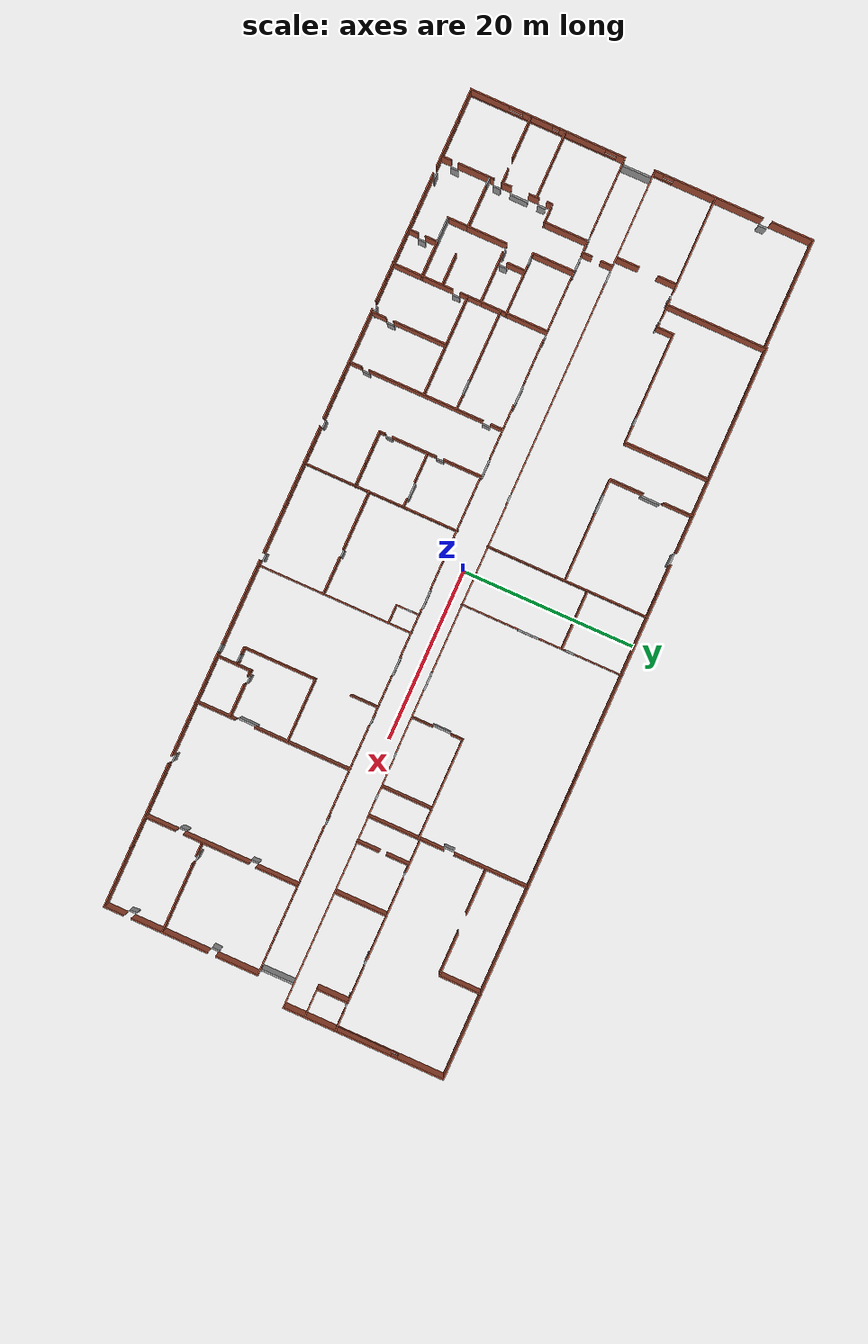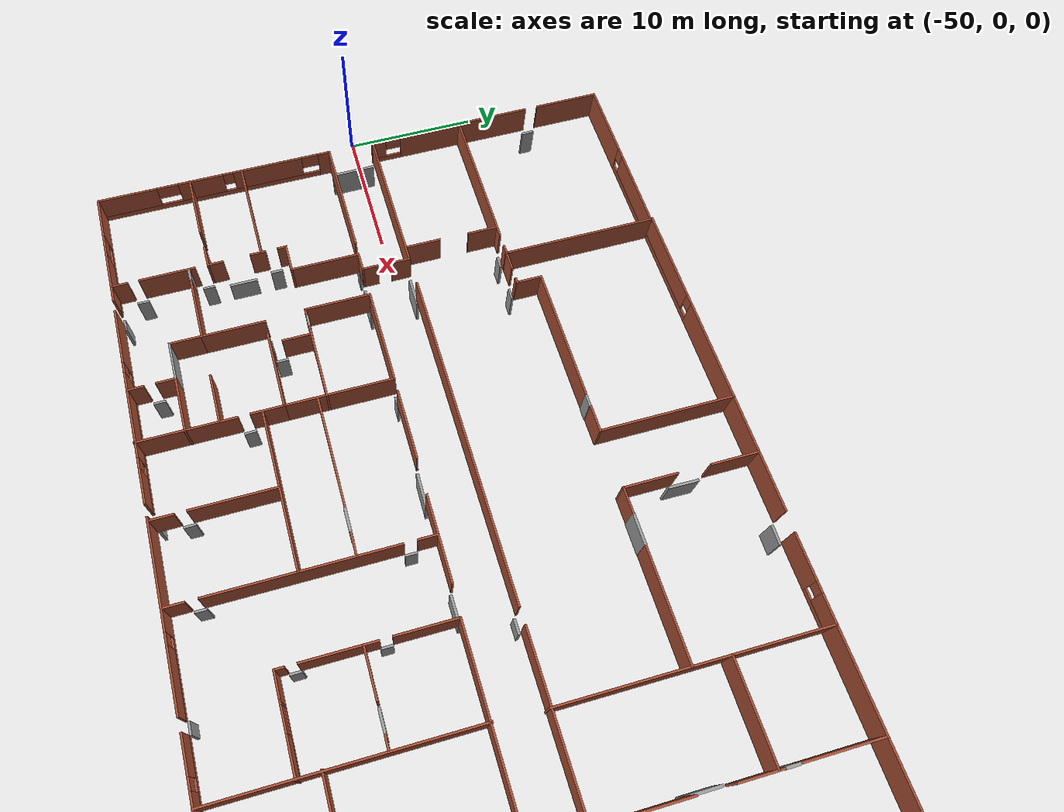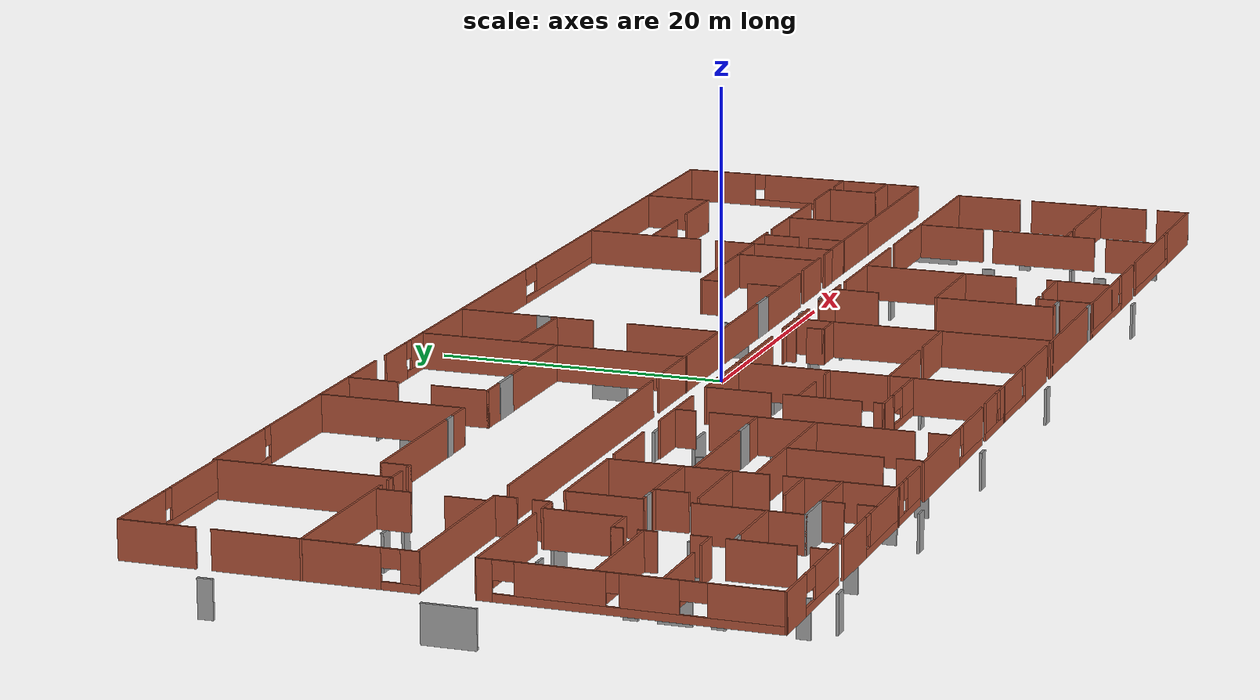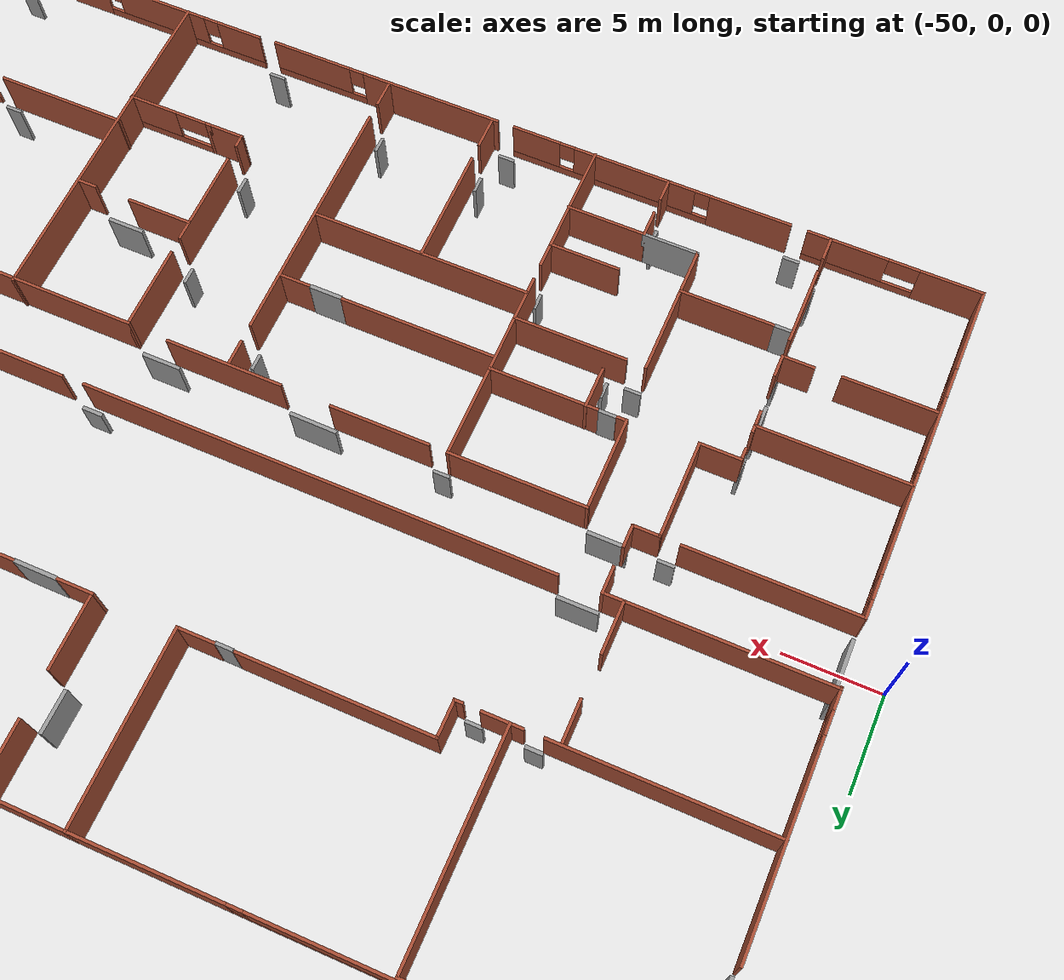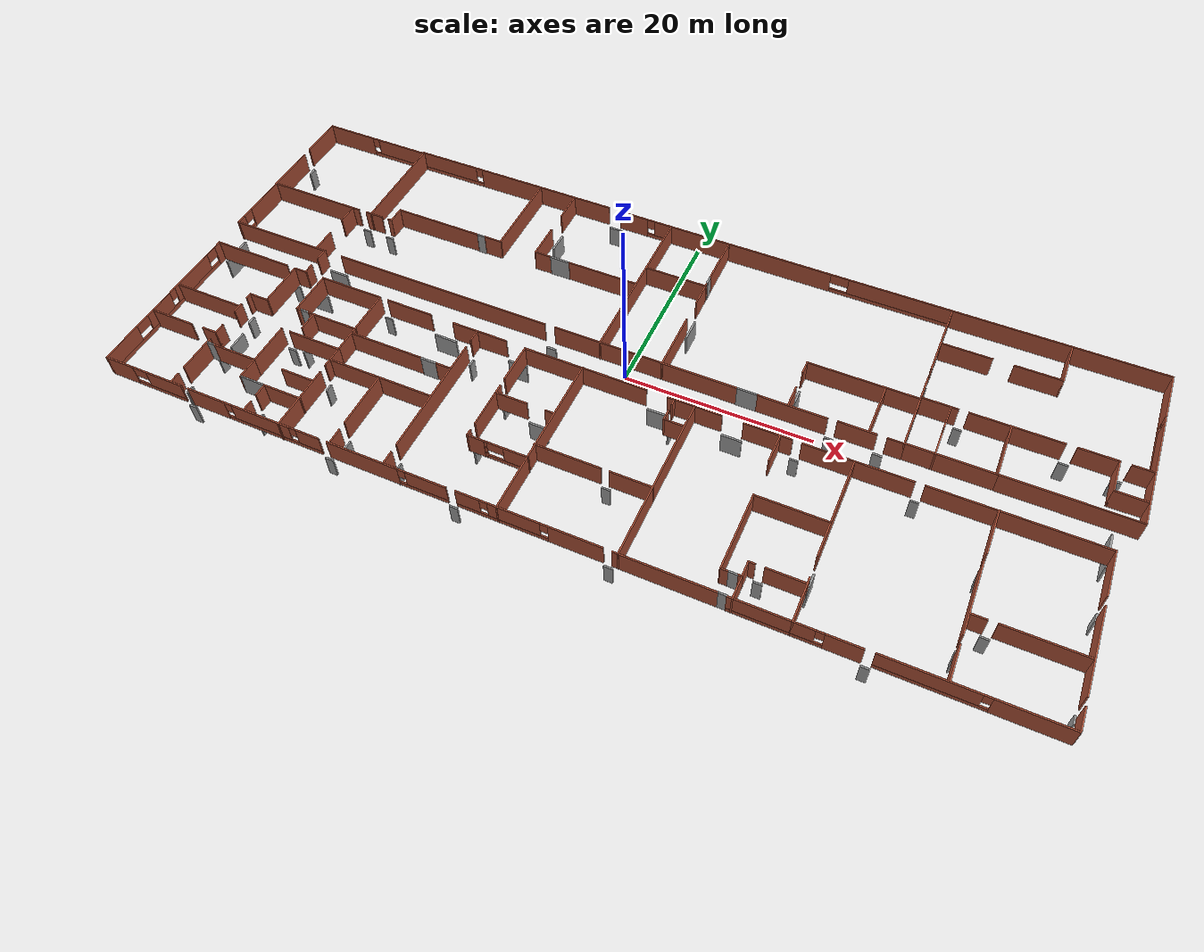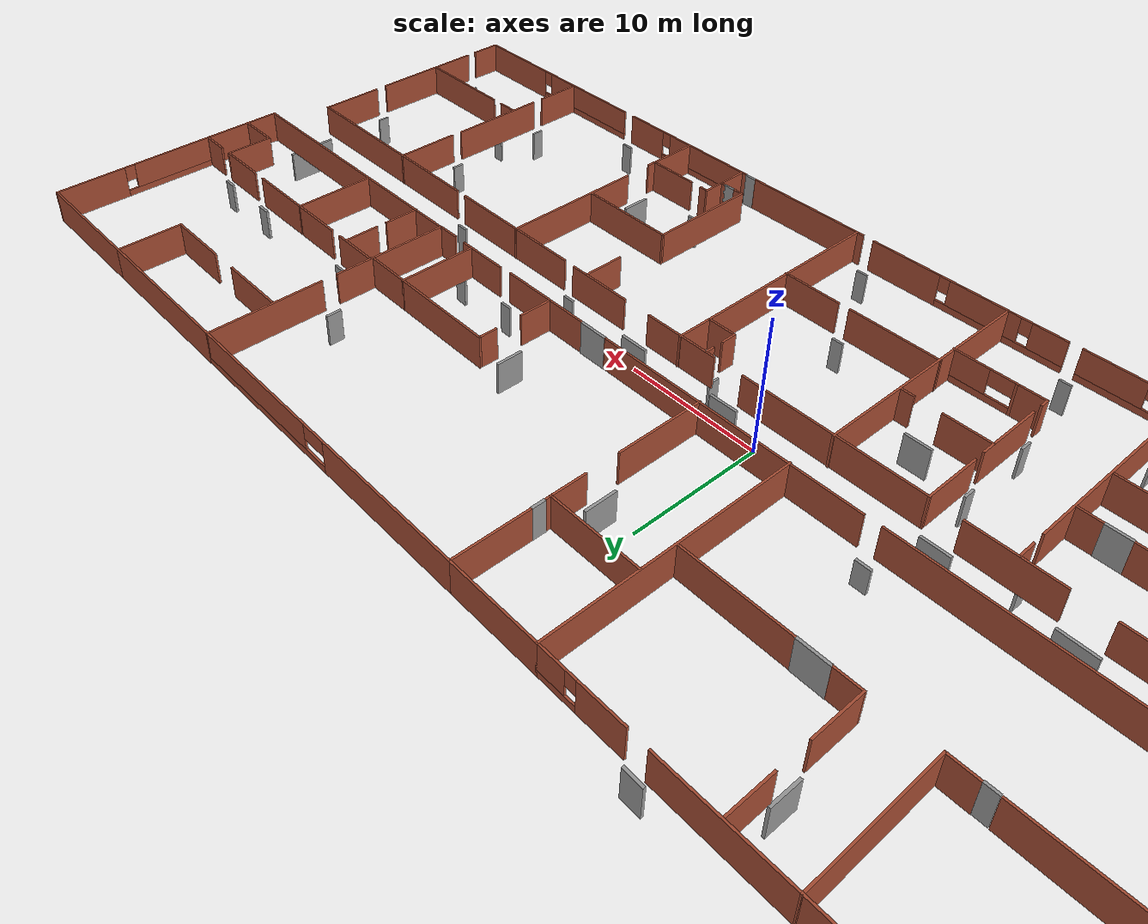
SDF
<sdf version="1.6">
  <model name="Bainer_Hall_FP">
    <pose frame="">1.25513 -0.156837 0 0 -0 0</pose>
    <link name="Door_10">
      <collision name="Door_10_Collision">
        <geometry>
          <box>
            <size>0.9 0.17 2.5</size>
          </box>
        </geometry>
        <pose frame="">0 0 1.25 0 -0 0</pose>
      </collision>
      <visual name="Door_10_Visual">
        <pose frame="">0 0 1.25 0 -0 0</pose>
        <geometry>
          <box>
            <size>0.9 0.17 2.5</size>
          </box>
        </geometry>
        <material>
          <script>
            <uri>file://media/materials/scripts/gazebo.material</uri>
            <name>Gazebo/Grey</name>
          </script>
        </material>
      </visual>
      <pose frame="">-34.5626 8.65196 -3 0 -0 0</pose>
    </link>
    <link name="Door_11">
      <collision name="Door_11_Collision">
        <geometry>
          <box>
            <size>0.9 0.17 2.5</size>
          </box>
        </geometry>
        <pose frame="">0 0 1.25 0 -0 0</pose>
      </collision>
      <visual name="Door_11_Visual">
        <pose frame="">0 0 1.25 0 -0 0</pose>
        <geometry>
          <box>
            <size>0.9 0.17 2.5</size>
          </box>
        </geometry>
        <material>
          <script>
            <uri>file://media/materials/scripts/gazebo.material</uri>
            <name>Gazebo/Grey</name>
          </script>
        </material>
      </visual>
      <pose frame="">-23.3342 10.4772 0 0 -0 0</pose>
    </link>
    <link name="Door_12">
      <collision name="Door_12_Collision">
        <geometry>
          <box>
            <size>2.165 0.2 2.5</size>
          </box>
        </geometry>
        <pose frame="">0 0 1.25 0 -0 0</pose>
      </collision>
      <visual name="Door_12_Visual">
        <pose frame="">0 0 1.25 0 -0 0</pose>
        <geometry>
          <box>
            <size>2.165 0.2 2.5</size>
          </box>
        </geometry>
        <material>
          <script>
            <uri>file://media/materials/scripts/gazebo.material</uri>
            <name>Gazebo/Grey</name>
          </script>
        </material>
      </visual>
      <pose frame="">-36.6968 1.50114 -3 0 -0 0</pose>
    </link>
    <link name="Door_14">
      <collision name="Door_14_Collision">
        <geometry>
          <box>
            <size>1.11106 0.2 2</size>
          </box>
        </geometry>
        <pose frame="">0 0 1 0 -0 0</pose>
      </collision>
      <visual name="Door_14_Visual">
        <pose frame="">0 0 1 0 -0 0</pose>
        <geometry>
          <box>
            <size>1.11106 0.2 2</size>
          </box>
        </geometry>
        <material>
          <script>
            <uri>file://media/materials/scripts/gazebo.material</uri>
            <name>Gazebo/Grey</name>
          </script>
        </material>
      </visual>
      <pose frame="">-10.4248 1.46984 -3 0 -0 0</pose>
    </link>
    <link name="Door_15">
      <collision name="Door_15_Collision">
        <geometry>
          <box>
            <size>2.143 0.2 2.5</size>
          </box>
        </geometry>
        <pose frame="">0 0 1.25 0 -0 0</pose>
      </collision>
      <visual name="Door_15_Visual">
        <pose frame="">0 0 1.25 0 -0 0</pose>
        <geometry>
          <box>
            <size>2.143 0.2 2.5</size>
          </box>
        </geometry>
        <material>
          <script>
            <uri>file://media/materials/scripts/gazebo.material</uri>
            <name>Gazebo/Grey</name>
          </script>
        </material>
      </visual>
      <pose frame="">11.2185 1.52839 0 0 -0 0</pose>
    </link>
    <link name="Door_16">
      <collision name="Door_16_Collision">
        <geometry>
          <box>
            <size>1.464 0.2 2.5</size>
          </box>
        </geometry>
        <pose frame="">0 0 1.25 0 -0 0</pose>
      </collision>
      <visual name="Door_16_Visual">
        <pose frame="">0 0 1.25 0 -0 0</pose>
        <geometry>
          <box>
            <size>1.464 0.2 2.5</size>
          </box>
        </geometry>
        <material>
          <script>
            <uri>file://media/materials/scripts/gazebo.material</uri>
            <name>Gazebo/Grey</name>
          </script>
        </material>
      </visual>
      <pose frame="">-11.5568 20.3759 -3 0 -0 3.12319</pose>
    </link>
    <link name="Door_17">
      <collision name="Door_17_Collision">
        <geometry>
          <box>
            <size>2.225 0.2 2.5</size>
          </box>
        </geometry>
        <pose frame="">0 0 1.25 0 -0 0</pose>
      </collision>
      <visual name="Door_17_Visual">
        <pose frame="">0 0 1.25 0 -0 0</pose>
        <geometry>
          <box>
            <size>2.225 0.2 2.5</size>
          </box>
        </geometry>
        <material>
          <script>
            <uri>file://media/materials/scripts/gazebo.material</uri>
            <name>Gazebo/Grey</name>
          </script>
        </material>
      </visual>
      <pose frame="">-13.7307 10.6137 0 0 -0 0</pose>
    </link>
    <link name="Door_19">
      <collision name="Door_19_Collision">
        <geometry>
          <box>
            <size>2.29098 0.2 2.5</size>
          </box>
        </geometry>
        <pose frame="">0 0 1.25 0 -0 0</pose>
      </collision>
      <visual name="Door_19_Visual">
        <pose frame="">0 0 1.25 0 -0 0</pose>
        <geometry>
          <box>
            <size>2.29098 0.2 2.5</size>
          </box>
        </geometry>
        <material>
          <script>
            <uri>file://media/materials/scripts/gazebo.material</uri>
            <name>Gazebo/Grey</name>
          </script>
        </material>
      </visual>
      <pose frame="">-16.6651 15.6807 -3 0 0 -1.58178</pose>
    </link>
    <link name="Door_20">
      <collision name="Door_20_Collision">
        <geometry>
          <box>
            <size>2.518 0.2 2.5</size>
          </box>
        </geometry>
        <pose frame="">0 0 1.25 0 -0 0</pose>
      </collision>
      <visual name="Door_20_Visual">
        <pose frame="">0 0 1.25 0 -0 0</pose>
        <geometry>
          <box>
            <size>2.518 0.2 2.5</size>
          </box>
        </geometry>
        <material>
          <script>
            <uri>file://media/materials/scripts/gazebo.material</uri>
            <name>Gazebo/Grey</name>
          </script>
        </material>
      </visual>
      <pose frame="">2.14668 9.40743 -3 0 -0 1.57339</pose>
    </link>
    <link name="Door_21">
      <collision name="Door_21_Collision">
        <geometry>
          <box>
            <size>1.007 0.2 2.5</size>
          </box>
        </geometry>
        <pose frame="">0 0 1.25 0 -0 0</pose>
      </collision>
      <visual name="Door_21_Visual">
        <pose frame="">0 0 1.25 0 -0 0</pose>
        <geometry>
          <box>
            <size>1.007 0.2 2.5</size>
          </box>
        </geometry>
        <material>
          <script>
            <uri>file://media/materials/scripts/gazebo.material</uri>
            <name>Gazebo/Grey</name>
          </script>
        </material>
      </visual>
      <pose frame="">2.14334 14.2049 0 0 0 -1.5708</pose>
    </link>
    <link name="Door_22">
      <collision name="Door_22_Collision">
        <geometry>
          <box>
            <size>1.17263 0.2 2.5</size>
          </box>
        </geometry>
        <pose frame="">0 0 1.25 0 -0 0</pose>
      </collision>
      <visual name="Door_22_Visual">
        <pose frame="">0 0 1.25 0 -0 0</pose>
        <geometry>
          <box>
            <size>1.17263 0.2 2.5</size>
          </box>
        </geometry>
        <material>
          <script>
            <uri>file://media/materials/scripts/gazebo.material</uri>
            <name>Gazebo/Grey</name>
          </script>
        </material>
      </visual>
      <pose frame="">26.9821 11.0502 -3 0 0 -1.55803</pose>
    </link>
    <link name="Door_23">
      <collision name="Door_23_Collision">
        <geometry>
          <box>
            <size>1.01 0.2 2.5</size>
          </box>
        </geometry>
        <pose frame="">0 0 1.25 0 -0 0</pose>
      </collision>
      <visual name="Door_23_Visual">
        <pose frame="">0 0 1.25 0 -0 0</pose>
        <geometry>
          <box>
            <size>1.01 0.2 2.5</size>
          </box>
        </geometry>
        <material>
          <script>
            <uri>file://media/materials/scripts/gazebo.material</uri>
            <name>Gazebo/Grey</name>
          </script>
        </material>
      </visual>
      <pose frame="">24.8391 1.55098 -3 0 -0 3.10452</pose>
    </link>
    <link name="Door_24">
      <collision name="Door_24_Collision">
        <geometry>
          <box>
            <size>0.9 0.17 2.5</size>
          </box>
        </geometry>
        <pose frame="">0 0 1.25 0 -0 0</pose>
      </collision>
      <visual name="Door_24_Visual">
        <pose frame="">0 0 1.25 0 -0 0</pose>
        <geometry>
          <box>
            <size>0.9 0.17 2.5</size>
          </box>
        </geometry>
        <material>
          <script>
            <uri>file://media/materials/scripts/gazebo.material</uri>
            <name>Gazebo/Grey</name>
          </script>
        </material>
      </visual>
      <pose frame="">19.9109 1.51909 -3 0 -0 0</pose>
    </link>
    <link name="Door_25">
      <collision name="Door_25_Collision">
        <geometry>
          <box>
            <size>2.087 0.2 2.5</size>
          </box>
        </geometry>
        <pose frame="">0 0 1.25 0 -0 0</pose>
      </collision>
      <visual name="Door_25_Visual">
        <pose frame="">0 0 1.25 0 -0 0</pose>
        <geometry>
          <box>
            <size>2.087 0.2 2.5</size>
          </box>
        </geometry>
        <material>
          <script>
            <uri>file://media/materials/scripts/gazebo.material</uri>
            <name>Gazebo/Grey</name>
          </script>
        </material>
      </visual>
      <pose frame="">15.4161 5.0222 -3 0 0 -1.5708</pose>
    </link>
    <link name="Door_26">
      <collision name="Door_26_Collision">
        <geometry>
          <box>
            <size>1.035 0.2 2.5</size>
          </box>
        </geometry>
        <pose frame="">0 0 1.25 0 -0 0</pose>
      </collision>
      <visual name="Door_26_Visual">
        <pose frame="">0 0 1.25 0 -0 0</pose>
        <geometry>
          <box>
            <size>1.035 0.2 2.5</size>
          </box>
        </geometry>
        <material>
          <script>
            <uri>file://media/materials/scripts/gazebo.material</uri>
            <name>Gazebo/Grey</name>
          </script>
        </material>
      </visual>
      <pose frame="">41.537 7.70908 -3 0 -0 0</pose>
    </link>
    <link name="Door_27">
      <collision name="Door_27_Collision">
        <geometry>
          <box>
            <size>0.989792 0.2 2.5</size>
          </box>
        </geometry>
        <pose frame="">0 0 1.25 0 -0 0</pose>
      </collision>
      <visual name="Door_27_Visual">
        <pose frame="">0 0 1.25 0 -0 0</pose>
        <geometry>
          <box>
            <size>0.989792 0.2 2.5</size>
          </box>
        </geometry>
        <material>
          <script>
            <uri>file://media/materials/scripts/gazebo.material</uri>
            <name>Gazebo/Grey</name>
          </script>
        </material>
      </visual>
      <pose frame="">46.5429 7.70908 -3 0 -0 0</pose>
    </link>
    <link name="Door_28">
      <collision name="Door_28_Collision">
        <geometry>
          <box>
            <size>0.9 0.17 2.5</size>
          </box>
        </geometry>
        <pose frame="">0 0 1.25 0 -0 0</pose>
      </collision>
      <visual name="Door_28_Visual">
        <pose frame="">0 0 1.25 0 -0 0</pose>
        <geometry>
          <box>
            <size>0.9 0.17 2.5</size>
          </box>
        </geometry>
        <material>
          <script>
            <uri>file://media/materials/scripts/gazebo.material</uri>
            <name>Gazebo/Grey</name>
          </script>
        </material>
      </visual>
      <pose frame="">31.1816 7.72893 -3 0 -0 0</pose>
    </link>
    <link name="Door_29">
      <collision name="Door_29_Collision">
        <geometry>
          <box>
            <size>0.9 0.17 2.5</size>
          </box>
        </geometry>
        <pose frame="">0 0 1.25 0 -0 0</pose>
      </collision>
      <visual name="Door_29_Visual">
        <pose frame="">0 0 1.25 0 -0 0</pose>
        <geometry>
          <box>
            <size>0.9 0.17 2.5</size>
          </box>
        </geometry>
        <material>
          <script>
            <uri>file://media/materials/scripts/gazebo.material</uri>
            <name>Gazebo/Grey</name>
          </script>
        </material>
      </visual>
      <pose frame="">-39.7621 -2.07664 -3 0 0 -3.14159</pose>
    </link>
    <link name="Door_30">
      <collision name="Door_30_Collision">
        <geometry>
          <box>
            <size>2.11069 0.2 2.5</size>
          </box>
        </geometry>
        <pose frame="">0 0 1.25 0 -0 0</pose>
      </collision>
      <visual name="Door_30_Visual">
        <pose frame="">0 0 1.25 0 -0 0</pose>
        <geometry>
          <box>
            <size>2.11069 0.2 2.5</size>
          </box>
        </geometry>
        <material>
          <script>
            <uri>file://media/materials/scripts/gazebo.material</uri>
            <name>Gazebo/Grey</name>
          </script>
        </material>
      </visual>
      <pose frame="">-36.7462 -2.09134 -3 0 -0 0</pose>
    </link>
    <link name="Door_31">
      <collision name="Door_31_Collision">
        <geometry>
          <box>
            <size>0.9 0.17 2.5</size>
          </box>
        </geometry>
        <pose frame="">0 0 1.25 0 -0 0</pose>
      </collision>
      <visual name="Door_31_Visual">
        <pose frame="">0 0 1.25 0 -0 0</pose>
        <geometry>
          <box>
            <size>0.9 0.17 2.5</size>
          </box>
        </geometry>
        <material>
          <script>
            <uri>file://media/materials/scripts/gazebo.material</uri>
            <name>Gazebo/Grey</name>
          </script>
        </material>
      </visual>
      <pose frame="">-34.6539 -6.91196 0 0 -0 0</pose>
    </link>
    <link name="Door_32">
      <collision name="Door_32_Collision">
        <geometry>
          <box>
            <size>0.9 0.17 2.5</size>
          </box>
        </geometry>
        <pose frame="">0 0 1.25 0 -0 0</pose>
      </collision>
      <visual name="Door_32_Visual">
        <pose frame="">0 0 1.25 0 -0 0</pose>
        <geometry>
          <box>
            <size>0.9 0.17 2.5</size>
          </box>
        </geometry>
        <material>
          <script>
            <uri>file://media/materials/scripts/gazebo.material</uri>
            <name>Gazebo/Grey</name>
          </script>
        </material>
      </visual>
      <pose frame="">-28.0011 -2.09981 -3 0 -0 0</pose>
    </link>
    <link name="Door_33">
      <collision name="Door_33_Collision">
        <geometry>
          <box>
            <size>2.592 0.2 2.5</size>
          </box>
        </geometry>
        <pose frame="">0 0 1.25 0 -0 0</pose>
      </collision>
      <visual name="Door_33_Visual">
        <pose frame="">0 0 1.25 0 -0 0</pose>
        <geometry>
          <box>
            <size>2.592 0.2 2.5</size>
          </box>
        </geometry>
        <material>
          <script>
            <uri>file://media/materials/scripts/gazebo.material</uri>
            <name>Gazebo/Grey</name>
          </script>
        </material>
      </visual>
      <pose frame="">-21.0189 -2.12561 -3 0 -0 3.12756</pose>
    </link>
    <link name="Door_34">
      <collision name="Door_34_Collision">
        <geometry>
          <box>
            <size>2.11 0.2 2.5</size>
          </box>
        </geometry>
        <pose frame="">0 0 1.25 0 -0 0</pose>
      </collision>
      <visual name="Door_34_Visual">
        <pose frame="">0 0 1.25 0 -0 0</pose>
        <geometry>
          <box>
            <size>2.11 0.2 2.5</size>
          </box>
        </geometry>
        <material>
          <script>
            <uri>file://media/materials/scripts/gazebo.material</uri>
            <name>Gazebo/Grey</name>
          </script>
        </material>
      </visual>
      <pose frame="">-12.4392 -2.19282 -3 0 0 -3.14115</pose>
    </link>
    <link name="Door_35">
      <collision name="Door_35_Collision">
        <geometry>
          <box>
            <size>2.157 0.2 2.5</size>
          </box>
        </geometry>
        <pose frame="">0 0 1.25 0 -0 0</pose>
      </collision>
      <visual name="Door_35_Visual">
        <pose frame="">0 0 1.25 0 -0 0</pose>
        <geometry>
          <box>
            <size>2.157 0.2 2.5</size>
          </box>
        </geometry>
        <material>
          <script>
            <uri>file://media/materials/scripts/gazebo.material</uri>
            <name>Gazebo/Grey</name>
          </script>
        </material>
      </visual>
      <pose frame="">3.22764 -2.26006 -3 0 0 -3.13357</pose>
    </link>
    <link name="Door_36">
      <collision name="Door_36_Collision">
        <geometry>
          <box>
            <size>2.157 0.2 2.5</size>
          </box>
        </geometry>
        <pose frame="">0 0 1.25 0 -0 0</pose>
      </collision>
      <visual name="Door_36_Visual">
        <pose frame="">0 0 1.25 0 -0 0</pose>
        <geometry>
          <box>
            <size>2.157 0.2 2.5</size>
          </box>
        </geometry>
        <material>
          <script>
            <uri>file://media/materials/scripts/gazebo.material</uri>
            <name>Gazebo/Grey</name>
          </script>
        </material>
      </visual>
      <pose frame="">11.1742 -2.26006 -3 0 -0 0</pose>
    </link>
    <link name="Door_37">
      <collision name="Door_37_Collision">
        <geometry>
          <box>
            <size>0.9 0.17 2.5</size>
          </box>
        </geometry>
        <pose frame="">0 0 1.25 0 -0 0</pose>
      </collision>
      <visual name="Door_37_Visual">
        <pose frame="">0 0 1.25 0 -0 0</pose>
        <geometry>
          <box>
            <size>0.9 0.17 2.5</size>
          </box>
        </geometry>
        <material>
          <script>
            <uri>file://media/materials/scripts/gazebo.material</uri>
            <name>Gazebo/Grey</name>
          </script>
        </material>
      </visual>
      <pose frame="">17.6392 -2.30496 -3 0 -0 0</pose>
    </link>
    <link name="Door_38">
      <collision name="Door_38_Collision">
        <geometry>
          <box>
            <size>0.9 0.17 2.5</size>
          </box>
        </geometry>
        <pose frame="">0 0 1.25 0 -0 0</pose>
      </collision>
      <visual name="Door_38_Visual">
        <pose frame="">0 0 1.25 0 -0 0</pose>
        <geometry>
          <box>
            <size>0.9 0.17 2.5</size>
          </box>
        </geometry>
        <material>
          <script>
            <uri>file://media/materials/scripts/gazebo.material</uri>
            <name>Gazebo/Grey</name>
          </script>
        </material>
      </visual>
      <pose frame="">29.5592 -2.30521 -3 0 0 -3.13072</pose>
    </link>
    <link name="Door_39">
      <collision name="Door_39_Collision">
        <geometry>
          <box>
            <size>0.9 0.17 2.5</size>
          </box>
        </geometry>
        <pose frame="">0 0 1.25 0 -0 0</pose>
      </collision>
      <visual name="Door_39_Visual">
        <pose frame="">0 0 1.25 0 -0 0</pose>
        <geometry>
          <box>
            <size>0.9 0.17 2.5</size>
          </box>
        </geometry>
        <material>
          <script>
            <uri>file://media/materials/scripts/gazebo.material</uri>
            <name>Gazebo/Grey</name>
          </script>
        </material>
      </visual>
      <pose frame="">47.1899 -7.6622 -3 0 -0 1.55378</pose>
    </link>
    <link name="Door_40">
      <collision name="Door_40_Collision">
        <geometry>
          <box>
            <size>0.9 0.17 2</size>
          </box>
        </geometry>
        <pose frame="">0 0 1 0 -0 0</pose>
      </collision>
      <visual name="Door_40_Visual">
        <pose frame="">0 0 1 0 -0 0</pose>
        <geometry>
          <box>
            <size>0.9 0.17 2</size>
          </box>
        </geometry>
        <material>
          <script>
            <uri>file://media/materials/scripts/gazebo.material</uri>
            <name>Gazebo/Grey</name>
          </script>
        </material>
      </visual>
      <pose frame="">47.2284 -17.5715 -3 0 -0 1.63085</pose>
    </link>
    <link name="Door_42">
      <collision name="Door_42_Collision">
        <geometry>
          <box>
            <size>0.9 0.17 2.5</size>
          </box>
        </geometry>
        <pose frame="">0 0 1.25 0 -0 0</pose>
      </collision>
      <visual name="Door_42_Visual">
        <pose frame="">0 0 1.25 0 -0 0</pose>
        <geometry>
          <box>
            <size>0.9 0.17 2.5</size>
          </box>
        </geometry>
        <material>
          <script>
            <uri>file://media/materials/scripts/gazebo.material</uri>
            <name>Gazebo/Grey</name>
          </script>
        </material>
      </visual>
      <pose frame="">30.1038 -20.3171 -3 0 -0 0</pose>
    </link>
    <link name="Door_43">
      <collision name="Door_43_Collision">
        <geometry>
          <box>
            <size>0.9 0.17 2.5</size>
          </box>
        </geometry>
        <pose frame="">0 0 1.25 0 -0 0</pose>
      </collision>
      <visual name="Door_43_Visual">
        <pose frame="">0 0 1.25 0 -0 0</pose>
        <geometry>
          <box>
            <size>0.9 0.17 2.5</size>
          </box>
        </geometry>
        <material>
          <script>
            <uri>file://media/materials/scripts/gazebo.material</uri>
            <name>Gazebo/Grey</name>
          </script>
        </material>
      </visual>
      <pose frame="">17.011 -20.2734 0 0 -0 0</pose>
    </link>
    <link name="Door_44">
      <collision name="Door_44_Collision">
        <geometry>
          <box>
            <size>2.20957 0.2 2.5</size>
          </box>
        </geometry>
        <pose frame="">0 0 1.25 0 -0 0</pose>
      </collision>
      <visual name="Door_44_Visual">
        <pose frame="">0 0 1.25 0 -0 0</pose>
        <geometry>
          <box>
            <size>2.20957 0.2 2.5</size>
          </box>
        </geometry>
        <material>
          <script>
            <uri>file://media/materials/scripts/gazebo.material</uri>
            <name>Gazebo/Grey</name>
          </script>
        </material>
      </visual>
      <pose frame="">23.3396 -14.5504 -3 0 0 -1.58102</pose>
    </link>
    <link name="Door_45">
      <collision name="Door_45_Collision">
        <geometry>
          <box>
            <size>0.9 0.17 2.5</size>
          </box>
        </geometry>
        <pose frame="">0 0 1.25 0 -0 0</pose>
      </collision>
      <visual name="Door_45_Visual">
        <pose frame="">0 0 1.25 0 -0 0</pose>
        <geometry>
          <box>
            <size>0.9 0.17 2.5</size>
          </box>
        </geometry>
        <material>
          <script>
            <uri>file://media/materials/scripts/gazebo.material</uri>
            <name>Gazebo/Grey</name>
          </script>
        </material>
      </visual>
      <pose frame="">17.1411 -17.9894 0 0 0 -3.1354</pose>
    </link>
    <link name="Door_46">
      <collision name="Door_46_Collision">
        <geometry>
          <box>
            <size>0.9 0.17 2.5</size>
          </box>
        </geometry>
        <pose frame="">0 0 1.25 0 -0 0</pose>
      </collision>
      <visual name="Door_46_Visual">
        <pose frame="">0 0 1.25 0 -0 0</pose>
        <geometry>
          <box>
            <size>0.9 0.17 2.5</size>
          </box>
        </geometry>
        <material>
          <script>
            <uri>file://media/materials/scripts/gazebo.material</uri>
            <name>Gazebo/Grey</name>
          </script>
        </material>
      </visual>
      <pose frame="">19.031 -16.3929 -3 0 -0 0</pose>
    </link>
    <link name="Door_47">
      <collision name="Door_47_Collision">
        <geometry>
          <box>
            <size>0.9 0.17 2.5</size>
          </box>
        </geometry>
        <pose frame="">0 0 1.25 0 -0 0</pose>
      </collision>
      <visual name="Door_47_Visual">
        <pose frame="">0 0 1.25 0 -0 0</pose>
        <geometry>
          <box>
            <size>0.9 0.17 2.5</size>
          </box>
        </geometry>
        <material>
          <script>
            <uri>file://media/materials/scripts/gazebo.material</uri>
            <name>Gazebo/Grey</name>
          </script>
        </material>
      </visual>
      <pose frame="">6.17549 -20.287 -3 0 -0 0</pose>
    </link>
    <link name="Door_48">
      <collision name="Door_48_Collision">
        <geometry>
          <box>
            <size>0.9 0.17 2.5</size>
          </box>
        </geometry>
        <pose frame="">0 0 1.25 0 -0 0</pose>
      </collision>
      <visual name="Door_48_Visual">
        <pose frame="">0 0 1.25 0 -0 0</pose>
        <geometry>
          <box>
            <size>0.9 0.17 2.5</size>
          </box>
        </geometry>
        <material>
          <script>
            <uri>file://media/materials/scripts/gazebo.material</uri>
            <name>Gazebo/Grey</name>
          </script>
        </material>
      </visual>
      <pose frame="">-9.75215 -20.292 -3 0 -0 0</pose>
    </link>
    <link name="Door_49">
      <collision name="Door_49_Collision">
        <geometry>
          <box>
            <size>0.94 0.2 2.5</size>
          </box>
        </geometry>
        <pose frame="">0 0 1.25 0 -0 0</pose>
      </collision>
      <visual name="Door_49_Visual">
        <pose frame="">0 0 1.25 0 -0 0</pose>
        <geometry>
          <box>
            <size>0.94 0.2 2.5</size>
          </box>
        </geometry>
        <material>
          <script>
            <uri>file://media/materials/scripts/gazebo.material</uri>
            <name>Gazebo/Grey</name>
          </script>
        </material>
      </visual>
      <pose frame="">-41.3093 -8.28276 -3 0 -0 1.57919</pose>
    </link>
    <link name="Door_50">
      <collision name="Door_50_Collision">
        <geometry>
          <box>
            <size>2.14227 0.2 2</size>
          </box>
        </geometry>
        <pose frame="">0 0 1 0 -0 0</pose>
      </collision>
      <visual name="Door_50_Visual">
        <pose frame="">0 0 1 0 -0 0</pose>
        <geometry>
          <box>
            <size>2.14227 0.2 2</size>
          </box>
        </geometry>
        <material>
          <script>
            <uri>file://media/materials/scripts/gazebo.material</uri>
            <name>Gazebo/Grey</name>
          </script>
        </material>
      </visual>
      <pose frame="">-41.3097 -10.9944 -3 0 -0 1.5708</pose>
    </link>
    <link name="Door_51">
      <collision name="Door_51_Collision">
        <geometry>
          <box>
            <size>0.9 0.17 2.5</size>
          </box>
        </geometry>
        <pose frame="">0 0 1.25 0 -0 0</pose>
      </collision>
      <visual name="Door_51_Visual">
        <pose frame="">0 0 1.25 0 -0 0</pose>
        <geometry>
          <box>
            <size>0.9 0.17 2.5</size>
          </box>
        </geometry>
        <material>
          <script>
            <uri>file://media/materials/scripts/gazebo.material</uri>
            <name>Gazebo/Grey</name>
          </script>
        </material>
      </visual>
      <pose frame="">-41.2641 -13.6308 -3 0 0 -1.57632</pose>
    </link>
    <link name="Door_52">
      <collision name="Door_52_Collision">
        <geometry>
          <box>
            <size>0.9 0.17 2.5</size>
          </box>
        </geometry>
        <pose frame="">0 0 1.25 0 -0 0</pose>
      </collision>
      <visual name="Door_52_Visual">
        <pose frame="">0 0 1.25 0 -0 0</pose>
        <geometry>
          <box>
            <size>0.9 0.17 2.5</size>
          </box>
        </geometry>
        <material>
          <script>
            <uri>file://media/materials/scripts/gazebo.material</uri>
            <name>Gazebo/Grey</name>
          </script>
        </material>
      </visual>
      <pose frame="">-41.2637 -18.7055 -3 0 -0 1.5708</pose>
    </link>
    <link name="Door_53">
      <collision name="Door_53_Collision">
        <geometry>
          <box>
            <size>0.9 0.17 2.5</size>
          </box>
        </geometry>
        <pose frame="">0 0 1.25 0 -0 0</pose>
      </collision>
      <visual name="Door_53_Visual">
        <pose frame="">0 0 1.25 0 -0 0</pose>
        <geometry>
          <box>
            <size>0.9 0.17 2.5</size>
          </box>
        </geometry>
        <material>
          <script>
            <uri>file://media/materials/scripts/gazebo.material</uri>
            <name>Gazebo/Grey</name>
          </script>
        </material>
      </visual>
      <pose frame="">-40.7662 -14.5556 0 0 -0 0</pose>
    </link>
    <link name="Door_54">
      <collision name="Door_54_Collision">
        <geometry>
          <box>
            <size>0.9 0.17 2.5</size>
          </box>
        </geometry>
        <pose frame="">0 0 1.25 0 -0 0</pose>
      </collision>
      <visual name="Door_54_Visual">
        <pose frame="">0 0 1.25 0 -0 0</pose>
        <geometry>
          <box>
            <size>0.9 0.17 2.5</size>
          </box>
        </geometry>
        <material>
          <script>
            <uri>file://media/materials/scripts/gazebo.material</uri>
            <name>Gazebo/Grey</name>
          </script>
        </material>
      </visual>
      <pose frame="">-32.5666 -18.7651 -3 0 0 -1.5708</pose>
    </link>
    <link name="Door_56">
      <collision name="Door_56_Collision">
        <geometry>
          <box>
            <size>0.9 0.17 2.5</size>
          </box>
        </geometry>
        <pose frame="">0 0 1.25 0 -0 0</pose>
      </collision>
      <visual name="Door_56_Visual">
        <pose frame="">0 0 1.25 0 -0 0</pose>
        <geometry>
          <box>
            <size>0.9 0.17 2.5</size>
          </box>
        </geometry>
        <material>
          <script>
            <uri>file://media/materials/scripts/gazebo.material</uri>
            <name>Gazebo/Grey</name>
          </script>
        </material>
      </visual>
      <pose frame="">-34.8989 -9.9638 -3 0 -0 0</pose>
    </link>
    <link name="Door_57">
      <collision name="Door_57_Collision">
        <geometry>
          <box>
            <size>0.9 0.17 2.5</size>
          </box>
        </geometry>
        <pose frame="">0 0 1.25 0 -0 0</pose>
      </collision>
      <visual name="Door_57_Visual">
        <pose frame="">0 0 1.25 0 -0 0</pose>
        <geometry>
          <box>
            <size>0.9 0.17 2.5</size>
          </box>
        </geometry>
        <material>
          <script>
            <uri>file://media/materials/scripts/gazebo.material</uri>
            <name>Gazebo/Grey</name>
          </script>
        </material>
      </visual>
      <pose frame="">-33.5499 -9.44231 -3 0 -0 1.5708</pose>
    </link>
    <link name="Door_59">
      <collision name="Door_59_Collision">
        <geometry>
          <box>
            <size>0.9 0.17 2.5</size>
          </box>
        </geometry>
        <pose frame="">0 0 1.25 0 -0 0</pose>
      </collision>
      <visual name="Door_59_Visual">
        <pose frame="">0 0 1.25 0 -0 0</pose>
        <geometry>
          <box>
            <size>0.9 0.17 2.5</size>
          </box>
        </geometry>
        <material>
          <script>
            <uri>file://media/materials/scripts/gazebo.material</uri>
            <name>Gazebo/Grey</name>
          </script>
        </material>
      </visual>
      <pose frame="">-39.6193 -20.3098 -3 0 -0 0</pose>
    </link>
    <link name="Door_6">
      <collision name="Door_6_Collision">
        <geometry>
          <box>
            <size>0.992 0.2 2.5</size>
          </box>
        </geometry>
        <pose frame="">0 0 1.25 0 -0 0</pose>
      </collision>
      <visual name="Door_6_Visual">
        <pose frame="">0 0 1.25 0 -0 0</pose>
        <geometry>
          <box>
            <size>0.992 0.2 2.5</size>
          </box>
        </geometry>
        <material>
          <script>
            <uri>file://media/materials/scripts/gazebo.material</uri>
            <name>Gazebo/Grey</name>
          </script>
        </material>
      </visual>
      <pose frame="">-49.1881 14.7778 -3 0 0 -1.55735</pose>
    </link>
    <link name="Door_60">
      <collision name="Door_60_Collision">
        <geometry>
          <box>
            <size>0.9 0.17 2.5</size>
          </box>
        </geometry>
        <pose frame="">0 0 1.25 0 -0 0</pose>
      </collision>
      <visual name="Door_60_Visual">
        <pose frame="">0 0 1.25 0 -0 0</pose>
        <geometry>
          <box>
            <size>0.9 0.17 2.5</size>
          </box>
        </geometry>
        <material>
          <script>
            <uri>file://media/materials/scripts/gazebo.material</uri>
            <name>Gazebo/Grey</name>
          </script>
        </material>
      </visual>
      <pose frame="">-28.5031 -12.8222 -3 0 -0 1.59264</pose>
    </link>
    <link name="Door_61">
      <collision name="Door_61_Collision">
        <geometry>
          <box>
            <size>0.9 0.17 2.5</size>
          </box>
        </geometry>
        <pose frame="">0 0 1.25 0 -0 0</pose>
      </collision>
      <visual name="Door_61_Visual">
        <pose frame="">0 0 1.25 0 -0 0</pose>
        <geometry>
          <box>
            <size>0.9 0.17 2.5</size>
          </box>
        </geometry>
        <material>
          <script>
            <uri>file://media/materials/scripts/gazebo.material</uri>
            <name>Gazebo/Grey</name>
          </script>
        </material>
      </visual>
      <pose frame="">-16.8508 -4.01792 -3 0 -0 1.57286</pose>
    </link>
    <link name="Door_62">
      <collision name="Door_62_Collision">
        <geometry>
          <box>
            <size>0.9 0.17 2.5</size>
          </box>
        </geometry>
        <pose frame="">0 0 1.25 0 -0 0</pose>
      </collision>
      <visual name="Door_62_Visual">
        <pose frame="">0 0 1.25 0 -0 0</pose>
        <geometry>
          <box>
            <size>0.9 0.17 2.5</size>
          </box>
        </geometry>
        <material>
          <script>
            <uri>file://media/materials/scripts/gazebo.material</uri>
            <name>Gazebo/Grey</name>
          </script>
        </material>
      </visual>
      <pose frame="">-16.8428 -18.4047 -3 0 -0 1.55866</pose>
    </link>
    <link name="Door_63">
      <collision name="Door_63_Collision">
        <geometry>
          <box>
            <size>1.71 0.2 2.5</size>
          </box>
        </geometry>
        <pose frame="">0 0 1.25 0 -0 0</pose>
      </collision>
      <visual name="Door_63_Visual">
        <pose frame="">0 0 1.25 0 -0 0</pose>
        <geometry>
          <box>
            <size>1.71 0.2 2.5</size>
          </box>
        </geometry>
        <material>
          <script>
            <uri>file://media/materials/scripts/gazebo.material</uri>
            <name>Gazebo/Grey</name>
          </script>
        </material>
      </visual>
      <pose frame="">-19.4005 -7.62221 0 0 -0 3.14079</pose>
    </link>
    <link name="Door_64">
      <collision name="Door_64_Collision">
        <geometry>
          <box>
            <size>0.9 0.17 2.5</size>
          </box>
        </geometry>
        <pose frame="">0 0 1.25 0 -0 0</pose>
      </collision>
      <visual name="Door_64_Visual">
        <pose frame="">0 0 1.25 0 -0 0</pose>
        <geometry>
          <box>
            <size>0.9 0.17 2.5</size>
          </box>
        </geometry>
        <material>
          <script>
            <uri>file://media/materials/scripts/gazebo.material</uri>
            <name>Gazebo/Grey</name>
          </script>
        </material>
      </visual>
      <pose frame="">-22.7643 -18.1446 -3 0 0 -1.56371</pose>
    </link>
    <link name="Door_66">
      <collision name="Door_66_Collision">
        <geometry>
          <box>
            <size>0.9 0.17 2.5</size>
          </box>
        </geometry>
        <pose frame="">0 0 1.25 0 -0 0</pose>
      </collision>
      <visual name="Door_66_Visual">
        <pose frame="">0 0 1.25 0 -0 0</pose>
        <geometry>
          <box>
            <size>0.9 0.17 2.5</size>
          </box>
        </geometry>
        <material>
          <script>
            <uri>file://media/materials/scripts/gazebo.material</uri>
            <name>Gazebo/Grey</name>
          </script>
        </material>
      </visual>
      <pose frame="">-23.4877 -20.2913 -3 0 -0 0</pose>
    </link>
    <link name="Door_67">
      <collision name="Door_67_Collision">
        <geometry>
          <box>
            <size>0.9 0.17 2.5</size>
          </box>
        </geometry>
        <pose frame="">0 0 1.25 0 -0 0</pose>
      </collision>
      <visual name="Door_67_Visual">
        <pose frame="">0 0 1.25 0 -0 0</pose>
        <geometry>
          <box>
            <size>0.9 0.17 2.5</size>
          </box>
        </geometry>
        <material>
          <script>
            <uri>file://media/materials/scripts/gazebo.material</uri>
            <name>Gazebo/Grey</name>
          </script>
        </material>
      </visual>
      <pose frame="">-11.3225 -7.13282 -3 0 0 -1.57029</pose>
    </link>
    <link name="Door_68">
      <collision name="Door_68_Collision">
        <geometry>
          <box>
            <size>0.9 0.17 2.5</size>
          </box>
        </geometry>
        <pose frame="">0 0 1.25 0 -0 0</pose>
      </collision>
      <visual name="Door_68_Visual">
        <pose frame="">0 0 1.25 0 -0 0</pose>
        <geometry>
          <box>
            <size>0.9 0.17 2.5</size>
          </box>
        </geometry>
        <material>
          <script>
            <uri>file://media/materials/scripts/gazebo.material</uri>
            <name>Gazebo/Grey</name>
          </script>
        </material>
      </visual>
      <pose frame="">-11.287 -13.1738 -3 0 0 -1.56906</pose>
    </link>
    <link name="Door_70">
      <collision name="Door_70_Collision">
        <geometry>
          <box>
            <size>2 0.2 2.5</size>
          </box>
        </geometry>
        <pose frame="">0 0 1.25 0 -0 0</pose>
      </collision>
      <visual name="Door_70_Visual">
        <pose frame="">0 0 1.25 0 -0 0</pose>
        <geometry>
          <box>
            <size>2 0.2 2.5</size>
          </box>
        </geometry>
        <material>
          <script>
            <uri>file://media/materials/scripts/gazebo.material</uri>
            <name>Gazebo/Grey</name>
          </script>
        </material>
      </visual>
      <pose frame="">-6.84024 -8.55412 -3 0 -0 0</pose>
    </link>
    <link name="Door_72">
      <collision name="Door_72_Collision">
        <geometry>
          <box>
            <size>0.9 0.17 2.5</size>
          </box>
        </geometry>
        <pose frame="">0 0 1.25 0 -0 0</pose>
      </collision>
      <visual name="Door_72_Visual">
        <pose frame="">0 0 1.25 0 -0 0</pose>
        <geometry>
          <box>
            <size>0.9 0.17 2.5</size>
          </box>
        </geometry>
        <material>
          <script>
            <uri>file://media/materials/scripts/gazebo.material</uri>
            <name>Gazebo/Grey</name>
          </script>
        </material>
      </visual>
      <pose frame="">2.42458 -12.6709 -3 0 -0 0</pose>
    </link>
    <link name="Door_73">
      <collision name="Door_73_Collision">
        <geometry>
          <box>
            <size>0.9 0.17 2.5</size>
          </box>
        </geometry>
        <pose frame="">0 0 1.25 0 -0 0</pose>
      </collision>
      <visual name="Door_73_Visual">
        <pose frame="">0 0 1.25 0 -0 0</pose>
        <geometry>
          <box>
            <size>0.9 0.17 2.5</size>
          </box>
        </geometry>
        <material>
          <script>
            <uri>file://media/materials/scripts/gazebo.material</uri>
            <name>Gazebo/Grey</name>
          </script>
        </material>
      </visual>
      <pose frame="">5.06769 -3.35498 -3 0 0 -1.56706</pose>
    </link>
    <link name="Door_74">
      <collision name="Door_74_Collision">
        <geometry>
          <box>
            <size>0.9 0.17 2.5</size>
          </box>
        </geometry>
        <pose frame="">0 0 1.25 0 -0 0</pose>
      </collision>
      <visual name="Door_74_Visual">
        <pose frame="">0 0 1.25 0 -0 0</pose>
        <geometry>
          <box>
            <size>0.9 0.17 2.5</size>
          </box>
        </geometry>
        <material>
          <script>
            <uri>file://media/materials/scripts/gazebo.material</uri>
            <name>Gazebo/Grey</name>
          </script>
        </material>
      </visual>
      <pose frame="">36.8135 -7.65435 -3 0 -0 1.56912</pose>
    </link>
    <link name="Door_75">
      <collision name="Door_75_Collision">
        <geometry>
          <box>
            <size>0.9 0.17 2.5</size>
          </box>
        </geometry>
        <pose frame="">0 0 1.25 0 -0 0</pose>
      </collision>
      <visual name="Door_75_Visual">
        <pose frame="">0 0 1.25 0 -0 0</pose>
        <geometry>
          <box>
            <size>0.9 0.17 2.5</size>
          </box>
        </geometry>
        <material>
          <script>
            <uri>file://media/materials/scripts/gazebo.material</uri>
            <name>Gazebo/Grey</name>
          </script>
        </material>
      </visual>
      <pose frame="">36.7536 -16.1655 -3 0 -0 1.57023</pose>
    </link>
    <link name="Door_77">
      <collision name="Door_77_Collision">
        <geometry>
          <box>
            <size>0.9 0.17 2.5</size>
          </box>
        </geometry>
        <pose frame="">0 0 1.25 0 -0 0</pose>
      </collision>
      <visual name="Door_77_Visual">
        <pose frame="">0 0 1.25 0 -0 0</pose>
        <geometry>
          <box>
            <size>0.9 0.17 2.5</size>
          </box>
        </geometry>
        <material>
          <script>
            <uri>file://media/materials/scripts/gazebo.material</uri>
            <name>Gazebo/Grey</name>
          </script>
        </material>
      </visual>
      <pose frame="">38.7507 -13.5455 -3 0 -0 0</pose>
    </link>
    <link name="Door_78">
      <collision name="Door_78_Collision">
        <geometry>
          <box>
            <size>3.44 0.2 2.5</size>
          </box>
        </geometry>
        <pose frame="">0 0 1.25 0 -0 0</pose>
      </collision>
      <visual name="Door_78_Visual">
        <pose frame="">0 0 1.25 0 -0 0</pose>
        <geometry>
          <box>
            <size>3.44 0.2 2.5</size>
          </box>
        </geometry>
        <material>
          <script>
            <uri>file://media/materials/scripts/gazebo.material</uri>
            <name>Gazebo/Grey</name>
          </script>
        </material>
      </visual>
      <pose frame="">-49.1641 -0.320163 -3 0 -0 1.57718</pose>
    </link>
    <link name="Door_79">
      <collision name="Door_79_Collision">
        <geometry>
          <box>
            <size>3.838 0.2 2.5</size>
          </box>
        </geometry>
        <pose frame="">0 0 1.25 0 -0 0</pose>
      </collision>
      <visual name="Door_79_Visual">
        <pose frame="">0 0 1.25 0 -0 0</pose>
        <geometry>
          <box>
            <size>3.838 0.2 2.5</size>
          </box>
        </geometry>
        <material>
          <script>
            <uri>file://media/materials/scripts/gazebo.material</uri>
            <name>Gazebo/Grey</name>
          </script>
        </material>
      </visual>
      <pose frame="">47.1524 -0.340719 -3 0 -0 1.57754</pose>
    </link>
    <link name="Door_9">
      <collision name="Door_9_Collision">
        <geometry>
          <box>
            <size>0.927 0.2 2.5</size>
          </box>
        </geometry>
        <pose frame="">0 0 1.25 0 -0 0</pose>
      </collision>
      <visual name="Door_9_Visual">
        <pose frame="">0 0 1.25 0 -0 0</pose>
        <geometry>
          <box>
            <size>0.927 0.2 2.5</size>
          </box>
        </geometry>
        <material>
          <script>
            <uri>file://media/materials/scripts/gazebo.material</uri>
            <name>Gazebo/Grey</name>
          </script>
        </material>
      </visual>
      <pose frame="">-37.5493 8.66307 -3 0 -0 0</pose>
    </link>
    <link name="Wall_139">
      <collision name="Wall_139_Collision">
        <geometry>
          <box>
            <size>5 0.15 2.5</size>
          </box>
        </geometry>
        <pose frame="">0 0 1.25 0 -0 0</pose>
      </collision>
      <visual name="Wall_139_Visual">
        <pose frame="">0 0 1.25 0 -0 0</pose>
        <geometry>
          <box>
            <size>5 0.15 2.5</size>
          </box>
        </geometry>
        <material>
          <script>
            <uri>file://media/materials/scripts/gazebo.material</uri>
            <name>Gazebo/Bricks</name>
          </script>
          <ambient>1 1 1 1</ambient>
        </material>
      </visual>
      <pose frame="">-49.1917 17.7539 0 0 0 -1.5708</pose>
    </link>
    <link name="Wall_141">
      <pose frame="">-49.1778 7.83841 0 0 0 -1.5708</pose>
      <visual name="Wall_141_Visual_0">
        <pose frame="">-1.18334 0 1.25 0 -0 0</pose>
        <geometry>
          <box>
            <size>10.5535 0.15 2.5</size>
          </box>
        </geometry>
        <material>
          <script>
            <uri>file://media/materials/scripts/gazebo.material</uri>
            <name>Gazebo/Bricks</name>
          </script>
          <ambient>1 1 1 1</ambient>
        </material>
      </visual>
      <collision name="Wall_141_Collision_0">
        <geometry>
          <box>
            <size>10.5535 0.15 2.5</size>
          </box>
        </geometry>
        <pose frame="">-1.18334 0 1.25 0 -0 0</pose>
      </collision>
      <visual name="Wall_141_Visual_1">
        <pose frame="">5.27675 0 0.25 0 -0 0</pose>
        <geometry>
          <box>
            <size>2.36667 0.15 0.5</size>
          </box>
        </geometry>
        <material>
          <script>
            <uri>file://media/materials/scripts/gazebo.material</uri>
            <name>Gazebo/Bricks</name>
          </script>
          <ambient>1 1 1 1</ambient>
        </material>
      </visual>
      <collision name="Wall_141_Collision_1">
        <geometry>
          <box>
            <size>2.36667 0.15 0.5</size>
          </box>
        </geometry>
        <pose frame="">5.27675 0 0.25 0 -0 0</pose>
      </collision>
      <visual name="Wall_141_Visual_2">
        <pose frame="">5.8765 0 1.5 0 -0 0</pose>
        <geometry>
          <box>
            <size>1.16716 0.15 2</size>
          </box>
        </geometry>
        <material>
          <script>
            <uri>file://media/materials/scripts/gazebo.material</uri>
            <name>Gazebo/Bricks</name>
          </script>
          <ambient>1 1 1 1</ambient>
        </material>
      </visual>
      <collision name="Wall_141_Collision_2">
        <geometry>
          <box>
            <size>1.16716 0.15 2</size>
          </box>
        </geometry>
        <pose frame="">5.8765 0 1.5 0 -0 0</pose>
      </collision>
      <visual name="Wall_141_Visual_3">
        <pose frame="">4.69316 0 1.9 0 -0 0</pose>
        <geometry>
          <box>
            <size>1.19951 0.15 1.2</size>
          </box>
        </geometry>
        <material>
          <script>
            <uri>file://media/materials/scripts/gazebo.material</uri>
            <name>Gazebo/Bricks</name>
          </script>
          <ambient>1 1 1 1</ambient>
        </material>
      </visual>
      <collision name="Wall_141_Collision_3">
        <geometry>
          <box>
            <size>1.19951 0.15 1.2</size>
          </box>
        </geometry>
        <pose frame="">4.69316 0 1.9 0 -0 0</pose>
      </collision>
    </link>
    <link name="Wall_142">
      <collision name="Wall_142_Collision">
        <geometry>
          <box>
            <size>11.5 0.15 2.5</size>
          </box>
        </geometry>
        <pose frame="">0 0 1.25 0 -0 0</pose>
      </collision>
      <visual name="Wall_142_Visual">
        <pose frame="">0 0 1.25 0 -0 0</pose>
        <geometry>
          <box>
            <size>11.5 0.15 2.5</size>
          </box>
        </geometry>
        <material>
          <script>
            <uri>file://media/materials/scripts/gazebo.material</uri>
            <name>Gazebo/Bricks</name>
          </script>
          <ambient>1 1 1 1</ambient>
        </material>
      </visual>
      <pose frame="">-43.5028 1.49587 0 0 -0 0</pose>
    </link>
    <link name="Wall_144">
      <pose frame="">-38.8763 2.85932 0 0 -0 1.5708</pose>
      <visual name="Wall_144_Visual_0">
        <pose frame="">-0.012077 0 1.25 0 -0 0</pose>
        <geometry>
          <box>
            <size>2.72585 0.15 2.5</size>
          </box>
        </geometry>
        <material>
          <script>
            <uri>file://media/materials/scripts/gazebo.material</uri>
            <name>Gazebo/Bricks</name>
          </script>
          <ambient>1 1 1 1</ambient>
        </material>
      </visual>
      <collision name="Wall_144_Collision_0">
        <geometry>
          <box>
            <size>2.72585 0.15 2.5</size>
          </box>
        </geometry>
        <pose frame="">-0.012077 0 1.25 0 -0 0</pose>
      </collision>
    </link>
    <link name="Wall_146">
      <collision name="Wall_146_Collision">
        <geometry>
          <box>
            <size>2.25 0.15 2.5</size>
          </box>
        </geometry>
        <pose frame="">0 0 1.25 0 -0 0</pose>
      </collision>
      <visual name="Wall_146_Visual">
        <pose frame="">0 0 1.25 0 -0 0</pose>
        <geometry>
          <box>
            <size>2.25 0.15 2.5</size>
          </box>
        </geometry>
        <material>
          <script>
            <uri>file://media/materials/scripts/gazebo.material</uri>
            <name>Gazebo/Bricks</name>
          </script>
          <ambient>1 1 1 1</ambient>
        </material>
      </visual>
      <pose frame="">-38.8285 7.50163 0 0 -0 1.5708</pose>
    </link>
    <link name="Wall_149">
      <collision name="Wall_149_Collision">
        <geometry>
          <box>
            <size>11.25 0.15 2.5</size>
          </box>
        </geometry>
        <pose frame="">0 0 1.25 0 -0 0</pose>
      </collision>
      <visual name="Wall_149_Visual">
        <pose frame="">0 0 1.25 0 -0 0</pose>
        <geometry>
          <box>
            <size>11.25 0.15 2.5</size>
          </box>
        </geometry>
        <material>
          <script>
            <uri>file://media/materials/scripts/gazebo.material</uri>
            <name>Gazebo/Bricks</name>
          </script>
          <ambient>1 1 1 1</ambient>
        </material>
      </visual>
      <pose frame="">-43.6354 8.66337 0 0 -0 3.14159</pose>
    </link>
    <link name="Wall_151">
      <pose frame="">-42.79 20.1789 0 0 -0 0</pose>
      <visual name="Wall_151_Visual_0">
        <pose frame="">-3.52424 0 1.25 0 -0 0</pose>
        <geometry>
          <box>
            <size>5.85812 0.15 2.5</size>
          </box>
        </geometry>
        <material>
          <script>
            <uri>file://media/materials/scripts/gazebo.material</uri>
            <name>Gazebo/Bricks</name>
          </script>
          <ambient>1 1 1 1</ambient>
        </material>
      </visual>
      <collision name="Wall_151_Collision_0">
        <geometry>
          <box>
            <size>5.85812 0.15 2.5</size>
          </box>
        </geometry>
        <pose frame="">-3.52424 0 1.25 0 -0 0</pose>
      </collision>
      <visual name="Wall_151_Visual_1">
        <pose frame="">2.92906 0 0.25 0 -0 0</pose>
        <geometry>
          <box>
            <size>7.04848 0.15 0.5</size>
          </box>
        </geometry>
        <material>
          <script>
            <uri>file://media/materials/scripts/gazebo.material</uri>
            <name>Gazebo/Bricks</name>
          </script>
          <ambient>1 1 1 1</ambient>
        </material>
      </visual>
      <collision name="Wall_151_Collision_1">
        <geometry>
          <box>
            <size>7.04848 0.15 0.5</size>
          </box>
        </geometry>
        <pose frame="">2.92906 0 0.25 0 -0 0</pose>
      </collision>
      <visual name="Wall_151_Visual_2">
        <pose frame="">3.32906 0 1.5 0 -0 0</pose>
        <geometry>
          <box>
            <size>6.24848 0.15 2</size>
          </box>
        </geometry>
        <material>
          <script>
            <uri>file://media/materials/scripts/gazebo.material</uri>
            <name>Gazebo/Bricks</name>
          </script>
          <ambient>1 1 1 1</ambient>
        </material>
      </visual>
      <collision name="Wall_151_Collision_2">
        <geometry>
          <box>
            <size>6.24848 0.15 2</size>
          </box>
        </geometry>
        <pose frame="">3.32906 0 1.5 0 -0 0</pose>
      </collision>
      <visual name="Wall_151_Visual_3">
        <pose frame="">-0.195183 0 1.9 0 -0 0</pose>
        <geometry>
          <box>
            <size>0.8 0.15 1.2</size>
          </box>
        </geometry>
        <material>
          <script>
            <uri>file://media/materials/scripts/gazebo.material</uri>
            <name>Gazebo/Bricks</name>
          </script>
          <ambient>1 1 1 1</ambient>
        </material>
      </visual>
      <collision name="Wall_151_Collision_3">
        <geometry>
          <box>
            <size>0.8 0.15 1.2</size>
          </box>
        </geometry>
        <pose frame="">-0.195183 0 1.9 0 -0 0</pose>
      </collision>
    </link>
    <link name="Wall_152">
      <collision name="Wall_152_Collision">
        <geometry>
          <box>
            <size>11.6739 0.15 2.5</size>
          </box>
        </geometry>
        <pose frame="">0 0 1.25 0 -0 0</pose>
      </collision>
      <visual name="Wall_152_Visual">
        <pose frame="">0 0 1.25 0 -0 0</pose>
        <geometry>
          <box>
            <size>11.6739 0.15 2.5</size>
          </box>
        </geometry>
        <material>
          <script>
            <uri>file://media/materials/scripts/gazebo.material</uri>
            <name>Gazebo/Bricks</name>
          </script>
          <ambient>1 1 1 1</ambient>
        </material>
      </visual>
      <pose frame="">-36.4117 14.417 0 0 0 -1.5708</pose>
    </link>
    <link name="Wall_153">
      <collision name="Wall_153_Collision">
        <geometry>
          <box>
            <size>0.75 0.15 2.5</size>
          </box>
        </geometry>
        <pose frame="">0 0 1.25 0 -0 0</pose>
      </collision>
      <visual name="Wall_153_Visual">
        <pose frame="">0 0 1.25 0 -0 0</pose>
        <geometry>
          <box>
            <size>0.75 0.15 2.5</size>
          </box>
        </geometry>
        <material>
          <script>
            <uri>file://media/materials/scripts/gazebo.material</uri>
            <name>Gazebo/Bricks</name>
          </script>
          <ambient>1 1 1 1</ambient>
        </material>
      </visual>
      <pose frame="">-36.7117 8.66175 0 0 -0 3.14159</pose>
    </link>
    <link name="Wall_155">
      <collision name="Wall_155_Collision">
        <geometry>
          <box>
            <size>1.5 0.15 2.5</size>
          </box>
        </geometry>
        <pose frame="">0 0 1.25 0 -0 0</pose>
      </collision>
      <visual name="Wall_155_Visual">
        <pose frame="">0 0 1.25 0 -0 0</pose>
        <geometry>
          <box>
            <size>1.5 0.15 2.5</size>
          </box>
        </geometry>
        <material>
          <script>
            <uri>file://media/materials/scripts/gazebo.material</uri>
            <name>Gazebo/Bricks</name>
          </script>
          <ambient>1 1 1 1</ambient>
        </material>
      </visual>
      <pose frame="">-35.7367 8.66175 0 0 -0 0</pose>
    </link>
    <link name="Wall_157">
      <collision name="Wall_157_Collision">
        <geometry>
          <box>
            <size>0.5 0.15 2.5</size>
          </box>
        </geometry>
        <pose frame="">0 0 1.25 0 -0 0</pose>
      </collision>
      <visual name="Wall_157_Visual">
        <pose frame="">0 0 1.25 0 -0 0</pose>
        <geometry>
          <box>
            <size>0.5 0.15 2.5</size>
          </box>
        </geometry>
        <material>
          <script>
            <uri>file://media/materials/scripts/gazebo.material</uri>
            <name>Gazebo/Bricks</name>
          </script>
          <ambient>1 1 1 1</ambient>
        </material>
      </visual>
      <pose frame="">-33.9261 8.65196 0 0 -0 0</pose>
    </link>
    <link name="Wall_158">
      <collision name="Wall_158_Collision">
        <geometry>
          <box>
            <size>2 0.15 2.5</size>
          </box>
        </geometry>
        <pose frame="">0 0 1.25 0 -0 0</pose>
      </collision>
      <visual name="Wall_158_Visual">
        <pose frame="">0 0 1.25 0 -0 0</pose>
        <geometry>
          <box>
            <size>2 0.15 2.5</size>
          </box>
        </geometry>
        <material>
          <script>
            <uri>file://media/materials/scripts/gazebo.material</uri>
            <name>Gazebo/Bricks</name>
          </script>
          <ambient>1 1 1 1</ambient>
        </material>
      </visual>
      <pose frame="">-33.7511 9.57696 0 0 -0 1.5708</pose>
    </link>
    <link name="Wall_161">
      <collision name="Wall_161_Collision">
        <geometry>
          <box>
            <size>10 0.15 2.5</size>
          </box>
        </geometry>
        <pose frame="">0 0 1.25 0 -0 0</pose>
      </collision>
      <visual name="Wall_161_Visual">
        <pose frame="">0 0 1.25 0 -0 0</pose>
        <geometry>
          <box>
            <size>10 0.15 2.5</size>
          </box>
        </geometry>
        <material>
          <script>
            <uri>file://media/materials/scripts/gazebo.material</uri>
            <name>Gazebo/Bricks</name>
          </script>
          <ambient>1 1 1 1</ambient>
        </material>
      </visual>
      <pose frame="">-28.8261 10.502 0 0 -0 0</pose>
    </link>
    <link name="Wall_165">
      <pose frame="">-28.7018 20.3376 0 0 0 -3.13852</pose>
      <visual name="Wall_165_Visual_0">
        <pose frame="">-3.9449 0 1.25 0 -0 0</pose>
        <geometry>
          <box>
            <size>7.72571 0.15 2.5</size>
          </box>
        </geometry>
        <material>
          <script>
            <uri>file://media/materials/scripts/gazebo.material</uri>
            <name>Gazebo/Bricks</name>
          </script>
          <ambient>1 1 1 1</ambient>
        </material>
      </visual>
      <collision name="Wall_165_Collision_0">
        <geometry>
          <box>
            <size>7.72571 0.15 2.5</size>
          </box>
        </geometry>
        <pose frame="">-3.9449 0 1.25 0 -0 0</pose>
      </collision>
      <visual name="Wall_165_Visual_1">
        <pose frame="">3.86285 0 0.25 0 -0 0</pose>
        <geometry>
          <box>
            <size>7.88981 0.15 0.5</size>
          </box>
        </geometry>
        <material>
          <script>
            <uri>file://media/materials/scripts/gazebo.material</uri>
            <name>Gazebo/Bricks</name>
          </script>
          <ambient>1 1 1 1</ambient>
        </material>
      </visual>
      <collision name="Wall_165_Collision_1">
        <geometry>
          <box>
            <size>7.88981 0.15 0.5</size>
          </box>
        </geometry>
        <pose frame="">3.86285 0 0.25 0 -0 0</pose>
      </collision>
      <visual name="Wall_165_Visual_2">
        <pose frame="">4.26285 0 1.5 0 -0 0</pose>
        <geometry>
          <box>
            <size>7.08981 0.15 2</size>
          </box>
        </geometry>
        <material>
          <script>
            <uri>file://media/materials/scripts/gazebo.material</uri>
            <name>Gazebo/Bricks</name>
          </script>
          <ambient>1 1 1 1</ambient>
        </material>
      </visual>
      <collision name="Wall_165_Collision_2">
        <geometry>
          <box>
            <size>7.08981 0.15 2</size>
          </box>
        </geometry>
        <pose frame="">4.26285 0 1.5 0 -0 0</pose>
      </collision>
      <visual name="Wall_165_Visual_3">
        <pose frame="">0.317949 0 1.9 0 -0 0</pose>
        <geometry>
          <box>
            <size>0.8 0.15 1.2</size>
          </box>
        </geometry>
        <material>
          <script>
            <uri>file://media/materials/scripts/gazebo.material</uri>
            <name>Gazebo/Bricks</name>
          </script>
          <ambient>1 1 1 1</ambient>
        </material>
      </visual>
      <collision name="Wall_165_Collision_3">
        <geometry>
          <box>
            <size>0.8 0.15 1.2</size>
          </box>
        </geometry>
        <pose frame="">0.317949 0 1.9 0 -0 0</pose>
      </collision>
    </link>
    <link name="Wall_167">
      <collision name="Wall_167_Collision">
        <geometry>
          <box>
            <size>10 0.15 2.5</size>
          </box>
        </geometry>
        <pose frame="">0 0 1.25 0 -0 0</pose>
      </collision>
      <visual name="Wall_167_Visual">
        <pose frame="">0 0 1.25 0 -0 0</pose>
        <geometry>
          <box>
            <size>10 0.15 2.5</size>
          </box>
        </geometry>
        <material>
          <script>
            <uri>file://media/materials/scripts/gazebo.material</uri>
            <name>Gazebo/Bricks</name>
          </script>
          <ambient>1 1 1 1</ambient>
        </material>
      </visual>
      <pose frame="">-20.969 15.4363 0 0 0 -1.5708</pose>
    </link>
    <link name="Wall_169">
      <collision name="Wall_169_Collision">
        <geometry>
          <box>
            <size>2 0.15 2.5</size>
          </box>
        </geometry>
        <pose frame="">0 0 1.25 0 -0 0</pose>
      </collision>
      <visual name="Wall_169_Visual">
        <pose frame="">0 0 1.25 0 -0 0</pose>
        <geometry>
          <box>
            <size>2 0.15 2.5</size>
          </box>
        </geometry>
        <material>
          <script>
            <uri>file://media/materials/scripts/gazebo.material</uri>
            <name>Gazebo/Bricks</name>
          </script>
          <ambient>1 1 1 1</ambient>
        </material>
      </visual>
      <pose frame="">-21.894 10.5113 0 0 -0 3.14159</pose>
    </link>
    <link name="Wall_171">
      <collision name="Wall_171_Collision">
        <geometry>
          <box>
            <size>24.75 0.15 2.5</size>
          </box>
        </geometry>
        <pose frame="">0 0 1.25 0 -0 0</pose>
      </collision>
      <visual name="Wall_171_Visual">
        <pose frame="">0 0 1.25 0 -0 0</pose>
        <geometry>
          <box>
            <size>24.75 0.15 2.5</size>
          </box>
        </geometry>
        <material>
          <script>
            <uri>file://media/materials/scripts/gazebo.material</uri>
            <name>Gazebo/Bricks</name>
          </script>
          <ambient>1 1 1 1</ambient>
        </material>
      </visual>
      <pose frame="">-23.3231 1.50384 0 0 -0 0</pose>
    </link>
    <link name="Wall_173">
      <collision name="Wall_173_Collision">
        <geometry>
          <box>
            <size>20 0.15 2.5</size>
          </box>
        </geometry>
        <pose frame="">0 0 1.25 0 -0 0</pose>
      </collision>
      <visual name="Wall_173_Visual">
        <pose frame="">0 0 1.25 0 -0 0</pose>
        <geometry>
          <box>
            <size>20 0.15 2.5</size>
          </box>
        </geometry>
        <material>
          <script>
            <uri>file://media/materials/scripts/gazebo.material</uri>
            <name>Gazebo/Bricks</name>
          </script>
          <ambient>1 1 1 1</ambient>
        </material>
      </visual>
      <pose frame="">0.142914 1.53154 0 0 -0 0</pose>
    </link>
    <link name="Wall_175">
      <collision name="Wall_175_Collision">
        <geometry>
          <box>
            <size>7.25 0.15 2.5</size>
          </box>
        </geometry>
        <pose frame="">0 0 1.25 0 -0 0</pose>
      </collision>
      <visual name="Wall_175_Visual">
        <pose frame="">0 0 1.25 0 -0 0</pose>
        <geometry>
          <box>
            <size>7.25 0.15 2.5</size>
          </box>
        </geometry>
        <material>
          <script>
            <uri>file://media/materials/scripts/gazebo.material</uri>
            <name>Gazebo/Bricks</name>
          </script>
          <ambient>1 1 1 1</ambient>
        </material>
      </visual>
      <pose frame="">15.8659 1.50344 0 0 -0 0</pose>
    </link>
    <link name="Wall_177">
      <collision name="Wall_177_Collision">
        <geometry>
          <box>
            <size>8.75 0.15 2.5</size>
          </box>
        </geometry>
        <pose frame="">0 0 1.25 0 -0 0</pose>
      </collision>
      <visual name="Wall_177_Visual">
        <pose frame="">0 0 1.25 0 -0 0</pose>
        <geometry>
          <box>
            <size>8.75 0.15 2.5</size>
          </box>
        </geometry>
        <material>
          <script>
            <uri>file://media/materials/scripts/gazebo.material</uri>
            <name>Gazebo/Bricks</name>
          </script>
          <ambient>1 1 1 1</ambient>
        </material>
      </visual>
      <pose frame="">-16.669 20.3613 0 0 -0 0</pose>
    </link>
    <link name="Wall_179">
      <pose frame="">-7.75834 20.3043 0 0 -0 0</pose>
      <visual name="Wall_179_Visual_0">
        <pose frame="">-1.45002 0 1.25 0 -0 0</pose>
        <geometry>
          <box>
            <size>3.34997 0.15 2.5</size>
          </box>
        </geometry>
        <material>
          <script>
            <uri>file://media/materials/scripts/gazebo.material</uri>
            <name>Gazebo/Bricks</name>
          </script>
          <ambient>1 1 1 1</ambient>
        </material>
      </visual>
      <collision name="Wall_179_Collision_0">
        <geometry>
          <box>
            <size>3.34997 0.15 2.5</size>
          </box>
        </geometry>
        <pose frame="">-1.45002 0 1.25 0 -0 0</pose>
      </collision>
      <visual name="Wall_179_Visual_1">
        <pose frame="">1.67498 0 0.25 0 -0 0</pose>
        <geometry>
          <box>
            <size>2.90003 0.15 0.5</size>
          </box>
        </geometry>
        <material>
          <script>
            <uri>file://media/materials/scripts/gazebo.material</uri>
            <name>Gazebo/Bricks</name>
          </script>
          <ambient>1 1 1 1</ambient>
        </material>
      </visual>
      <collision name="Wall_179_Collision_1">
        <geometry>
          <box>
            <size>2.90003 0.15 0.5</size>
          </box>
        </geometry>
        <pose frame="">1.67498 0 0.25 0 -0 0</pose>
      </collision>
      <visual name="Wall_179_Visual_2">
        <pose frame="">2.07498 0 1.5 0 -0 0</pose>
        <geometry>
          <box>
            <size>2.10003 0.15 2</size>
          </box>
        </geometry>
        <material>
          <script>
            <uri>file://media/materials/scripts/gazebo.material</uri>
            <name>Gazebo/Bricks</name>
          </script>
          <ambient>1 1 1 1</ambient>
        </material>
      </visual>
      <collision name="Wall_179_Collision_2">
        <geometry>
          <box>
            <size>2.10003 0.15 2</size>
          </box>
        </geometry>
        <pose frame="">2.07498 0 1.5 0 -0 0</pose>
      </collision>
      <visual name="Wall_179_Visual_3">
        <pose frame="">0.62497 0 1.9 0 -0 0</pose>
        <geometry>
          <box>
            <size>0.8 0.15 1.2</size>
          </box>
        </geometry>
        <material>
          <script>
            <uri>file://media/materials/scripts/gazebo.material</uri>
            <name>Gazebo/Bricks</name>
          </script>
          <ambient>1 1 1 1</ambient>
        </material>
      </visual>
      <collision name="Wall_179_Collision_3">
        <geometry>
          <box>
            <size>0.8 0.15 1.2</size>
          </box>
        </geometry>
        <pose frame="">0.62497 0 1.9 0 -0 0</pose>
      </collision>
    </link>
    <link name="Wall_180">
      <collision name="Wall_180_Collision">
        <geometry>
          <box>
            <size>19 0.15 2.5</size>
          </box>
        </geometry>
        <pose frame="">0 0 1.25 0 -0 0</pose>
      </collision>
      <visual name="Wall_180_Visual">
        <pose frame="">0 0 1.25 0 -0 0</pose>
        <geometry>
          <box>
            <size>19 0.15 2.5</size>
          </box>
        </geometry>
        <material>
          <script>
            <uri>file://media/materials/scripts/gazebo.material</uri>
            <name>Gazebo/Bricks</name>
          </script>
          <ambient>1 1 1 1</ambient>
        </material>
      </visual>
      <pose frame="">-4.70834 10.8793 0 0 0 -1.5708</pose>
    </link>
    <link name="Wall_182">
      <collision name="Wall_182_Collision">
        <geometry>
          <box>
            <size>8 0.15 2.5</size>
          </box>
        </geometry>
        <pose frame="">0 0 1.25 0 -0 0</pose>
      </collision>
      <visual name="Wall_182_Visual">
        <pose frame="">0 0 1.25 0 -0 0</pose>
        <geometry>
          <box>
            <size>8 0.15 2.5</size>
          </box>
        </geometry>
        <material>
          <script>
            <uri>file://media/materials/scripts/gazebo.material</uri>
            <name>Gazebo/Bricks</name>
          </script>
          <ambient>1 1 1 1</ambient>
        </material>
      </visual>
      <pose frame="">-8.64818 10.6137 0 0 -0 3.14159</pose>
    </link>
    <link name="Wall_184">
      <collision name="Wall_184_Collision">
        <geometry>
          <box>
            <size>2 0.15 2.5</size>
          </box>
        </geometry>
        <pose frame="">0 0 1.25 0 -0 0</pose>
      </collision>
      <visual name="Wall_184_Visual">
        <pose frame="">0 0 1.25 0 -0 0</pose>
        <geometry>
          <box>
            <size>2 0.15 2.5</size>
          </box>
        </geometry>
        <material>
          <script>
            <uri>file://media/materials/scripts/gazebo.material</uri>
            <name>Gazebo/Bricks</name>
          </script>
          <ambient>1 1 1 1</ambient>
        </material>
      </visual>
      <pose frame="">-15.7602 10.6137 0 0 -0 3.14159</pose>
    </link>
    <link name="Wall_185">
      <collision name="Wall_185_Collision">
        <geometry>
          <box>
            <size>4 0.15 2.5</size>
          </box>
        </geometry>
        <pose frame="">0 0 1.25 0 -0 0</pose>
      </collision>
      <visual name="Wall_185_Visual">
        <pose frame="">0 0 1.25 0 -0 0</pose>
        <geometry>
          <box>
            <size>4 0.15 2.5</size>
          </box>
        </geometry>
        <material>
          <script>
            <uri>file://media/materials/scripts/gazebo.material</uri>
            <name>Gazebo/Bricks</name>
          </script>
          <ambient>1 1 1 1</ambient>
        </material>
      </visual>
      <pose frame="">-16.6852 12.5387 0 0 -0 1.5708</pose>
    </link>
    <link name="Wall_188">
      <collision name="Wall_188_Collision">
        <geometry>
          <box>
            <size>3.5 0.15 2.5</size>
          </box>
        </geometry>
        <pose frame="">0 0 1.25 0 -0 0</pose>
      </collision>
      <visual name="Wall_188_Visual">
        <pose frame="">0 0 1.25 0 -0 0</pose>
        <geometry>
          <box>
            <size>3.5 0.15 2.5</size>
          </box>
        </geometry>
        <material>
          <script>
            <uri>file://media/materials/scripts/gazebo.material</uri>
            <name>Gazebo/Bricks</name>
          </script>
          <ambient>1 1 1 1</ambient>
        </material>
      </visual>
      <pose frame="">-16.6704 18.6168 0 0 -0 1.5708</pose>
    </link>
    <link name="Wall_190">
      <collision name="Wall_190_Collision">
        <geometry>
          <box>
            <size>6.75 0.15 2.5</size>
          </box>
        </geometry>
        <pose frame="">0 0 1.25 0 -0 0</pose>
      </collision>
      <visual name="Wall_190_Visual">
        <pose frame="">0 0 1.25 0 -0 0</pose>
        <geometry>
          <box>
            <size>6.75 0.15 2.5</size>
          </box>
        </geometry>
        <material>
          <script>
            <uri>file://media/materials/scripts/gazebo.material</uri>
            <name>Gazebo/Bricks</name>
          </script>
          <ambient>1 1 1 1</ambient>
        </material>
      </visual>
      <pose frame="">2.13857 4.7653 0 0 -0 1.5708</pose>
    </link>
    <link name="Wall_192">
      <collision name="Wall_192_Collision">
        <geometry>
          <box>
            <size>2.75 0.15 2.5</size>
          </box>
        </geometry>
        <pose frame="">0 0 1.25 0 -0 0</pose>
      </collision>
      <visual name="Wall_192_Visual">
        <pose frame="">0 0 1.25 0 -0 0</pose>
        <geometry>
          <box>
            <size>2.75 0.15 2.5</size>
          </box>
        </geometry>
        <material>
          <script>
            <uri>file://media/materials/scripts/gazebo.material</uri>
            <name>Gazebo/Bricks</name>
          </script>
          <ambient>1 1 1 1</ambient>
        </material>
      </visual>
      <pose frame="">2.1524 11.9829 0 0 -0 1.5708</pose>
    </link>
    <link name="Wall_195">
      <collision name="Wall_195_Collision">
        <geometry>
          <box>
            <size>0.5 0.15 2.5</size>
          </box>
        </geometry>
        <pose frame="">0 0 1.25 0 -0 0</pose>
      </collision>
      <visual name="Wall_195_Visual">
        <pose frame="">0 0 1.25 0 -0 0</pose>
        <geometry>
          <box>
            <size>0.5 0.15 2.5</size>
          </box>
        </geometry>
        <material>
          <script>
            <uri>file://media/materials/scripts/gazebo.material</uri>
            <name>Gazebo/Bricks</name>
          </script>
          <ambient>1 1 1 1</ambient>
        </material>
      </visual>
      <pose frame="">2.1524 13.458 0 0 -0 1.5708</pose>
    </link>
    <link name="Wall_197">
      <collision name="Wall_197_Collision">
        <geometry>
          <box>
            <size>7 0.15 2.5</size>
          </box>
        </geometry>
        <pose frame="">0 0 1.25 0 -0 0</pose>
      </collision>
      <visual name="Wall_197_Visual">
        <pose frame="">0 0 1.25 0 -0 0</pose>
        <geometry>
          <box>
            <size>7 0.15 2.5</size>
          </box>
        </geometry>
        <material>
          <script>
            <uri>file://media/materials/scripts/gazebo.material</uri>
            <name>Gazebo/Bricks</name>
          </script>
          <ambient>1 1 1 1</ambient>
        </material>
      </visual>
      <pose frame="">-1.2726 13.2829 0 0 -0 3.14159</pose>
    </link>
    <link name="Wall_199">
      <collision name="Wall_199_Collision">
        <geometry>
          <box>
            <size>5.54 0.15 2.5</size>
          </box>
        </geometry>
        <pose frame="">0 0 1.25 0 -0 0</pose>
      </collision>
      <visual name="Wall_199_Visual">
        <pose frame="">0 0 1.25 0 -0 0</pose>
        <geometry>
          <box>
            <size>5.54 0.15 2.5</size>
          </box>
        </geometry>
        <material>
          <script>
            <uri>file://media/materials/scripts/gazebo.material</uri>
            <name>Gazebo/Bricks</name>
          </script>
          <ambient>1 1 1 1</ambient>
        </material>
      </visual>
      <pose frame="">2.12987 17.4578 0 0 -0 1.5708</pose>
    </link>
    <link name="Wall_201">
      <collision name="Wall_201_Collision">
        <geometry>
          <box>
            <size>7 0.15 2.5</size>
          </box>
        </geometry>
        <pose frame="">0 0 1.25 0 -0 0</pose>
      </collision>
      <visual name="Wall_201_Visual">
        <pose frame="">0 0 1.25 0 -0 0</pose>
        <geometry>
          <box>
            <size>7 0.15 2.5</size>
          </box>
        </geometry>
        <material>
          <script>
            <uri>file://media/materials/scripts/gazebo.material</uri>
            <name>Gazebo/Bricks</name>
          </script>
          <ambient>1 1 1 1</ambient>
        </material>
      </visual>
      <pose frame="">-1.28334 20.3043 0 0 -0 0</pose>
    </link>
    <link name="Wall_203">
      <pose frame="">14.5667 20.3043 0 0 -0 0</pose>
      <visual name="Wall_203_Visual_0">
        <pose frame="">-6.60996 0 1.25 0 -0 0</pose>
        <geometry>
          <box>
            <size>11.7801 0.15 2.5</size>
          </box>
        </geometry>
        <material>
          <script>
            <uri>file://media/materials/scripts/gazebo.material</uri>
            <name>Gazebo/Bricks</name>
          </script>
          <ambient>1 1 1 1</ambient>
        </material>
      </visual>
      <collision name="Wall_203_Collision_0">
        <geometry>
          <box>
            <size>11.7801 0.15 2.5</size>
          </box>
        </geometry>
        <pose frame="">-6.60996 0 1.25 0 -0 0</pose>
      </collision>
      <visual name="Wall_203_Visual_1">
        <pose frame="">5.89004 0 0.25 0 -0 0</pose>
        <geometry>
          <box>
            <size>13.2199 0.15 0.5</size>
          </box>
        </geometry>
        <material>
          <script>
            <uri>file://media/materials/scripts/gazebo.material</uri>
            <name>Gazebo/Bricks</name>
          </script>
          <ambient>1 1 1 1</ambient>
        </material>
      </visual>
      <collision name="Wall_203_Collision_1">
        <geometry>
          <box>
            <size>13.2199 0.15 0.5</size>
          </box>
        </geometry>
        <pose frame="">5.89004 0 0.25 0 -0 0</pose>
      </collision>
      <visual name="Wall_203_Visual_2">
        <pose frame="">6.87912 0 1.5 0 -0 0</pose>
        <geometry>
          <box>
            <size>11.2418 0.15 2</size>
          </box>
        </geometry>
        <material>
          <script>
            <uri>file://media/materials/scripts/gazebo.material</uri>
            <name>Gazebo/Bricks</name>
          </script>
          <ambient>1 1 1 1</ambient>
        </material>
      </visual>
      <collision name="Wall_203_Collision_2">
        <geometry>
          <box>
            <size>11.2418 0.15 2</size>
          </box>
        </geometry>
        <pose frame="">6.87912 0 1.5 0 -0 0</pose>
      </collision>
      <visual name="Wall_203_Visual_3">
        <pose frame="">0.26916 0 1.9 0 -0 0</pose>
        <geometry>
          <box>
            <size>1.97814 0.15 1.2</size>
          </box>
        </geometry>
        <material>
          <script>
            <uri>file://media/materials/scripts/gazebo.material</uri>
            <name>Gazebo/Bricks</name>
          </script>
          <ambient>1 1 1 1</ambient>
        </material>
      </visual>
      <collision name="Wall_203_Collision_3">
        <geometry>
          <box>
            <size>1.97814 0.15 1.2</size>
          </box>
        </geometry>
        <pose frame="">0.26916 0 1.9 0 -0 0</pose>
      </collision>
    </link>
    <link name="Wall_204">
      <collision name="Wall_204_Collision">
        <geometry>
          <box>
            <size>8.75 0.15 2.5</size>
          </box>
        </geometry>
        <pose frame="">0 0 1.25 0 -0 0</pose>
      </collision>
      <visual name="Wall_204_Visual">
        <pose frame="">0 0 1.25 0 -0 0</pose>
        <geometry>
          <box>
            <size>8.75 0.15 2.5</size>
          </box>
        </geometry>
        <material>
          <script>
            <uri>file://media/materials/scripts/gazebo.material</uri>
            <name>Gazebo/Bricks</name>
          </script>
          <ambient>1 1 1 1</ambient>
        </material>
      </visual>
      <pose frame="">26.9917 16.0043 0 0 0 -1.5708</pose>
    </link>
    <link name="Wall_206">
      <collision name="Wall_206_Collision">
        <geometry>
          <box>
            <size>9 0.15 2.5</size>
          </box>
        </geometry>
        <pose frame="">0 0 1.25 0 -0 0</pose>
      </collision>
      <visual name="Wall_206_Visual">
        <pose frame="">0 0 1.25 0 -0 0</pose>
        <geometry>
          <box>
            <size>9 0.15 2.5</size>
          </box>
        </geometry>
        <material>
          <script>
            <uri>file://media/materials/scripts/gazebo.material</uri>
            <name>Gazebo/Bricks</name>
          </script>
          <ambient>1 1 1 1</ambient>
        </material>
      </visual>
      <pose frame="">26.9829 5.98264 0 0 0 -1.5708</pose>
    </link>
    <link name="Wall_208">
      <collision name="Wall_208_Collision">
        <geometry>
          <box>
            <size>1.75 0.15 2.5</size>
          </box>
        </geometry>
        <pose frame="">0 0 1.25 0 -0 0</pose>
      </collision>
      <visual name="Wall_208_Visual">
        <pose frame="">0 0 1.25 0 -0 0</pose>
        <geometry>
          <box>
            <size>1.75 0.15 2.5</size>
          </box>
        </geometry>
        <material>
          <script>
            <uri>file://media/materials/scripts/gazebo.material</uri>
            <name>Gazebo/Bricks</name>
          </script>
          <ambient>1 1 1 1</ambient>
        </material>
      </visual>
      <pose frame="">26.1829 1.55764 0 0 -0 3.14159</pose>
    </link>
    <link name="Wall_210">
      <collision name="Wall_210_Collision">
        <geometry>
          <box>
            <size>4 0.15 2.5</size>
          </box>
        </geometry>
        <pose frame="">0 0 1.25 0 -0 0</pose>
      </collision>
      <visual name="Wall_210_Visual">
        <pose frame="">0 0 1.25 0 -0 0</pose>
        <geometry>
          <box>
            <size>4 0.15 2.5</size>
          </box>
        </geometry>
        <material>
          <script>
            <uri>file://media/materials/scripts/gazebo.material</uri>
            <name>Gazebo/Bricks</name>
          </script>
          <ambient>1 1 1 1</ambient>
        </material>
      </visual>
      <pose frame="">22.3796 1.57847 0 0 -0 3.14159</pose>
    </link>
    <link name="Wall_212">
      <collision name="Wall_212_Collision">
        <geometry>
          <box>
            <size>6 0.15 2.5</size>
          </box>
        </geometry>
        <pose frame="">0 0 1.25 0 -0 0</pose>
      </collision>
      <visual name="Wall_212_Visual">
        <pose frame="">0 0 1.25 0 -0 0</pose>
        <geometry>
          <box>
            <size>6 0.15 2.5</size>
          </box>
        </geometry>
        <material>
          <script>
            <uri>file://media/materials/scripts/gazebo.material</uri>
            <name>Gazebo/Bricks</name>
          </script>
          <ambient>1 1 1 1</ambient>
        </material>
      </visual>
      <pose frame="">23.5031 4.56284 0 0 -0 1.5708</pose>
    </link>
    <link name="Wall_213">
      <collision name="Wall_213_Collision">
        <geometry>
          <box>
            <size>3.5 0.15 2.5</size>
          </box>
        </geometry>
        <pose frame="">0 0 1.25 0 -0 0</pose>
      </collision>
      <visual name="Wall_213_Visual">
        <pose frame="">0 0 1.25 0 -0 0</pose>
        <geometry>
          <box>
            <size>3.5 0.15 2.5</size>
          </box>
        </geometry>
        <material>
          <script>
            <uri>file://media/materials/scripts/gazebo.material</uri>
            <name>Gazebo/Bricks</name>
          </script>
          <ambient>1 1 1 1</ambient>
        </material>
      </visual>
      <pose frame="">25.1781 7.48784 0 0 -0 0</pose>
    </link>
    <link name="Wall_216">
      <collision name="Wall_216_Collision">
        <geometry>
          <box>
            <size>8.25 0.15 2.5</size>
          </box>
        </geometry>
        <pose frame="">0 0 1.25 0 -0 0</pose>
      </collision>
      <visual name="Wall_216_Visual">
        <pose frame="">0 0 1.25 0 -0 0</pose>
        <geometry>
          <box>
            <size>8.25 0.15 2.5</size>
          </box>
        </geometry>
        <material>
          <script>
            <uri>file://media/materials/scripts/gazebo.material</uri>
            <name>Gazebo/Bricks</name>
          </script>
          <ambient>1 1 1 1</ambient>
        </material>
      </visual>
      <pose frame="">19.4531 7.48784 0 0 -0 3.14159</pose>
    </link>
    <link name="Wall_217">
      <collision name="Wall_217_Collision">
        <geometry>
          <box>
            <size>1.5 0.15 2.5</size>
          </box>
        </geometry>
        <pose frame="">0 0 1.25 0 -0 0</pose>
      </collision>
      <visual name="Wall_217_Visual">
        <pose frame="">0 0 1.25 0 -0 0</pose>
        <geometry>
          <box>
            <size>1.5 0.15 2.5</size>
          </box>
        </geometry>
        <material>
          <script>
            <uri>file://media/materials/scripts/gazebo.material</uri>
            <name>Gazebo/Bricks</name>
          </script>
          <ambient>1 1 1 1</ambient>
        </material>
      </visual>
      <pose frame="">15.4031 6.81284 0 0 0 -1.5708</pose>
    </link>
    <link name="Wall_219">
      <collision name="Wall_219_Collision">
        <geometry>
          <box>
            <size>2.5 0.15 2.5</size>
          </box>
        </geometry>
        <pose frame="">0 0 1.25 0 -0 0</pose>
      </collision>
      <visual name="Wall_219_Visual">
        <pose frame="">0 0 1.25 0 -0 0</pose>
        <geometry>
          <box>
            <size>2.5 0.15 2.5</size>
          </box>
        </geometry>
        <material>
          <script>
            <uri>file://media/materials/scripts/gazebo.material</uri>
            <name>Gazebo/Bricks</name>
          </script>
          <ambient>1 1 1 1</ambient>
        </material>
      </visual>
      <pose frame="">15.4161 2.77846 0 0 0 -1.5708</pose>
    </link>
    <link name="Wall_221">
      <collision name="Wall_221_Collision">
        <geometry>
          <box>
            <size>12.5 0.15 2.5</size>
          </box>
        </geometry>
        <pose frame="">0 0 1.25 0 -0 0</pose>
      </collision>
      <visual name="Wall_221_Visual">
        <pose frame="">0 0 1.25 0 -0 0</pose>
        <geometry>
          <box>
            <size>12.5 0.15 2.5</size>
          </box>
        </geometry>
        <material>
          <script>
            <uri>file://media/materials/scripts/gazebo.material</uri>
            <name>Gazebo/Bricks</name>
          </script>
          <ambient>1 1 1 1</ambient>
        </material>
      </visual>
      <pose frame="">33.1667 20.3043 0 0 -0 0</pose>
    </link>
    <link name="Wall_222">
      <collision name="Wall_222_Collision">
        <geometry>
          <box>
            <size>5 0.15 2.5</size>
          </box>
        </geometry>
        <pose frame="">0 0 1.25 0 -0 0</pose>
      </collision>
      <visual name="Wall_222_Visual">
        <pose frame="">0 0 1.25 0 -0 0</pose>
        <geometry>
          <box>
            <size>5 0.15 2.5</size>
          </box>
        </geometry>
        <material>
          <script>
            <uri>file://media/materials/scripts/gazebo.material</uri>
            <name>Gazebo/Bricks</name>
          </script>
          <ambient>1 1 1 1</ambient>
        </material>
      </visual>
      <pose frame="">39.3417 17.8793 0 0 0 -1.5708</pose>
    </link>
    <link name="Wall_223">
      <collision name="Wall_223_Collision">
        <geometry>
          <box>
            <size>5 0.15 2.5</size>
          </box>
        </geometry>
        <pose frame="">0 0 1.25 0 -0 0</pose>
      </collision>
      <visual name="Wall_223_Visual">
        <pose frame="">0 0 1.25 0 -0 0</pose>
        <geometry>
          <box>
            <size>5 0.15 2.5</size>
          </box>
        </geometry>
        <material>
          <script>
            <uri>file://media/materials/scripts/gazebo.material</uri>
            <name>Gazebo/Bricks</name>
          </script>
          <ambient>1 1 1 1</ambient>
        </material>
      </visual>
      <pose frame="">36.9167 15.4543 0 0 -0 3.14159</pose>
    </link>
    <link name="Wall_225">
      <collision name="Wall_225_Collision">
        <geometry>
          <box>
            <size>5.25 0.15 2.5</size>
          </box>
        </geometry>
        <pose frame="">0 0 1.25 0 -0 0</pose>
      </collision>
      <visual name="Wall_225_Visual">
        <pose frame="">0 0 1.25 0 -0 0</pose>
        <geometry>
          <box>
            <size>5.25 0.15 2.5</size>
          </box>
        </geometry>
        <material>
          <script>
            <uri>file://media/materials/scripts/gazebo.material</uri>
            <name>Gazebo/Bricks</name>
          </script>
          <ambient>1 1 1 1</ambient>
        </material>
      </visual>
      <pose frame="">29.716 15.4312 0 0 -0 3.14159</pose>
    </link>
    <link name="Wall_227">
      <collision name="Wall_227_Collision">
        <geometry>
          <box>
            <size>10 0.15 2.5</size>
          </box>
        </geometry>
        <pose frame="">0 0 1.25 0 -0 0</pose>
      </collision>
      <visual name="Wall_227_Visual">
        <pose frame="">0 0 1.25 0 -0 0</pose>
        <geometry>
          <box>
            <size>10 0.15 2.5</size>
          </box>
        </geometry>
        <material>
          <script>
            <uri>file://media/materials/scripts/gazebo.material</uri>
            <name>Gazebo/Bricks</name>
          </script>
          <ambient>1 1 1 1</ambient>
        </material>
      </visual>
      <pose frame="">44.2667 20.3043 0 0 -0 0</pose>
    </link>
    <link name="Wall_228">
      <pose frame="">49.1917 14.0043 0 0 0 -1.5708</pose>
      <visual name="Wall_228_Visual_0">
        <pose frame="">-3.63987 0 1.25 0 -0 0</pose>
        <geometry>
          <box>
            <size>5.47027 0.15 2.5</size>
          </box>
        </geometry>
        <material>
          <script>
            <uri>file://media/materials/scripts/gazebo.material</uri>
            <name>Gazebo/Bricks</name>
          </script>
          <ambient>1 1 1 1</ambient>
        </material>
      </visual>
      <collision name="Wall_228_Collision_0">
        <geometry>
          <box>
            <size>5.47027 0.15 2.5</size>
          </box>
        </geometry>
        <pose frame="">-3.63987 0 1.25 0 -0 0</pose>
      </collision>
      <visual name="Wall_228_Visual_1">
        <pose frame="">2.73513 0 0.25 0 -0 0</pose>
        <geometry>
          <box>
            <size>7.27973 0.15 0.5</size>
          </box>
        </geometry>
        <material>
          <script>
            <uri>file://media/materials/scripts/gazebo.material</uri>
            <name>Gazebo/Bricks</name>
          </script>
          <ambient>1 1 1 1</ambient>
        </material>
      </visual>
      <collision name="Wall_228_Collision_1">
        <geometry>
          <box>
            <size>7.27973 0.15 0.5</size>
          </box>
        </geometry>
        <pose frame="">2.73513 0 0.25 0 -0 0</pose>
      </collision>
      <visual name="Wall_228_Visual_2">
        <pose frame="">3.13513 0 1.5 0 -0 0</pose>
        <geometry>
          <box>
            <size>6.47973 0.15 2</size>
          </box>
        </geometry>
        <material>
          <script>
            <uri>file://media/materials/scripts/gazebo.material</uri>
            <name>Gazebo/Bricks</name>
          </script>
          <ambient>1 1 1 1</ambient>
        </material>
      </visual>
      <collision name="Wall_228_Collision_2">
        <geometry>
          <box>
            <size>6.47973 0.15 2</size>
          </box>
        </geometry>
        <pose frame="">3.13513 0 1.5 0 -0 0</pose>
      </collision>
      <visual name="Wall_228_Visual_3">
        <pose frame="">-0.504733 0 1.9 0 -0 0</pose>
        <geometry>
          <box>
            <size>0.8 0.15 1.2</size>
          </box>
        </geometry>
        <material>
          <script>
            <uri>file://media/materials/scripts/gazebo.material</uri>
            <name>Gazebo/Bricks</name>
          </script>
          <ambient>1 1 1 1</ambient>
        </material>
      </visual>
      <collision name="Wall_228_Collision_3">
        <geometry>
          <box>
            <size>0.8 0.15 1.2</size>
          </box>
        </geometry>
        <pose frame="">-0.504733 0 1.9 0 -0 0</pose>
      </collision>
    </link>
    <link name="Wall_229">
      <collision name="Wall_229_Collision">
        <geometry>
          <box>
            <size>2.25 0.15 2.5</size>
          </box>
        </geometry>
        <pose frame="">0 0 1.25 0 -0 0</pose>
      </collision>
      <visual name="Wall_229_Visual">
        <pose frame="">0 0 1.25 0 -0 0</pose>
        <geometry>
          <box>
            <size>2.25 0.15 2.5</size>
          </box>
        </geometry>
        <material>
          <script>
            <uri>file://media/materials/scripts/gazebo.material</uri>
            <name>Gazebo/Bricks</name>
          </script>
          <ambient>1 1 1 1</ambient>
        </material>
      </visual>
      <pose frame="">48.1417 7.70435 0 0 -0 3.14159</pose>
    </link>
    <link name="Wall_231">
      <collision name="Wall_231_Collision">
        <geometry>
          <box>
            <size>6.25 0.15 2.5</size>
          </box>
        </geometry>
        <pose frame="">0 0 1.25 0 -0 0</pose>
      </collision>
      <visual name="Wall_231_Visual">
        <pose frame="">0 0 1.25 0 -0 0</pose>
        <geometry>
          <box>
            <size>6.25 0.15 2.5</size>
          </box>
        </geometry>
        <material>
          <script>
            <uri>file://media/materials/scripts/gazebo.material</uri>
            <name>Gazebo/Bricks</name>
          </script>
          <ambient>1 1 1 1</ambient>
        </material>
      </visual>
      <pose frame="">49.1917 4.65435 0 0 0 -1.5708</pose>
    </link>
    <link name="Wall_232">
      <collision name="Wall_232_Collision">
        <geometry>
          <box>
            <size>13.5 0.15 2.5</size>
          </box>
        </geometry>
        <pose frame="">0 0 1.25 0 -0 0</pose>
      </collision>
      <visual name="Wall_232_Visual">
        <pose frame="">0 0 1.25 0 -0 0</pose>
        <geometry>
          <box>
            <size>13.5 0.15 2.5</size>
          </box>
        </geometry>
        <material>
          <script>
            <uri>file://media/materials/scripts/gazebo.material</uri>
            <name>Gazebo/Bricks</name>
          </script>
          <ambient>1 1 1 1</ambient>
        </material>
      </visual>
      <pose frame="">42.5167 1.60435 0 0 -0 3.14159</pose>
    </link>
    <link name="Wall_233">
      <collision name="Wall_233_Collision">
        <geometry>
          <box>
            <size>6.25 0.15 2.5</size>
          </box>
        </geometry>
        <pose frame="">0 0 1.25 0 -0 0</pose>
      </collision>
      <visual name="Wall_233_Visual">
        <pose frame="">0 0 1.25 0 -0 0</pose>
        <geometry>
          <box>
            <size>6.25 0.15 2.5</size>
          </box>
        </geometry>
        <material>
          <script>
            <uri>file://media/materials/scripts/gazebo.material</uri>
            <name>Gazebo/Bricks</name>
          </script>
          <ambient>1 1 1 1</ambient>
        </material>
      </visual>
      <pose frame="">35.8417 4.65435 0 0 -0 1.5708</pose>
    </link>
    <link name="Wall_234">
      <collision name="Wall_234_Collision">
        <geometry>
          <box>
            <size>5.25 0.15 2.5</size>
          </box>
        </geometry>
        <pose frame="">0 0 1.25 0 -0 0</pose>
      </collision>
      <visual name="Wall_234_Visual">
        <pose frame="">0 0 1.25 0 -0 0</pose>
        <geometry>
          <box>
            <size>5.25 0.15 2.5</size>
          </box>
        </geometry>
        <material>
          <script>
            <uri>file://media/materials/scripts/gazebo.material</uri>
            <name>Gazebo/Bricks</name>
          </script>
          <ambient>1 1 1 1</ambient>
        </material>
      </visual>
      <pose frame="">38.3917 7.70435 0 0 -0 0</pose>
    </link>
    <link name="Wall_236">
      <collision name="Wall_236_Collision">
        <geometry>
          <box>
            <size>4 0.15 2.5</size>
          </box>
        </geometry>
        <pose frame="">0 0 1.25 0 -0 0</pose>
      </collision>
      <visual name="Wall_236_Visual">
        <pose frame="">0 0 1.25 0 -0 0</pose>
        <geometry>
          <box>
            <size>4 0.15 2.5</size>
          </box>
        </geometry>
        <material>
          <script>
            <uri>file://media/materials/scripts/gazebo.material</uri>
            <name>Gazebo/Bricks</name>
          </script>
          <ambient>1 1 1 1</ambient>
        </material>
      </visual>
      <pose frame="">44.0232 7.70908 0 0 -0 0</pose>
    </link>
    <link name="Wall_237">
      <collision name="Wall_237_Collision">
        <geometry>
          <box>
            <size>3.75 0.15 2.5</size>
          </box>
        </geometry>
        <pose frame="">0 0 1.25 0 -0 0</pose>
      </collision>
      <visual name="Wall_237_Visual">
        <pose frame="">0 0 1.25 0 -0 0</pose>
        <geometry>
          <box>
            <size>3.75 0.15 2.5</size>
          </box>
        </geometry>
        <material>
          <script>
            <uri>file://media/materials/scripts/gazebo.material</uri>
            <name>Gazebo/Bricks</name>
          </script>
          <ambient>1 1 1 1</ambient>
        </material>
      </visual>
      <pose frame="">45.9482 5.90908 0 0 0 -1.5708</pose>
    </link>
    <link name="Wall_238">
      <collision name="Wall_238_Collision">
        <geometry>
          <box>
            <size>3.25 0.15 2.5</size>
          </box>
        </geometry>
        <pose frame="">0 0 1.25 0 -0 0</pose>
      </collision>
      <visual name="Wall_238_Visual">
        <pose frame="">0 0 1.25 0 -0 0</pose>
        <geometry>
          <box>
            <size>3.25 0.15 2.5</size>
          </box>
        </geometry>
        <material>
          <script>
            <uri>file://media/materials/scripts/gazebo.material</uri>
            <name>Gazebo/Bricks</name>
          </script>
          <ambient>1 1 1 1</ambient>
        </material>
      </visual>
      <pose frame="">47.4982 4.10908 0 0 -0 0</pose>
    </link>
    <link name="Wall_240">
      <collision name="Wall_240_Collision">
        <geometry>
          <box>
            <size>9 0.15 2.5</size>
          </box>
        </geometry>
        <pose frame="">0 0 1.25 0 -0 0</pose>
      </collision>
      <visual name="Wall_240_Visual">
        <pose frame="">0 0 1.25 0 -0 0</pose>
        <geometry>
          <box>
            <size>9 0.15 2.5</size>
          </box>
        </geometry>
        <material>
          <script>
            <uri>file://media/materials/scripts/gazebo.material</uri>
            <name>Gazebo/Bricks</name>
          </script>
          <ambient>1 1 1 1</ambient>
        </material>
      </visual>
      <pose frame="">31.4167 1.60435 0 0 -0 3.14159</pose>
    </link>
    <link name="Wall_242">
      <collision name="Wall_242_Collision">
        <geometry>
          <box>
            <size>4.25 0.15 2.5</size>
          </box>
        </geometry>
        <pose frame="">0 0 1.25 0 -0 0</pose>
      </collision>
      <visual name="Wall_242_Visual">
        <pose frame="">0 0 1.25 0 -0 0</pose>
        <geometry>
          <box>
            <size>4.25 0.15 2.5</size>
          </box>
        </geometry>
        <material>
          <script>
            <uri>file://media/materials/scripts/gazebo.material</uri>
            <name>Gazebo/Bricks</name>
          </script>
          <ambient>1 1 1 1</ambient>
        </material>
      </visual>
      <pose frame="">33.7917 7.70435 0 0 -0 3.14159</pose>
    </link>
    <link name="Wall_244">
      <collision name="Wall_244_Collision">
        <geometry>
          <box>
            <size>3.75 0.15 2.5</size>
          </box>
        </geometry>
        <pose frame="">0 0 1.25 0 -0 0</pose>
      </collision>
      <visual name="Wall_244_Visual">
        <pose frame="">0 0 1.25 0 -0 0</pose>
        <geometry>
          <box>
            <size>3.75 0.15 2.5</size>
          </box>
        </geometry>
        <material>
          <script>
            <uri>file://media/materials/scripts/gazebo.material</uri>
            <name>Gazebo/Bricks</name>
          </script>
          <ambient>1 1 1 1</ambient>
        </material>
      </visual>
      <pose frame="">28.8722 7.7034 0 0 -0 0</pose>
    </link>
    <link name="Wall_246">
      <collision name="Wall_246_Collision">
        <geometry>
          <box>
            <size>2.75 0.15 2.5</size>
          </box>
        </geometry>
        <pose frame="">0 0 1.25 0 -0 0</pose>
      </collision>
      <visual name="Wall_246_Visual">
        <pose frame="">0 0 1.25 0 -0 0</pose>
        <geometry>
          <box>
            <size>2.75 0.15 2.5</size>
          </box>
        </geometry>
        <material>
          <script>
            <uri>file://media/materials/scripts/gazebo.material</uri>
            <name>Gazebo/Bricks</name>
          </script>
          <ambient>1 1 1 1</ambient>
        </material>
      </visual>
      <pose frame="">29.9547 6.36704 0 0 0 -1.5708</pose>
    </link>
    <link name="Wall_248">
      <collision name="Wall_248_Collision">
        <geometry>
          <box>
            <size>2.75 0.15 2.5</size>
          </box>
        </geometry>
        <pose frame="">0 0 1.25 0 -0 0</pose>
      </collision>
      <visual name="Wall_248_Visual">
        <pose frame="">0 0 1.25 0 -0 0</pose>
        <geometry>
          <box>
            <size>2.75 0.15 2.5</size>
          </box>
        </geometry>
        <material>
          <script>
            <uri>file://media/materials/scripts/gazebo.material</uri>
            <name>Gazebo/Bricks</name>
          </script>
          <ambient>1 1 1 1</ambient>
        </material>
      </visual>
      <pose frame="">29.9547 2.87948 0 0 0 -1.5708</pose>
    </link>
    <link name="Wall_250">
      <collision name="Wall_250_Collision">
        <geometry>
          <box>
            <size>1.5 0.15 2.5</size>
          </box>
        </geometry>
        <pose frame="">0 0 1.25 0 -0 0</pose>
      </collision>
      <visual name="Wall_250_Visual">
        <pose frame="">0 0 1.25 0 -0 0</pose>
        <geometry>
          <box>
            <size>1.5 0.15 2.5</size>
          </box>
        </geometry>
        <material>
          <script>
            <uri>file://media/materials/scripts/gazebo.material</uri>
            <name>Gazebo/Bricks</name>
          </script>
          <ambient>1 1 1 1</ambient>
        </material>
      </visual>
      <pose frame="">-37.8278 0.820873 0 0 0 -1.5708</pose>
    </link>
    <link name="Wall_252">
      <collision name="Wall_252_Collision">
        <geometry>
          <box>
            <size>1.25 0.15 2.5</size>
          </box>
        </geometry>
        <pose frame="">0 0 1.25 0 -0 0</pose>
      </collision>
      <visual name="Wall_252_Visual">
        <pose frame="">0 0 1.25 0 -0 0</pose>
        <geometry>
          <box>
            <size>1.25 0.15 2.5</size>
          </box>
        </geometry>
        <material>
          <script>
            <uri>file://media/materials/scripts/gazebo.material</uri>
            <name>Gazebo/Bricks</name>
          </script>
          <ambient>1 1 1 1</ambient>
        </material>
      </visual>
      <pose frame="">-37.869 -1.5252 0 0 0 -1.5708</pose>
    </link>
    <link name="Wall_253">
      <collision name="Wall_253_Collision">
        <geometry>
          <box>
            <size>1.5 0.15 2.5</size>
          </box>
        </geometry>
        <pose frame="">0 0 1.25 0 -0 0</pose>
      </collision>
      <visual name="Wall_253_Visual">
        <pose frame="">0 0 1.25 0 -0 0</pose>
        <geometry>
          <box>
            <size>1.5 0.15 2.5</size>
          </box>
        </geometry>
        <material>
          <script>
            <uri>file://media/materials/scripts/gazebo.material</uri>
            <name>Gazebo/Bricks</name>
          </script>
          <ambient>1 1 1 1</ambient>
        </material>
      </visual>
      <pose frame="">-38.544 -2.0752 0 0 -0 3.14159</pose>
    </link>
    <link name="Wall_255">
      <collision name="Wall_255_Collision">
        <geometry>
          <box>
            <size>9 0.15 2.5</size>
          </box>
        </geometry>
        <pose frame="">0 0 1.25 0 -0 0</pose>
      </collision>
      <visual name="Wall_255_Visual">
        <pose frame="">0 0 1.25 0 -0 0</pose>
        <geometry>
          <box>
            <size>9 0.15 2.5</size>
          </box>
        </geometry>
        <material>
          <script>
            <uri>file://media/materials/scripts/gazebo.material</uri>
            <name>Gazebo/Bricks</name>
          </script>
          <ambient>1 1 1 1</ambient>
        </material>
      </visual>
      <pose frame="">-44.7163 -2.04439 0 0 -0 3.14159</pose>
    </link>
    <link name="Wall_256">
      <pose frame="">-49.1661 -11.1698 0 0 0 -1.57351</pose>
      <visual name="Wall_256_Visual_0">
        <pose frame="">-8.68915 0 1.25 0 -0 0</pose>
        <geometry>
          <box>
            <size>1.02252 0.15 2.5</size>
          </box>
        </geometry>
        <material>
          <script>
            <uri>file://media/materials/scripts/gazebo.material</uri>
            <name>Gazebo/Bricks</name>
          </script>
          <ambient>1 1 1 1</ambient>
        </material>
      </visual>
      <collision name="Wall_256_Collision_0">
        <geometry>
          <box>
            <size>1.02252 0.15 2.5</size>
          </box>
        </geometry>
        <pose frame="">-8.68915 0 1.25 0 -0 0</pose>
      </collision>
      <visual name="Wall_256_Visual_1">
        <pose frame="">0.511259 0 0.25 0 -0 0</pose>
        <geometry>
          <box>
            <size>17.3783 0.15 0.5</size>
          </box>
        </geometry>
        <material>
          <script>
            <uri>file://media/materials/scripts/gazebo.material</uri>
            <name>Gazebo/Bricks</name>
          </script>
          <ambient>1 1 1 1</ambient>
        </material>
      </visual>
      <collision name="Wall_256_Collision_1">
        <geometry>
          <box>
            <size>17.3783 0.15 0.5</size>
          </box>
        </geometry>
        <pose frame="">0.511259 0 0.25 0 -0 0</pose>
      </collision>
      <visual name="Wall_256_Visual_2">
        <pose frame="">-4.12221 0 1.5 0 -0 0</pose>
        <geometry>
          <box>
            <size>5.47242 0.15 2</size>
          </box>
        </geometry>
        <material>
          <script>
            <uri>file://media/materials/scripts/gazebo.material</uri>
            <name>Gazebo/Bricks</name>
          </script>
          <ambient>1 1 1 1</ambient>
        </material>
      </visual>
      <collision name="Wall_256_Collision_2">
        <geometry>
          <box>
            <size>5.47242 0.15 2</size>
          </box>
        </geometry>
        <pose frame="">-4.12221 0 1.5 0 -0 0</pose>
      </collision>
      <visual name="Wall_256_Visual_3">
        <pose frame="">1.1798 0 1.5 0 -0 0</pose>
        <geometry>
          <box>
            <size>3.5316 0.15 2</size>
          </box>
        </geometry>
        <material>
          <script>
            <uri>file://media/materials/scripts/gazebo.material</uri>
            <name>Gazebo/Bricks</name>
          </script>
          <ambient>1 1 1 1</ambient>
        </material>
      </visual>
      <collision name="Wall_256_Collision_3">
        <geometry>
          <box>
            <size>3.5316 0.15 2</size>
          </box>
        </geometry>
        <pose frame="">1.1798 0 1.5 0 -0 0</pose>
      </collision>
      <visual name="Wall_256_Visual_4">
        <pose frame="">6.89568 0 1.5 0 -0 0</pose>
        <geometry>
          <box>
            <size>4.60945 0.15 2</size>
          </box>
        </geometry>
        <material>
          <script>
            <uri>file://media/materials/scripts/gazebo.material</uri>
            <name>Gazebo/Bricks</name>
          </script>
          <ambient>1 1 1 1</ambient>
        </material>
      </visual>
      <collision name="Wall_256_Collision_4">
        <geometry>
          <box>
            <size>4.60945 0.15 2</size>
          </box>
        </geometry>
        <pose frame="">6.89568 0 1.5 0 -0 0</pose>
      </collision>
      <visual name="Wall_256_Visual_5">
        <pose frame="">-7.51816 0 1.9 0 -0 0</pose>
        <geometry>
          <box>
            <size>1.31947 0.15 1.2</size>
          </box>
        </geometry>
        <material>
          <script>
            <uri>file://media/materials/scripts/gazebo.material</uri>
            <name>Gazebo/Bricks</name>
          </script>
          <ambient>1 1 1 1</ambient>
        </material>
      </visual>
      <collision name="Wall_256_Collision_5">
        <geometry>
          <box>
            <size>1.31947 0.15 1.2</size>
          </box>
        </geometry>
        <pose frame="">-7.51816 0 1.9 0 -0 0</pose>
      </collision>
      <visual name="Wall_256_Visual_6">
        <pose frame="">-0.986003 0 1.9 0 -0 0</pose>
        <geometry>
          <box>
            <size>0.8 0.15 1.2</size>
          </box>
        </geometry>
        <material>
          <script>
            <uri>file://media/materials/scripts/gazebo.material</uri>
            <name>Gazebo/Bricks</name>
          </script>
          <ambient>1 1 1 1</ambient>
        </material>
      </visual>
      <collision name="Wall_256_Collision_6">
        <geometry>
          <box>
            <size>0.8 0.15 1.2</size>
          </box>
        </geometry>
        <pose frame="">-0.986003 0 1.9 0 -0 0</pose>
      </collision>
      <visual name="Wall_256_Visual_7">
        <pose frame="">3.76828 0 1.9 0 -0 0</pose>
        <geometry>
          <box>
            <size>1.64536 0.15 1.2</size>
          </box>
        </geometry>
        <material>
          <script>
            <uri>file://media/materials/scripts/gazebo.material</uri>
            <name>Gazebo/Bricks</name>
          </script>
          <ambient>1 1 1 1</ambient>
        </material>
      </visual>
      <collision name="Wall_256_Collision_7">
        <geometry>
          <box>
            <size>1.64536 0.15 1.2</size>
          </box>
        </geometry>
        <pose frame="">3.76828 0 1.9 0 -0 0</pose>
      </collision>
    </link>
    <link name="Wall_259">
      <collision name="Wall_259_Collision">
        <geometry>
          <box>
            <size>7.25 0.15 2.5</size>
          </box>
        </geometry>
        <pose frame="">0 0 1.25 0 -0 0</pose>
      </collision>
      <visual name="Wall_259_Visual">
        <pose frame="">0 0 1.25 0 -0 0</pose>
        <geometry>
          <box>
            <size>7.25 0.15 2.5</size>
          </box>
        </geometry>
        <material>
          <script>
            <uri>file://media/materials/scripts/gazebo.material</uri>
            <name>Gazebo/Bricks</name>
          </script>
          <ambient>1 1 1 1</ambient>
        </material>
      </visual>
      <pose frame="">-32.0685 -2.08429 0 0 -0 0</pose>
    </link>
    <link name="Wall_261">
      <collision name="Wall_261_Collision">
        <geometry>
          <box>
            <size>5 0.15 2.5</size>
          </box>
        </geometry>
        <pose frame="">0 0 1.25 0 -0 0</pose>
      </collision>
      <visual name="Wall_261_Visual">
        <pose frame="">0 0 1.25 0 -0 0</pose>
        <geometry>
          <box>
            <size>5 0.15 2.5</size>
          </box>
        </geometry>
        <material>
          <script>
            <uri>file://media/materials/scripts/gazebo.material</uri>
            <name>Gazebo/Bricks</name>
          </script>
          <ambient>1 1 1 1</ambient>
        </material>
      </visual>
      <pose frame="">-28.5185 -4.50929 0 0 0 -1.5708</pose>
    </link>
    <link name="Wall_262">
      <collision name="Wall_262_Collision">
        <geometry>
          <box>
            <size>5.75 0.15 2.5</size>
          </box>
        </geometry>
        <pose frame="">0 0 1.25 0 -0 0</pose>
      </collision>
      <visual name="Wall_262_Visual">
        <pose frame="">0 0 1.25 0 -0 0</pose>
        <geometry>
          <box>
            <size>5.75 0.15 2.5</size>
          </box>
        </geometry>
        <material>
          <script>
            <uri>file://media/materials/scripts/gazebo.material</uri>
            <name>Gazebo/Bricks</name>
          </script>
          <ambient>1 1 1 1</ambient>
        </material>
      </visual>
      <pose frame="">-31.3185 -6.93429 0 0 -0 3.14159</pose>
    </link>
    <link name="Wall_264">
      <collision name="Wall_264_Collision">
        <geometry>
          <box>
            <size>5 0.15 2.5</size>
          </box>
        </geometry>
        <pose frame="">0 0 1.25 0 -0 0</pose>
      </collision>
      <visual name="Wall_264_Visual">
        <pose frame="">0 0 1.25 0 -0 0</pose>
        <geometry>
          <box>
            <size>5 0.15 2.5</size>
          </box>
        </geometry>
        <material>
          <script>
            <uri>file://media/materials/scripts/gazebo.material</uri>
            <name>Gazebo/Bricks</name>
          </script>
          <ambient>1 1 1 1</ambient>
        </material>
      </visual>
      <pose frame="">-35.6183 -4.50923 0 0 0 -1.57073</pose>
    </link>
    <link name="Wall_266">
      <collision name="Wall_266_Collision">
        <geometry>
          <box>
            <size>0.59 0.15 2.5</size>
          </box>
        </geometry>
        <pose frame="">0 0 1.25 0 -0 0</pose>
      </collision>
      <visual name="Wall_266_Visual">
        <pose frame="">0 0 1.25 0 -0 0</pose>
        <geometry>
          <box>
            <size>0.59 0.15 2.5</size>
          </box>
        </geometry>
        <material>
          <script>
            <uri>file://media/materials/scripts/gazebo.material</uri>
            <name>Gazebo/Bricks</name>
          </script>
          <ambient>1 1 1 1</ambient>
        </material>
      </visual>
      <pose frame="">-35.3981 -6.93416 0 0 -0 0</pose>
    </link>
    <link name="Wall_268">
      <collision name="Wall_268_Collision">
        <geometry>
          <box>
            <size>5.25 0.15 2.5</size>
          </box>
        </geometry>
        <pose frame="">0 0 1.25 0 -0 0</pose>
      </collision>
      <visual name="Wall_268_Visual">
        <pose frame="">0 0 1.25 0 -0 0</pose>
        <geometry>
          <box>
            <size>5.25 0.15 2.5</size>
          </box>
        </geometry>
        <material>
          <script>
            <uri>file://media/materials/scripts/gazebo.material</uri>
            <name>Gazebo/Bricks</name>
          </script>
          <ambient>1 1 1 1</ambient>
        </material>
      </visual>
      <pose frame="">-24.9572 -2.09981 0 0 -0 0</pose>
    </link>
    <link name="Wall_270">
      <collision name="Wall_270_Collision">
        <geometry>
          <box>
            <size>6.25 0.15 2.5</size>
          </box>
        </geometry>
        <pose frame="">0 0 1.25 0 -0 0</pose>
      </collision>
      <visual name="Wall_270_Visual">
        <pose frame="">0 0 1.25 0 -0 0</pose>
        <geometry>
          <box>
            <size>6.25 0.15 2.5</size>
          </box>
        </geometry>
        <material>
          <script>
            <uri>file://media/materials/scripts/gazebo.material</uri>
            <name>Gazebo/Bricks</name>
          </script>
          <ambient>1 1 1 1</ambient>
        </material>
      </visual>
      <pose frame="">-16.6181 -2.1553 0 0 -0 0</pose>
    </link>
    <link name="Wall_272">
      <collision name="Wall_272_Collision">
        <geometry>
          <box>
            <size>13.5 0.15 2.5</size>
          </box>
        </geometry>
        <pose frame="">0 0 1.25 0 -0 0</pose>
      </collision>
      <visual name="Wall_272_Visual">
        <pose frame="">0 0 1.25 0 -0 0</pose>
        <geometry>
          <box>
            <size>13.5 0.15 2.5</size>
          </box>
        </geometry>
        <material>
          <script>
            <uri>file://media/materials/scripts/gazebo.material</uri>
            <name>Gazebo/Bricks</name>
          </script>
          <ambient>1 1 1 1</ambient>
        </material>
      </visual>
      <pose frame="">-4.64361 -2.26006 0 0 -0 0</pose>
    </link>
    <link name="Wall_274">
      <collision name="Wall_274_Collision">
        <geometry>
          <box>
            <size>5.75 0.15 2.5</size>
          </box>
        </geometry>
        <pose frame="">0 0 1.25 0 -0 0</pose>
      </collision>
      <visual name="Wall_274_Visual">
        <pose frame="">0 0 1.25 0 -0 0</pose>
        <geometry>
          <box>
            <size>5.75 0.15 2.5</size>
          </box>
        </geometry>
        <material>
          <script>
            <uri>file://media/materials/scripts/gazebo.material</uri>
            <name>Gazebo/Bricks</name>
          </script>
          <ambient>1 1 1 1</ambient>
        </material>
      </visual>
      <pose frame="">7.19493 -2.26006 0 0 -0 0</pose>
    </link>
    <link name="Wall_276">
      <collision name="Wall_276_Collision">
        <geometry>
          <box>
            <size>5 0.15 2.5</size>
          </box>
        </geometry>
        <pose frame="">0 0 1.25 0 -0 0</pose>
      </collision>
      <visual name="Wall_276_Visual">
        <pose frame="">0 0 1.25 0 -0 0</pose>
        <geometry>
          <box>
            <size>5 0.15 2.5</size>
          </box>
        </geometry>
        <material>
          <script>
            <uri>file://media/materials/scripts/gazebo.material</uri>
            <name>Gazebo/Bricks</name>
          </script>
          <ambient>1 1 1 1</ambient>
        </material>
      </visual>
      <pose frame="">14.7216 -2.26006 0 0 -0 0</pose>
    </link>
    <link name="Wall_278">
      <collision name="Wall_278_Collision">
        <geometry>
          <box>
            <size>11 0.15 2.5</size>
          </box>
        </geometry>
        <pose frame="">0 0 1.25 0 -0 0</pose>
      </collision>
      <visual name="Wall_278_Visual">
        <pose frame="">0 0 1.25 0 -0 0</pose>
        <geometry>
          <box>
            <size>11 0.15 2.5</size>
          </box>
        </geometry>
        <material>
          <script>
            <uri>file://media/materials/scripts/gazebo.material</uri>
            <name>Gazebo/Bricks</name>
          </script>
          <ambient>1 1 1 1</ambient>
        </material>
      </visual>
      <pose frame="">23.603 -2.30496 0 0 -0 0</pose>
    </link>
    <link name="Wall_281">
      <collision name="Wall_281_Collision">
        <geometry>
          <box>
            <size>17.25 0.15 2.5</size>
          </box>
        </geometry>
        <pose frame="">0 0 1.25 0 -0 0</pose>
      </collision>
      <visual name="Wall_281_Visual">
        <pose frame="">0 0 1.25 0 -0 0</pose>
        <geometry>
          <box>
            <size>17.25 0.15 2.5</size>
          </box>
        </geometry>
        <material>
          <script>
            <uri>file://media/materials/scripts/gazebo.material</uri>
            <name>Gazebo/Bricks</name>
          </script>
          <ambient>1 1 1 1</ambient>
        </material>
      </visual>
      <pose frame="">38.6195 -2.31129 0 0 -0 0</pose>
    </link>
    <link name="Wall_283">
      <collision name="Wall_283_Collision">
        <geometry>
          <box>
            <size>5 0.15 2.5</size>
          </box>
        </geometry>
        <pose frame="">0 0 1.25 0 -0 0</pose>
      </collision>
      <visual name="Wall_283_Visual">
        <pose frame="">0 0 1.25 0 -0 0</pose>
        <geometry>
          <box>
            <size>5 0.15 2.5</size>
          </box>
        </geometry>
        <material>
          <script>
            <uri>file://media/materials/scripts/gazebo.material</uri>
            <name>Gazebo/Bricks</name>
          </script>
          <ambient>1 1 1 1</ambient>
        </material>
      </visual>
      <pose frame="">47.1695 -4.73629 0 0 0 -1.5708</pose>
    </link>
    <link name="Wall_286">
      <pose frame="">38.8969 -20.289 0 0 -0 3.14159</pose>
      <visual name="Wall_286_Visual_0">
        <pose frame="">-4.91035 0 1.25 0 -0 0</pose>
        <geometry>
          <box>
            <size>6.92931 0.15 2.5</size>
          </box>
        </geometry>
        <material>
          <script>
            <uri>file://media/materials/scripts/gazebo.material</uri>
            <name>Gazebo/Bricks</name>
          </script>
          <ambient>0.760784 0.662745 0.627451 1</ambient>
        </material>
      </visual>
      <collision name="Wall_286_Collision_0">
        <geometry>
          <box>
            <size>6.92931 0.15 2.5</size>
          </box>
        </geometry>
        <pose frame="">-4.91035 0 1.25 0 -0 0</pose>
      </collision>
      <visual name="Wall_286_Visual_1">
        <pose frame="">3.46465 0 0.25 0 -0 0</pose>
        <geometry>
          <box>
            <size>9.82069 0.15 0.5</size>
          </box>
        </geometry>
        <material>
          <script>
            <uri>file://media/materials/scripts/gazebo.material</uri>
            <name>Gazebo/Bricks</name>
          </script>
          <ambient>0.760784 0.662745 0.627451 1</ambient>
        </material>
      </visual>
      <collision name="Wall_286_Collision_1">
        <geometry>
          <box>
            <size>9.82069 0.15 0.5</size>
          </box>
        </geometry>
        <pose frame="">3.46465 0 0.25 0 -0 0</pose>
      </collision>
      <visual name="Wall_286_Visual_2">
        <pose frame="">3.86465 0 1.5 0 -0 0</pose>
        <geometry>
          <box>
            <size>9.02069 0.15 2</size>
          </box>
        </geometry>
        <material>
          <script>
            <uri>file://media/materials/scripts/gazebo.material</uri>
            <name>Gazebo/Bricks</name>
          </script>
          <ambient>0.760784 0.662745 0.627451 1</ambient>
        </material>
      </visual>
      <collision name="Wall_286_Collision_2">
        <geometry>
          <box>
            <size>9.02069 0.15 2</size>
          </box>
        </geometry>
        <pose frame="">3.86465 0 1.5 0 -0 0</pose>
      </collision>
      <visual name="Wall_286_Visual_3">
        <pose frame="">-1.04569 0 1.9 0 -0 0</pose>
        <geometry>
          <box>
            <size>0.8 0.15 1.2</size>
          </box>
        </geometry>
        <material>
          <script>
            <uri>file://media/materials/scripts/gazebo.material</uri>
            <name>Gazebo/Bricks</name>
          </script>
          <ambient>0.760784 0.662745 0.627451 1</ambient>
        </material>
      </visual>
      <collision name="Wall_286_Collision_3">
        <geometry>
          <box>
            <size>0.8 0.15 1.2</size>
          </box>
        </geometry>
        <pose frame="">-1.04569 0 1.9 0 -0 0</pose>
      </collision>
    </link>
    <link name="Wall_288">
      <collision name="Wall_288_Collision">
        <geometry>
          <box>
            <size>9 0.15 2.5</size>
          </box>
        </geometry>
        <pose frame="">0 0 1.25 0 -0 0</pose>
      </collision>
      <visual name="Wall_288_Visual">
        <pose frame="">0 0 1.25 0 -0 0</pose>
        <geometry>
          <box>
            <size>9 0.15 2.5</size>
          </box>
        </geometry>
        <material>
          <script>
            <uri>file://media/materials/scripts/gazebo.material</uri>
            <name>Gazebo/Bricks</name>
          </script>
          <ambient>1 1 1 1</ambient>
        </material>
      </visual>
      <pose frame="">47.1863 -12.6273 0 0 0 -1.5708</pose>
    </link>
    <link name="Wall_290">
      <collision name="Wall_290_Collision">
        <geometry>
          <box>
            <size>2.42631 0.15 2.5</size>
          </box>
        </geometry>
        <pose frame="">0 0 1.25 0 -0 0</pose>
      </collision>
      <visual name="Wall_290_Visual">
        <pose frame="">0 0 1.25 0 -0 0</pose>
        <geometry>
          <box>
            <size>2.42631 0.15 2.5</size>
          </box>
        </geometry>
        <material>
          <script>
            <uri>file://media/materials/scripts/gazebo.material</uri>
            <name>Gazebo/Bricks</name>
          </script>
          <ambient>0.760784 0.662745 0.627451 1</ambient>
        </material>
      </visual>
      <pose frame="">47.2022 -19.1508 0 0 0 -1.5755</pose>
    </link>
    <link name="Wall_292">
      <pose frame="">23.5301 -20.3171 0 0 -0 3.14159</pose>
      <visual name="Wall_292_Visual_0">
        <pose frame="">-4.39392 0 1.25 0 -0 0</pose>
        <geometry>
          <box>
            <size>3.46217 0.15 2.5</size>
          </box>
        </geometry>
        <material>
          <script>
            <uri>file://media/materials/scripts/gazebo.material</uri>
            <name>Gazebo/Bricks</name>
          </script>
          <ambient>0.760784 0.662745 0.627451 1</ambient>
        </material>
      </visual>
      <collision name="Wall_292_Collision_0">
        <geometry>
          <box>
            <size>3.46217 0.15 2.5</size>
          </box>
        </geometry>
        <pose frame="">-4.39392 0 1.25 0 -0 0</pose>
      </collision>
      <visual name="Wall_292_Visual_1">
        <pose frame="">1.73108 0 0.25 0 -0 0</pose>
        <geometry>
          <box>
            <size>8.78783 0.15 0.5</size>
          </box>
        </geometry>
        <material>
          <script>
            <uri>file://media/materials/scripts/gazebo.material</uri>
            <name>Gazebo/Bricks</name>
          </script>
          <ambient>0.760784 0.662745 0.627451 1</ambient>
        </material>
      </visual>
      <collision name="Wall_292_Collision_1">
        <geometry>
          <box>
            <size>8.78783 0.15 0.5</size>
          </box>
        </geometry>
        <pose frame="">1.73108 0 0.25 0 -0 0</pose>
      </collision>
      <visual name="Wall_292_Visual_2">
        <pose frame="">2.13108 0 1.5 0 -0 0</pose>
        <geometry>
          <box>
            <size>7.98783 0.15 2</size>
          </box>
        </geometry>
        <material>
          <script>
            <uri>file://media/materials/scripts/gazebo.material</uri>
            <name>Gazebo/Bricks</name>
          </script>
          <ambient>0.760784 0.662745 0.627451 1</ambient>
        </material>
      </visual>
      <collision name="Wall_292_Collision_2">
        <geometry>
          <box>
            <size>7.98783 0.15 2</size>
          </box>
        </geometry>
        <pose frame="">2.13108 0 1.5 0 -0 0</pose>
      </collision>
      <visual name="Wall_292_Visual_3">
        <pose frame="">-2.26283 0 1.9 0 -0 0</pose>
        <geometry>
          <box>
            <size>0.8 0.15 1.2</size>
          </box>
        </geometry>
        <material>
          <script>
            <uri>file://media/materials/scripts/gazebo.material</uri>
            <name>Gazebo/Bricks</name>
          </script>
          <ambient>0.760784 0.662745 0.627451 1</ambient>
        </material>
      </visual>
      <collision name="Wall_292_Collision_3">
        <geometry>
          <box>
            <size>0.8 0.15 1.2</size>
          </box>
        </geometry>
        <pose frame="">-2.26283 0 1.9 0 -0 0</pose>
      </collision>
    </link>
    <link name="Wall_294">
      <collision name="Wall_294_Collision">
        <geometry>
          <box>
            <size>4.75 0.15 2.5</size>
          </box>
        </geometry>
        <pose frame="">0 0 1.25 0 -0 0</pose>
      </collision>
      <visual name="Wall_294_Visual">
        <pose frame="">0 0 1.25 0 -0 0</pose>
        <geometry>
          <box>
            <size>4.75 0.15 2.5</size>
          </box>
        </geometry>
        <material>
          <script>
            <uri>file://media/materials/scripts/gazebo.material</uri>
            <name>Gazebo/Bricks</name>
          </script>
          <ambient>1 1 1 1</ambient>
        </material>
      </visual>
      <pose frame="">23.3392 -18.0171 0 0 -0 1.5708</pose>
    </link>
    <link name="Wall_296">
      <collision name="Wall_296_Collision">
        <geometry>
          <box>
            <size>11.25 0.15 2.5</size>
          </box>
        </geometry>
        <pose frame="">0 0 1.25 0 -0 0</pose>
      </collision>
      <visual name="Wall_296_Visual">
        <pose frame="">0 0 1.25 0 -0 0</pose>
        <geometry>
          <box>
            <size>11.25 0.15 2.5</size>
          </box>
        </geometry>
        <material>
          <script>
            <uri>file://media/materials/scripts/gazebo.material</uri>
            <name>Gazebo/Bricks</name>
          </script>
          <ambient>1 1 1 1</ambient>
        </material>
      </visual>
      <pose frame="">23.2881 -7.82935 0 0 -0 1.5708</pose>
    </link>
    <link name="Wall_298">
      <collision name="Wall_298_Collision">
        <geometry>
          <box>
            <size>7.5 0.15 2.5</size>
          </box>
        </geometry>
        <pose frame="">0 0 1.25 0 -0 0</pose>
      </collision>
      <visual name="Wall_298_Visual">
        <pose frame="">0 0 1.25 0 -0 0</pose>
        <geometry>
          <box>
            <size>7.5 0.15 2.5</size>
          </box>
        </geometry>
        <material>
          <script>
            <uri>file://media/materials/scripts/gazebo.material</uri>
            <name>Gazebo/Bricks</name>
          </script>
          <ambient>1 1 1 1</ambient>
        </material>
      </visual>
      <pose frame="">19.6131 -9.63913 0 0 -0 3.14159</pose>
    </link>
    <link name="Wall_300">
      <collision name="Wall_300_Collision">
        <geometry>
          <box>
            <size>0.75 0.15 2.5</size>
          </box>
        </geometry>
        <pose frame="">0 0 1.25 0 -0 0</pose>
      </collision>
      <visual name="Wall_300_Visual">
        <pose frame="">0 0 1.25 0 -0 0</pose>
        <geometry>
          <box>
            <size>0.75 0.15 2.5</size>
          </box>
        </geometry>
        <material>
          <script>
            <uri>file://media/materials/scripts/gazebo.material</uri>
            <name>Gazebo/Bricks</name>
          </script>
          <ambient>1 1 1 1</ambient>
        </material>
      </visual>
      <pose frame="">16.3144 -17.9912 0 0 -0 0</pose>
    </link>
    <link name="Wall_302">
      <collision name="Wall_302_Collision">
        <geometry>
          <box>
            <size>8.5 0.15 2.5</size>
          </box>
        </geometry>
        <pose frame="">0 0 1.25 0 -0 0</pose>
      </collision>
      <visual name="Wall_302_Visual">
        <pose frame="">0 0 1.25 0 -0 0</pose>
        <geometry>
          <box>
            <size>8.5 0.15 2.5</size>
          </box>
        </geometry>
        <material>
          <script>
            <uri>file://media/materials/scripts/gazebo.material</uri>
            <name>Gazebo/Bricks</name>
          </script>
          <ambient>1 1 1 1</ambient>
        </material>
      </visual>
      <pose frame="">15.9381 -13.8141 0 0 0 -1.5708</pose>
    </link>
    <link name="Wall_304">
      <collision name="Wall_304_Collision">
        <geometry>
          <box>
            <size>0.5 0.15 2.5</size>
          </box>
        </geometry>
        <pose frame="">0 0 1.25 0 -0 0</pose>
      </collision>
      <visual name="Wall_304_Visual">
        <pose frame="">0 0 1.25 0 -0 0</pose>
        <geometry>
          <box>
            <size>0.5 0.15 2.5</size>
          </box>
        </geometry>
        <material>
          <script>
            <uri>file://media/materials/scripts/gazebo.material</uri>
            <name>Gazebo/Bricks</name>
          </script>
          <ambient>1 1 1 1</ambient>
        </material>
      </visual>
      <pose frame="">17.7557 -17.9768 0 0 -0 0</pose>
    </link>
    <link name="Wall_305">
      <collision name="Wall_305_Collision">
        <geometry>
          <box>
            <size>1.75 0.15 2.5</size>
          </box>
        </geometry>
        <pose frame="">0 0 1.25 0 -0 0</pose>
      </collision>
      <visual name="Wall_305_Visual">
        <pose frame="">0 0 1.25 0 -0 0</pose>
        <geometry>
          <box>
            <size>1.75 0.15 2.5</size>
          </box>
        </geometry>
        <material>
          <script>
            <uri>file://media/materials/scripts/gazebo.material</uri>
            <name>Gazebo/Bricks</name>
          </script>
          <ambient>1 1 1 1</ambient>
        </material>
      </visual>
      <pose frame="">17.9307 -17.1768 0 0 -0 1.5708</pose>
    </link>
    <link name="Wall_306">
      <collision name="Wall_306_Collision">
        <geometry>
          <box>
            <size>0.75 0.15 2.5</size>
          </box>
        </geometry>
        <pose frame="">0 0 1.25 0 -0 0</pose>
      </collision>
      <visual name="Wall_306_Visual">
        <pose frame="">0 0 1.25 0 -0 0</pose>
        <geometry>
          <box>
            <size>0.75 0.15 2.5</size>
          </box>
        </geometry>
        <material>
          <script>
            <uri>file://media/materials/scripts/gazebo.material</uri>
            <name>Gazebo/Bricks</name>
          </script>
          <ambient>1 1 1 1</ambient>
        </material>
      </visual>
      <pose frame="">18.2307 -16.3768 0 0 -0 0</pose>
    </link>
    <link name="Wall_308">
      <collision name="Wall_308_Collision">
        <geometry>
          <box>
            <size>4 0.15 2.5</size>
          </box>
        </geometry>
        <pose frame="">0 0 1.25 0 -0 0</pose>
      </collision>
      <visual name="Wall_308_Visual">
        <pose frame="">0 0 1.25 0 -0 0</pose>
        <geometry>
          <box>
            <size>4 0.15 2.5</size>
          </box>
        </geometry>
        <material>
          <script>
            <uri>file://media/materials/scripts/gazebo.material</uri>
            <name>Gazebo/Bricks</name>
          </script>
          <ambient>1 1 1 1</ambient>
        </material>
      </visual>
      <pose frame="">21.4331 -16.3738 0 0 -0 0</pose>
    </link>
    <link name="Wall_310">
      <collision name="Wall_310_Collision">
        <geometry>
          <box>
            <size>2.5 0.15 2.5</size>
          </box>
        </geometry>
        <pose frame="">0 0 1.25 0 -0 0</pose>
      </collision>
      <visual name="Wall_310_Visual">
        <pose frame="">0 0 1.25 0 -0 0</pose>
        <geometry>
          <box>
            <size>2.5 0.15 2.5</size>
          </box>
        </geometry>
        <material>
          <script>
            <uri>file://media/materials/scripts/gazebo.material</uri>
            <name>Gazebo/Bricks</name>
          </script>
          <ambient>1 1 1 1</ambient>
        </material>
      </visual>
      <pose frame="">17.9307 -19.1518 0 0 0 -1.5708</pose>
    </link>
    <link name="Wall_312">
      <collision name="Wall_312_Collision">
        <geometry>
          <box>
            <size>10 0.15 2.5</size>
          </box>
        </geometry>
        <pose frame="">0 0 1.25 0 -0 0</pose>
      </collision>
      <visual name="Wall_312_Visual">
        <pose frame="">0 0 1.25 0 -0 0</pose>
        <geometry>
          <box>
            <size>10 0.15 2.5</size>
          </box>
        </geometry>
        <material>
          <script>
            <uri>file://media/materials/scripts/gazebo.material</uri>
            <name>Gazebo/Bricks</name>
          </script>
          <ambient>1 1 1 1</ambient>
        </material>
      </visual>
      <pose frame="">11.6137 -20.287 0 0 -0 3.14159</pose>
    </link>
    <link name="Wall_314">
      <pose frame="">-1.71998 -20.26 0 0 -0 3.14159</pose>
      <visual name="Wall_314_Visual_0">
        <pose frame="">-4.7487 0 1.25 0 -0 0</pose>
        <geometry>
          <box>
            <size>5.50261 0.15 2.5</size>
          </box>
        </geometry>
        <material>
          <script>
            <uri>file://media/materials/scripts/gazebo.material</uri>
            <name>Gazebo/Bricks</name>
          </script>
          <ambient>1 1 1 1</ambient>
        </material>
      </visual>
      <collision name="Wall_314_Collision_0">
        <geometry>
          <box>
            <size>5.50261 0.15 2.5</size>
          </box>
        </geometry>
        <pose frame="">-4.7487 0 1.25 0 -0 0</pose>
      </collision>
      <visual name="Wall_314_Visual_1">
        <pose frame="">2.7513 0 0.25 0 -0 0</pose>
        <geometry>
          <box>
            <size>9.49739 0.15 0.5</size>
          </box>
        </geometry>
        <material>
          <script>
            <uri>file://media/materials/scripts/gazebo.material</uri>
            <name>Gazebo/Bricks</name>
          </script>
          <ambient>1 1 1 1</ambient>
        </material>
      </visual>
      <collision name="Wall_314_Collision_1">
        <geometry>
          <box>
            <size>9.49739 0.15 0.5</size>
          </box>
        </geometry>
        <pose frame="">2.7513 0 0.25 0 -0 0</pose>
      </collision>
      <visual name="Wall_314_Visual_2">
        <pose frame="">1.47805 0 1.5 0 -0 0</pose>
        <geometry>
          <box>
            <size>5.35089 0.15 2</size>
          </box>
        </geometry>
        <material>
          <script>
            <uri>file://media/materials/scripts/gazebo.material</uri>
            <name>Gazebo/Bricks</name>
          </script>
          <ambient>1 1 1 1</ambient>
        </material>
      </visual>
      <collision name="Wall_314_Collision_2">
        <geometry>
          <box>
            <size>5.35089 0.15 2</size>
          </box>
        </geometry>
        <pose frame="">1.47805 0 1.5 0 -0 0</pose>
      </collision>
      <visual name="Wall_314_Visual_3">
        <pose frame="">6.22675 0 1.5 0 -0 0</pose>
        <geometry>
          <box>
            <size>2.5465 0.15 2</size>
          </box>
        </geometry>
        <material>
          <script>
            <uri>file://media/materials/scripts/gazebo.material</uri>
            <name>Gazebo/Bricks</name>
          </script>
          <ambient>1 1 1 1</ambient>
        </material>
      </visual>
      <collision name="Wall_314_Collision_3">
        <geometry>
          <box>
            <size>2.5465 0.15 2</size>
          </box>
        </geometry>
        <pose frame="">6.22675 0 1.5 0 -0 0</pose>
      </collision>
      <visual name="Wall_314_Visual_4">
        <pose frame="">-1.59739 0 1.9 0 -0 0</pose>
        <geometry>
          <box>
            <size>0.8 0.15 1.2</size>
          </box>
        </geometry>
        <material>
          <script>
            <uri>file://media/materials/scripts/gazebo.material</uri>
            <name>Gazebo/Bricks</name>
          </script>
          <ambient>1 1 1 1</ambient>
        </material>
      </visual>
      <collision name="Wall_314_Collision_4">
        <geometry>
          <box>
            <size>0.8 0.15 1.2</size>
          </box>
        </geometry>
        <pose frame="">-1.59739 0 1.9 0 -0 0</pose>
      </collision>
      <visual name="Wall_314_Visual_5">
        <pose frame="">4.5535 0 1.9 0 -0 0</pose>
        <geometry>
          <box>
            <size>0.8 0.15 1.2</size>
          </box>
        </geometry>
        <material>
          <script>
            <uri>file://media/materials/scripts/gazebo.material</uri>
            <name>Gazebo/Bricks</name>
          </script>
          <ambient>1 1 1 1</ambient>
        </material>
      </visual>
      <collision name="Wall_314_Collision_5">
        <geometry>
          <box>
            <size>0.8 0.15 1.2</size>
          </box>
        </geometry>
        <pose frame="">4.5535 0 1.9 0 -0 0</pose>
      </collision>
    </link>
    <link name="Wall_318">
      <collision name="Wall_318_Collision">
        <geometry>
          <box>
            <size>5.25 0.15 2.5</size>
          </box>
        </geometry>
        <pose frame="">0 0 1.25 0 -0 0</pose>
      </collision>
      <visual name="Wall_318_Visual">
        <pose frame="">0 0 1.25 0 -0 0</pose>
        <geometry>
          <box>
            <size>5.25 0.15 2.5</size>
          </box>
        </geometry>
        <material>
          <script>
            <uri>file://media/materials/scripts/gazebo.material</uri>
            <name>Gazebo/Bricks</name>
          </script>
          <ambient>1 1 1 1</ambient>
        </material>
      </visual>
      <pose frame="">-39.219 -4.6252 0 0 0 -1.5708</pose>
    </link>
    <link name="Wall_319">
      <collision name="Wall_319_Collision">
        <geometry>
          <box>
            <size>2.25 0.15 2.5</size>
          </box>
        </geometry>
        <pose frame="">0 0 1.25 0 -0 0</pose>
      </collision>
      <visual name="Wall_319_Visual">
        <pose frame="">0 0 1.25 0 -0 0</pose>
        <geometry>
          <box>
            <size>2.25 0.15 2.5</size>
          </box>
        </geometry>
        <material>
          <script>
            <uri>file://media/materials/scripts/gazebo.material</uri>
            <name>Gazebo/Bricks</name>
          </script>
          <ambient>1 1 1 1</ambient>
        </material>
      </visual>
      <pose frame="">-40.269 -7.1752 0 0 -0 3.14159</pose>
    </link>
    <link name="Wall_320">
      <collision name="Wall_320_Collision">
        <geometry>
          <box>
            <size>0.75 0.15 2.5</size>
          </box>
        </geometry>
        <pose frame="">0 0 1.25 0 -0 0</pose>
      </collision>
      <visual name="Wall_320_Visual">
        <pose frame="">0 0 1.25 0 -0 0</pose>
        <geometry>
          <box>
            <size>0.75 0.15 2.5</size>
          </box>
        </geometry>
        <material>
          <script>
            <uri>file://media/materials/scripts/gazebo.material</uri>
            <name>Gazebo/Bricks</name>
          </script>
          <ambient>1 1 1 1</ambient>
        </material>
      </visual>
      <pose frame="">-41.319 -7.4752 0 0 0 -1.5708</pose>
    </link>
    <link name="Wall_322">
      <collision name="Wall_322_Collision">
        <geometry>
          <box>
            <size>1.25 0.15 2.5</size>
          </box>
        </geometry>
        <pose frame="">0 0 1.25 0 -0 0</pose>
      </collision>
      <visual name="Wall_322_Visual">
        <pose frame="">0 0 1.25 0 -0 0</pose>
        <geometry>
          <box>
            <size>1.25 0.15 2.5</size>
          </box>
        </geometry>
        <material>
          <script>
            <uri>file://media/materials/scripts/gazebo.material</uri>
            <name>Gazebo/Bricks</name>
          </script>
          <ambient>1 1 1 1</ambient>
        </material>
      </visual>
      <pose frame="">-41.3048 -9.31928 0 0 0 -1.5708</pose>
    </link>
    <link name="Wall_324">
      <collision name="Wall_324_Collision">
        <geometry>
          <box>
            <size>1.25 0.15 2.5</size>
          </box>
        </geometry>
        <pose frame="">0 0 1.25 0 -0 0</pose>
      </collision>
      <visual name="Wall_324_Visual">
        <pose frame="">0 0 1.25 0 -0 0</pose>
        <geometry>
          <box>
            <size>1.25 0.15 2.5</size>
          </box>
        </geometry>
        <material>
          <script>
            <uri>file://media/materials/scripts/gazebo.material</uri>
            <name>Gazebo/Bricks</name>
          </script>
          <ambient>1 1 1 1</ambient>
        </material>
      </visual>
      <pose frame="">-41.2554 -12.557 0 0 0 -1.5708</pose>
    </link>
    <link name="Wall_325">
      <collision name="Wall_325_Collision">
        <geometry>
          <box>
            <size>1.75 0.15 2.5</size>
          </box>
        </geometry>
        <pose frame="">0 0 1.25 0 -0 0</pose>
      </collision>
      <visual name="Wall_325_Visual">
        <pose frame="">0 0 1.25 0 -0 0</pose>
        <geometry>
          <box>
            <size>1.75 0.15 2.5</size>
          </box>
        </geometry>
        <material>
          <script>
            <uri>file://media/materials/scripts/gazebo.material</uri>
            <name>Gazebo/Bricks</name>
          </script>
          <ambient>1 1 1 1</ambient>
        </material>
      </visual>
      <pose frame="">-42.0554 -13.107 0 0 -0 3.14159</pose>
    </link>
    <link name="Wall_327">
      <collision name="Wall_327_Collision">
        <geometry>
          <box>
            <size>4.25 0.15 2.5</size>
          </box>
        </geometry>
        <pose frame="">0 0 1.25 0 -0 0</pose>
      </collision>
      <visual name="Wall_327_Visual">
        <pose frame="">0 0 1.25 0 -0 0</pose>
        <geometry>
          <box>
            <size>4.25 0.15 2.5</size>
          </box>
        </geometry>
        <material>
          <script>
            <uri>file://media/materials/scripts/gazebo.material</uri>
            <name>Gazebo/Bricks</name>
          </script>
          <ambient>1 1 1 1</ambient>
        </material>
      </visual>
      <pose frame="">-41.2637 -16.1711 0 0 0 -1.5708</pose>
    </link>
    <link name="Wall_329">
      <collision name="Wall_329_Collision">
        <geometry>
          <box>
            <size>1.25 0.15 2.5</size>
          </box>
        </geometry>
        <pose frame="">0 0 1.25 0 -0 0</pose>
      </collision>
      <visual name="Wall_329_Visual">
        <pose frame="">0 0 1.25 0 -0 0</pose>
        <geometry>
          <box>
            <size>1.25 0.15 2.5</size>
          </box>
        </geometry>
        <material>
          <script>
            <uri>file://media/materials/scripts/gazebo.material</uri>
            <name>Gazebo/Bricks</name>
          </script>
          <ambient>1 1 1 1</ambient>
        </material>
      </visual>
      <pose frame="">-41.2637 -19.6922 0 0 0 -1.5708</pose>
    </link>
    <link name="Wall_331">
      <collision name="Wall_331_Collision">
        <geometry>
          <box>
            <size>5 0.15 2.5</size>
          </box>
        </geometry>
        <pose frame="">0 0 1.25 0 -0 0</pose>
      </collision>
      <visual name="Wall_331_Visual">
        <pose frame="">0 0 1.25 0 -0 0</pose>
        <geometry>
          <box>
            <size>5 0.15 2.5</size>
          </box>
        </geometry>
        <material>
          <script>
            <uri>file://media/materials/scripts/gazebo.material</uri>
            <name>Gazebo/Bricks</name>
          </script>
          <ambient>1 1 1 1</ambient>
        </material>
      </visual>
      <pose frame="">-37.8432 -14.5556 0 0 -0 0</pose>
    </link>
    <link name="Wall_332">
      <collision name="Wall_332_Collision">
        <geometry>
          <box>
            <size>2.5 0.15 2.5</size>
          </box>
        </geometry>
        <pose frame="">0 0 1.25 0 -0 0</pose>
      </collision>
      <visual name="Wall_332_Visual">
        <pose frame="">0 0 1.25 0 -0 0</pose>
        <geometry>
          <box>
            <size>2.5 0.15 2.5</size>
          </box>
        </geometry>
        <material>
          <script>
            <uri>file://media/materials/scripts/gazebo.material</uri>
            <name>Gazebo/Bricks</name>
          </script>
          <ambient>1 1 1 1</ambient>
        </material>
      </visual>
      <pose frame="">-35.4182 -15.7306 0 0 0 -1.5708</pose>
    </link>
    <link name="Wall_333">
      <collision name="Wall_333_Collision">
        <geometry>
          <box>
            <size>3 0.15 2.5</size>
          </box>
        </geometry>
        <pose frame="">0 0 1.25 0 -0 0</pose>
      </collision>
      <visual name="Wall_333_Visual">
        <pose frame="">0 0 1.25 0 -0 0</pose>
        <geometry>
          <box>
            <size>3 0.15 2.5</size>
          </box>
        </geometry>
        <material>
          <script>
            <uri>file://media/materials/scripts/gazebo.material</uri>
            <name>Gazebo/Grey</name>
          </script>
          <ambient>1 1 1 1</ambient>
        </material>
      </visual>
      <pose frame="">-33.9932 -16.9056 0 0 -0 0</pose>
    </link>
    <link name="Wall_334">
      <collision name="Wall_334_Collision">
        <geometry>
          <box>
            <size>1.5 0.15 2.5</size>
          </box>
        </geometry>
        <pose frame="">0 0 1.25 0 -0 0</pose>
      </collision>
      <visual name="Wall_334_Visual">
        <pose frame="">0 0 1.25 0 -0 0</pose>
        <geometry>
          <box>
            <size>1.5 0.15 2.5</size>
          </box>
        </geometry>
        <material>
          <script>
            <uri>file://media/materials/scripts/gazebo.material</uri>
            <name>Gazebo/Bricks</name>
          </script>
          <ambient>1 1 1 1</ambient>
        </material>
      </visual>
      <pose frame="">-32.5682 -17.5806 0 0 0 -1.5708</pose>
    </link>
    <link name="Wall_336">
      <collision name="Wall_336_Collision">
        <geometry>
          <box>
            <size>1.25 0.15 2.5</size>
          </box>
        </geometry>
        <pose frame="">0 0 1.25 0 -0 0</pose>
      </collision>
      <visual name="Wall_336_Visual">
        <pose frame="">0 0 1.25 0 -0 0</pose>
        <geometry>
          <box>
            <size>1.25 0.15 2.5</size>
          </box>
        </geometry>
        <material>
          <script>
            <uri>file://media/materials/scripts/gazebo.material</uri>
            <name>Gazebo/Bricks</name>
          </script>
          <ambient>1 1 1 1</ambient>
        </material>
      </visual>
      <pose frame="">-32.5551 -19.7451 0 0 0 -1.5708</pose>
    </link>
    <link name="Wall_338">
      <collision name="Wall_338_Collision">
        <geometry>
          <box>
            <size>4.75 0.15 2.5</size>
          </box>
        </geometry>
        <pose frame="">0 0 1.25 0 -0 0</pose>
      </collision>
      <visual name="Wall_338_Visual">
        <pose frame="">0 0 1.25 0 -0 0</pose>
        <geometry>
          <box>
            <size>4.75 0.15 2.5</size>
          </box>
        </geometry>
        <material>
          <script>
            <uri>file://media/materials/scripts/gazebo.material</uri>
            <name>Gazebo/Bricks</name>
          </script>
          <ambient>1 1 1 1</ambient>
        </material>
      </visual>
      <pose frame="">-35.4182 -12.2556 0 0 -0 1.5708</pose>
    </link>
    <link name="Wall_341">
      <collision name="Wall_341_Collision">
        <geometry>
          <box>
            <size>3 0.15 2.5</size>
          </box>
        </geometry>
        <pose frame="">0 0 1.25 0 -0 0</pose>
      </collision>
      <visual name="Wall_341_Visual">
        <pose frame="">0 0 1.25 0 -0 0</pose>
        <geometry>
          <box>
            <size>3 0.15 2.5</size>
          </box>
        </geometry>
        <material>
          <script>
            <uri>file://media/materials/scripts/gazebo.material</uri>
            <name>Gazebo/Bricks</name>
          </script>
          <ambient>1 1 1 1</ambient>
        </material>
      </visual>
      <pose frame="">-28.5193 -8.41569 0 0 -0 1.5708</pose>
    </link>
    <link name="Wall_343">
      <collision name="Wall_343_Collision">
        <geometry>
          <box>
            <size>6 0.15 2.5</size>
          </box>
        </geometry>
        <pose frame="">0 0 1.25 0 -0 0</pose>
      </collision>
      <visual name="Wall_343_Visual">
        <pose frame="">0 0 1.25 0 -0 0</pose>
        <geometry>
          <box>
            <size>6 0.15 2.5</size>
          </box>
        </geometry>
        <material>
          <script>
            <uri>file://media/materials/scripts/gazebo.material</uri>
            <name>Gazebo/Bricks</name>
          </script>
          <ambient>1 1 1 1</ambient>
        </material>
      </visual>
      <pose frame="">-31.4405 -9.9638 0 0 -0 0</pose>
    </link>
    <link name="Wall_345">
      <collision name="Wall_345_Collision">
        <geometry>
          <box>
            <size>2.25 0.15 2.5</size>
          </box>
        </geometry>
        <pose frame="">0 0 1.25 0 -0 0</pose>
      </collision>
      <visual name="Wall_345_Visual">
        <pose frame="">0 0 1.25 0 -0 0</pose>
        <geometry>
          <box>
            <size>2.25 0.15 2.5</size>
          </box>
        </geometry>
        <material>
          <script>
            <uri>file://media/materials/scripts/gazebo.material</uri>
            <name>Gazebo/Bricks</name>
          </script>
          <ambient>1 1 1 1</ambient>
        </material>
      </visual>
      <pose frame="">-33.5367 -7.96444 0 0 -0 1.5708</pose>
    </link>
    <link name="Wall_347">
      <collision name="Wall_347_Collision">
        <geometry>
          <box>
            <size>7.9 0.15 2.5</size>
          </box>
        </geometry>
        <pose frame="">0 0 1.25 0 -0 0</pose>
      </collision>
      <visual name="Wall_347_Visual">
        <pose frame="">0 0 1.25 0 -0 0</pose>
        <geometry>
          <box>
            <size>7.9 0.15 2.5</size>
          </box>
        </geometry>
        <material>
          <script>
            <uri>file://media/materials/scripts/gazebo.material</uri>
            <name>Gazebo/Bricks</name>
          </script>
          <ambient>1 1 1 1</ambient>
        </material>
      </visual>
      <pose frame="">-45.2191 -9.08416 0 0 -0 0</pose>
    </link>
    <link name="Wall_349">
      <collision name="Wall_349_Collision">
        <geometry>
          <box>
            <size>5 0.15 2.5</size>
          </box>
        </geometry>
        <pose frame="">0 0 1.25 0 -0 0</pose>
      </collision>
      <visual name="Wall_349_Visual">
        <pose frame="">0 0 1.25 0 -0 0</pose>
        <geometry>
          <box>
            <size>5 0.15 2.5</size>
          </box>
        </geometry>
        <material>
          <script>
            <uri>file://media/materials/scripts/gazebo.material</uri>
            <name>Gazebo/Bricks</name>
          </script>
          <ambient>1 1 1 1</ambient>
        </material>
      </visual>
      <pose frame="">-46.7173 -13.1716 0 0 -0 0</pose>
    </link>
    <link name="Wall_351">
      <pose frame="">-44.6409 -20.2951 0 0 -0 0</pose>
      <visual name="Wall_351_Visual_0">
        <pose frame="">-2.95302 0 1.25 0 -0 0</pose>
        <geometry>
          <box>
            <size>3.34396 0.15 2.5</size>
          </box>
        </geometry>
        <material>
          <script>
            <uri>file://media/materials/scripts/gazebo.material</uri>
            <name>Gazebo/Bricks</name>
          </script>
          <ambient>1 1 1 1</ambient>
        </material>
      </visual>
      <collision name="Wall_351_Collision_0">
        <geometry>
          <box>
            <size>3.34396 0.15 2.5</size>
          </box>
        </geometry>
        <pose frame="">-2.95302 0 1.25 0 -0 0</pose>
      </collision>
      <visual name="Wall_351_Visual_1">
        <pose frame="">1.67198 0 0.25 0 -0 0</pose>
        <geometry>
          <box>
            <size>5.90604 0.15 0.5</size>
          </box>
        </geometry>
        <material>
          <script>
            <uri>file://media/materials/scripts/gazebo.material</uri>
            <name>Gazebo/Bricks</name>
          </script>
          <ambient>1 1 1 1</ambient>
        </material>
      </visual>
      <collision name="Wall_351_Collision_1">
        <geometry>
          <box>
            <size>5.90604 0.15 0.5</size>
          </box>
        </geometry>
        <pose frame="">1.67198 0 0.25 0 -0 0</pose>
      </collision>
      <visual name="Wall_351_Visual_2">
        <pose frame="">2.48886 0 1.5 0 -0 0</pose>
        <geometry>
          <box>
            <size>4.27228 0.15 2</size>
          </box>
        </geometry>
        <material>
          <script>
            <uri>file://media/materials/scripts/gazebo.material</uri>
            <name>Gazebo/Bricks</name>
          </script>
          <ambient>1 1 1 1</ambient>
        </material>
      </visual>
      <collision name="Wall_351_Collision_2">
        <geometry>
          <box>
            <size>4.27228 0.15 2</size>
          </box>
        </geometry>
        <pose frame="">2.48886 0 1.5 0 -0 0</pose>
      </collision>
      <visual name="Wall_351_Visual_3">
        <pose frame="">-0.464161 0 1.9 0 -0 0</pose>
        <geometry>
          <box>
            <size>1.63376 0.15 1.2</size>
          </box>
        </geometry>
        <material>
          <script>
            <uri>file://media/materials/scripts/gazebo.material</uri>
            <name>Gazebo/Bricks</name>
          </script>
          <ambient>1 1 1 1</ambient>
        </material>
      </visual>
      <collision name="Wall_351_Collision_3">
        <geometry>
          <box>
            <size>1.63376 0.15 1.2</size>
          </box>
        </geometry>
        <pose frame="">-0.464161 0 1.9 0 -0 0</pose>
      </collision>
    </link>
    <link name="Wall_353">
      <pose frame="">-31.5645 -20.3078 0 0 -0 0</pose>
      <visual name="Wall_353_Visual_0">
        <pose frame="">-5.43594 0 1.25 0 -0 0</pose>
        <geometry>
          <box>
            <size>4.37812 0.15 2.5</size>
          </box>
        </geometry>
        <material>
          <script>
            <uri>file://media/materials/scripts/gazebo.material</uri>
            <name>Gazebo/Bricks</name>
          </script>
          <ambient>1 1 1 1</ambient>
        </material>
      </visual>
      <collision name="Wall_353_Collision_0">
        <geometry>
          <box>
            <size>4.37812 0.15 2.5</size>
          </box>
        </geometry>
        <pose frame="">-5.43594 0 1.25 0 -0 0</pose>
      </collision>
      <visual name="Wall_353_Visual_1">
        <pose frame="">2.18906 0 0.25 0 -0 0</pose>
        <geometry>
          <box>
            <size>10.8719 0.15 0.5</size>
          </box>
        </geometry>
        <material>
          <script>
            <uri>file://media/materials/scripts/gazebo.material</uri>
            <name>Gazebo/Bricks</name>
          </script>
          <ambient>1 1 1 1</ambient>
        </material>
      </visual>
      <collision name="Wall_353_Collision_1">
        <geometry>
          <box>
            <size>10.8719 0.15 0.5</size>
          </box>
        </geometry>
        <pose frame="">2.18906 0 0.25 0 -0 0</pose>
      </collision>
      <visual name="Wall_353_Visual_2">
        <pose frame="">0.871977 0 1.5 0 -0 0</pose>
        <geometry>
          <box>
            <size>6.63772 0.15 2</size>
          </box>
        </geometry>
        <material>
          <script>
            <uri>file://media/materials/scripts/gazebo.material</uri>
            <name>Gazebo/Bricks</name>
          </script>
          <ambient>1 1 1 1</ambient>
        </material>
      </visual>
      <collision name="Wall_353_Collision_2">
        <geometry>
          <box>
            <size>6.63772 0.15 2</size>
          </box>
        </geometry>
        <pose frame="">0.871977 0 1.5 0 -0 0</pose>
      </collision>
      <visual name="Wall_353_Visual_3">
        <pose frame="">6.30792 0 1.5 0 -0 0</pose>
        <geometry>
          <box>
            <size>2.63416 0.15 2</size>
          </box>
        </geometry>
        <material>
          <script>
            <uri>file://media/materials/scripts/gazebo.material</uri>
            <name>Gazebo/Bricks</name>
          </script>
          <ambient>1 1 1 1</ambient>
        </material>
      </visual>
      <collision name="Wall_353_Collision_3">
        <geometry>
          <box>
            <size>2.63416 0.15 2</size>
          </box>
        </geometry>
        <pose frame="">6.30792 0 1.5 0 -0 0</pose>
      </collision>
      <visual name="Wall_353_Visual_4">
        <pose frame="">-2.84688 0 1.9 0 -0 0</pose>
        <geometry>
          <box>
            <size>0.8 0.15 1.2</size>
          </box>
        </geometry>
        <material>
          <script>
            <uri>file://media/materials/scripts/gazebo.material</uri>
            <name>Gazebo/Bricks</name>
          </script>
          <ambient>1 1 1 1</ambient>
        </material>
      </visual>
      <collision name="Wall_353_Collision_4">
        <geometry>
          <box>
            <size>0.8 0.15 1.2</size>
          </box>
        </geometry>
        <pose frame="">-2.84688 0 1.9 0 -0 0</pose>
      </collision>
      <visual name="Wall_353_Visual_5">
        <pose frame="">4.59084 0 1.9 0 -0 0</pose>
        <geometry>
          <box>
            <size>0.8 0.15 1.2</size>
          </box>
        </geometry>
        <material>
          <script>
            <uri>file://media/materials/scripts/gazebo.material</uri>
            <name>Gazebo/Bricks</name>
          </script>
          <ambient>1 1 1 1</ambient>
        </material>
      </visual>
      <collision name="Wall_353_Collision_5">
        <geometry>
          <box>
            <size>0.8 0.15 1.2</size>
          </box>
        </geometry>
        <pose frame="">4.59084 0 1.9 0 -0 0</pose>
      </collision>
    </link>
    <link name="Wall_355">
      <collision name="Wall_355_Collision">
        <geometry>
          <box>
            <size>2.5 0.15 2.5</size>
          </box>
        </geometry>
        <pose frame="">0 0 1.25 0 -0 0</pose>
      </collision>
      <visual name="Wall_355_Visual">
        <pose frame="">0 0 1.25 0 -0 0</pose>
        <geometry>
          <box>
            <size>2.5 0.15 2.5</size>
          </box>
        </geometry>
        <material>
          <script>
            <uri>file://media/materials/scripts/gazebo.material</uri>
            <name>Gazebo/Bricks</name>
          </script>
          <ambient>1 1 1 1</ambient>
        </material>
      </visual>
      <pose frame="">-28.5155 -11.1388 0 0 0 -1.5708</pose>
    </link>
    <link name="Wall_357">
      <collision name="Wall_357_Collision">
        <geometry>
          <box>
            <size>7.25 0.15 2.5</size>
          </box>
        </geometry>
        <pose frame="">0 0 1.25 0 -0 0</pose>
      </collision>
      <visual name="Wall_357_Visual">
        <pose frame="">0 0 1.25 0 -0 0</pose>
        <geometry>
          <box>
            <size>7.25 0.15 2.5</size>
          </box>
        </geometry>
        <material>
          <script>
            <uri>file://media/materials/scripts/gazebo.material</uri>
            <name>Gazebo/Bricks</name>
          </script>
          <ambient>1 1 1 1</ambient>
        </material>
      </visual>
      <pose frame="">-28.4949 -16.8115 0 0 0 -1.5708</pose>
    </link>
    <link name="Wall_359">
      <collision name="Wall_359_Collision">
        <geometry>
          <box>
            <size>3.75 0.15 2.5</size>
          </box>
        </geometry>
        <pose frame="">0 0 1.25 0 -0 0</pose>
      </collision>
      <visual name="Wall_359_Visual">
        <pose frame="">0 0 1.25 0 -0 0</pose>
        <geometry>
          <box>
            <size>3.75 0.15 2.5</size>
          </box>
        </geometry>
        <material>
          <script>
            <uri>file://media/materials/scripts/gazebo.material</uri>
            <name>Gazebo/Bricks</name>
          </script>
          <ambient>1 1 1 1</ambient>
        </material>
      </visual>
      <pose frame="">-30.3312 -14.5124 0 0 -0 3.14159</pose>
    </link>
    <link name="Wall_361">
      <collision name="Wall_361_Collision">
        <geometry>
          <box>
            <size>4.25 0.15 2.5</size>
          </box>
        </geometry>
        <pose frame="">0 0 1.25 0 -0 0</pose>
      </collision>
      <visual name="Wall_361_Visual">
        <pose frame="">0 0 1.25 0 -0 0</pose>
        <geometry>
          <box>
            <size>4.25 0.15 2.5</size>
          </box>
        </geometry>
        <material>
          <script>
            <uri>file://media/materials/scripts/gazebo.material</uri>
            <name>Gazebo/Bricks</name>
          </script>
          <ambient>1 1 1 1</ambient>
        </material>
      </visual>
      <pose frame="">-30.5182 -16.9056 0 0 -0 0</pose>
    </link>
    <link name="Wall_363">
      <collision name="Wall_363_Collision">
        <geometry>
          <box>
            <size>1.5 0.15 2.5</size>
          </box>
        </geometry>
        <pose frame="">0 0 1.25 0 -0 0</pose>
      </collision>
      <visual name="Wall_363_Visual">
        <pose frame="">0 0 1.25 0 -0 0</pose>
        <geometry>
          <box>
            <size>1.5 0.15 2.5</size>
          </box>
        </geometry>
        <material>
          <script>
            <uri>file://media/materials/scripts/gazebo.material</uri>
            <name>Gazebo/Bricks</name>
          </script>
          <ambient>1 1 1 1</ambient>
        </material>
      </visual>
      <pose frame="">-16.8608 -2.83147 0 0 0 -1.5708</pose>
    </link>
    <link name="Wall_365">
      <collision name="Wall_365_Collision">
        <geometry>
          <box>
            <size>13.5 0.15 2.5</size>
          </box>
        </geometry>
        <pose frame="">0 0 1.25 0 -0 0</pose>
      </collision>
      <visual name="Wall_365_Visual">
        <pose frame="">0 0 1.25 0 -0 0</pose>
        <geometry>
          <box>
            <size>13.5 0.15 2.5</size>
          </box>
        </geometry>
        <material>
          <script>
            <uri>file://media/materials/scripts/gazebo.material</uri>
            <name>Gazebo/Bricks</name>
          </script>
          <ambient>1 1 1 1</ambient>
        </material>
      </visual>
      <pose frame="">-16.8479 -11.2081 0 0 0 -1.5708</pose>
    </link>
    <link name="Wall_367">
      <collision name="Wall_367_Collision">
        <geometry>
          <box>
            <size>1.5 0.15 2.5</size>
          </box>
        </geometry>
        <pose frame="">0 0 1.25 0 -0 0</pose>
      </collision>
      <visual name="Wall_367_Visual">
        <pose frame="">0 0 1.25 0 -0 0</pose>
        <geometry>
          <box>
            <size>1.5 0.15 2.5</size>
          </box>
        </geometry>
        <material>
          <script>
            <uri>file://media/materials/scripts/gazebo.material</uri>
            <name>Gazebo/Bricks</name>
          </script>
          <ambient>1 1 1 1</ambient>
        </material>
      </visual>
      <pose frame="">-16.843 -19.5264 0 0 0 -1.5708</pose>
    </link>
    <link name="Wall_369">
      <collision name="Wall_369_Collision">
        <geometry>
          <box>
            <size>1.75 0.15 2.5</size>
          </box>
        </geometry>
        <pose frame="">0 0 1.25 0 -0 0</pose>
      </collision>
      <visual name="Wall_369_Visual">
        <pose frame="">0 0 1.25 0 -0 0</pose>
        <geometry>
          <box>
            <size>1.75 0.15 2.5</size>
          </box>
        </geometry>
        <material>
          <script>
            <uri>file://media/materials/scripts/gazebo.material</uri>
            <name>Gazebo/Bricks</name>
          </script>
          <ambient>1 1 1 1</ambient>
        </material>
      </visual>
      <pose frame="">-17.6753 -7.62254 0 0 -0 3.14159</pose>
    </link>
    <link name="Wall_371">
      <collision name="Wall_371_Collision">
        <geometry>
          <box>
            <size>8.25 0.15 2.5</size>
          </box>
        </geometry>
        <pose frame="">0 0 1.25 0 -0 0</pose>
      </collision>
      <visual name="Wall_371_Visual">
        <pose frame="">0 0 1.25 0 -0 0</pose>
        <geometry>
          <box>
            <size>8.25 0.15 2.5</size>
          </box>
        </geometry>
        <material>
          <script>
            <uri>file://media/materials/scripts/gazebo.material</uri>
            <name>Gazebo/Bricks</name>
          </script>
          <ambient>1 1 1 1</ambient>
        </material>
      </visual>
      <pose frame="">-24.3847 -7.58893 0 0 -0 3.14159</pose>
    </link>
    <link name="Wall_373">
      <collision name="Wall_373_Collision">
        <geometry>
          <box>
            <size>11.75 0.15 2.5</size>
          </box>
        </geometry>
        <pose frame="">0 0 1.25 0 -0 0</pose>
      </collision>
      <visual name="Wall_373_Visual">
        <pose frame="">0 0 1.25 0 -0 0</pose>
        <geometry>
          <box>
            <size>11.75 0.15 2.5</size>
          </box>
        </geometry>
        <material>
          <script>
            <uri>file://media/materials/scripts/gazebo.material</uri>
            <name>Gazebo/Bricks</name>
          </script>
          <ambient>1 1 1 1</ambient>
        </material>
      </visual>
      <pose frame="">-22.6513 -11.4912 0 0 -0 3.14159</pose>
    </link>
    <link name="Wall_375">
      <collision name="Wall_375_Collision">
        <geometry>
          <box>
            <size>6.25 0.15 2.5</size>
          </box>
        </geometry>
        <pose frame="">0 0 1.25 0 -0 0</pose>
      </collision>
      <visual name="Wall_375_Visual">
        <pose frame="">0 0 1.25 0 -0 0</pose>
        <geometry>
          <box>
            <size>6.25 0.15 2.5</size>
          </box>
        </geometry>
        <material>
          <script>
            <uri>file://media/materials/scripts/gazebo.material</uri>
            <name>Gazebo/Bricks</name>
          </script>
          <ambient>1 1 1 1</ambient>
        </material>
      </visual>
      <pose frame="">-22.775 -14.5897 0 0 0 -1.5708</pose>
    </link>
    <link name="Wall_377">
      <collision name="Wall_377_Collision">
        <geometry>
          <box>
            <size>1.75 0.15 2.5</size>
          </box>
        </geometry>
        <pose frame="">0 0 1.25 0 -0 0</pose>
      </collision>
      <visual name="Wall_377_Visual">
        <pose frame="">0 0 1.25 0 -0 0</pose>
        <geometry>
          <box>
            <size>1.75 0.15 2.5</size>
          </box>
        </geometry>
        <material>
          <script>
            <uri>file://media/materials/scripts/gazebo.material</uri>
            <name>Gazebo/Bricks</name>
          </script>
          <ambient>1 1 1 1</ambient>
        </material>
      </visual>
      <pose frame="">-22.761 -19.3987 0 0 0 -1.5708</pose>
    </link>
    <link name="Wall_379">
      <pose frame="">-16.5936 -20.3014 0 0 -0 0</pose>
      <visual name="Wall_379_Visual_0">
        <pose frame="">-2.61335 0 1.25 0 -0 0</pose>
        <geometry>
          <box>
            <size>7.7733 0.15 2.5</size>
          </box>
        </geometry>
        <material>
          <script>
            <uri>file://media/materials/scripts/gazebo.material</uri>
            <name>Gazebo/Bricks</name>
          </script>
          <ambient>1 1 1 1</ambient>
        </material>
      </visual>
      <collision name="Wall_379_Collision_0">
        <geometry>
          <box>
            <size>7.7733 0.15 2.5</size>
          </box>
        </geometry>
        <pose frame="">-2.61335 0 1.25 0 -0 0</pose>
      </collision>
      <visual name="Wall_379_Visual_1">
        <pose frame="">3.88665 0 0.25 0 -0 0</pose>
        <geometry>
          <box>
            <size>5.2267 0.15 0.5</size>
          </box>
        </geometry>
        <material>
          <script>
            <uri>file://media/materials/scripts/gazebo.material</uri>
            <name>Gazebo/Bricks</name>
          </script>
          <ambient>1 1 1 1</ambient>
        </material>
      </visual>
      <collision name="Wall_379_Collision_1">
        <geometry>
          <box>
            <size>5.2267 0.15 0.5</size>
          </box>
        </geometry>
        <pose frame="">3.88665 0 0.25 0 -0 0</pose>
      </collision>
      <visual name="Wall_379_Visual_2">
        <pose frame="">4.28665 0 1.5 0 -0 0</pose>
        <geometry>
          <box>
            <size>4.4267 0.15 2</size>
          </box>
        </geometry>
        <material>
          <script>
            <uri>file://media/materials/scripts/gazebo.material</uri>
            <name>Gazebo/Bricks</name>
          </script>
          <ambient>1 1 1 1</ambient>
        </material>
      </visual>
      <collision name="Wall_379_Collision_2">
        <geometry>
          <box>
            <size>4.4267 0.15 2</size>
          </box>
        </geometry>
        <pose frame="">4.28665 0 1.5 0 -0 0</pose>
      </collision>
      <visual name="Wall_379_Visual_3">
        <pose frame="">1.6733 0 1.9 0 -0 0</pose>
        <geometry>
          <box>
            <size>0.8 0.15 1.2</size>
          </box>
        </geometry>
        <material>
          <script>
            <uri>file://media/materials/scripts/gazebo.material</uri>
            <name>Gazebo/Bricks</name>
          </script>
          <ambient>1 1 1 1</ambient>
        </material>
      </visual>
      <collision name="Wall_379_Collision_3">
        <geometry>
          <box>
            <size>0.8 0.15 1.2</size>
          </box>
        </geometry>
        <pose frame="">1.6733 0 1.9 0 -0 0</pose>
      </collision>
    </link>
    <link name="Wall_381">
      <collision name="Wall_381_Collision">
        <geometry>
          <box>
            <size>4.5 0.15 2.5</size>
          </box>
        </geometry>
        <pose frame="">0 0 1.25 0 -0 0</pose>
      </collision>
      <visual name="Wall_381_Visual">
        <pose frame="">0 0 1.25 0 -0 0</pose>
        <geometry>
          <box>
            <size>4.5 0.15 2.5</size>
          </box>
        </geometry>
        <material>
          <script>
            <uri>file://media/materials/scripts/gazebo.material</uri>
            <name>Gazebo/Bricks</name>
          </script>
          <ambient>1 1 1 1</ambient>
        </material>
      </visual>
      <pose frame="">-11.3186 -4.43506 0 0 0 -1.5708</pose>
    </link>
    <link name="Wall_383">
      <collision name="Wall_383_Collision">
        <geometry>
          <box>
            <size>5.25 0.15 2.5</size>
          </box>
        </geometry>
        <pose frame="">0 0 1.25 0 -0 0</pose>
      </collision>
      <visual name="Wall_383_Visual">
        <pose frame="">0 0 1.25 0 -0 0</pose>
        <geometry>
          <box>
            <size>5.25 0.15 2.5</size>
          </box>
        </geometry>
        <material>
          <script>
            <uri>file://media/materials/scripts/gazebo.material</uri>
            <name>Gazebo/Bricks</name>
          </script>
          <ambient>1 1 1 1</ambient>
        </material>
      </visual>
      <pose frame="">-11.2923 -10.1171 0 0 0 -1.5708</pose>
    </link>
    <link name="Wall_385">
      <collision name="Wall_385_Collision">
        <geometry>
          <box>
            <size>0.75 0.15 2.5</size>
          </box>
        </geometry>
        <pose frame="">0 0 1.25 0 -0 0</pose>
      </collision>
      <visual name="Wall_385_Visual">
        <pose frame="">0 0 1.25 0 -0 0</pose>
        <geometry>
          <box>
            <size>0.75 0.15 2.5</size>
          </box>
        </geometry>
        <material>
          <script>
            <uri>file://media/materials/scripts/gazebo.material</uri>
            <name>Gazebo/Bricks</name>
          </script>
          <ambient>1 1 1 1</ambient>
        </material>
      </visual>
      <pose frame="">-11.2916 -13.9047 0 0 0 -1.5708</pose>
    </link>
    <link name="Wall_386">
      <collision name="Wall_386_Collision">
        <geometry>
          <box>
            <size>2 0.15 2.5</size>
          </box>
        </geometry>
        <pose frame="">0 0 1.25 0 -0 0</pose>
      </collision>
      <visual name="Wall_386_Visual">
        <pose frame="">0 0 1.25 0 -0 0</pose>
        <geometry>
          <box>
            <size>2 0.15 2.5</size>
          </box>
        </geometry>
        <material>
          <script>
            <uri>file://media/materials/scripts/gazebo.material</uri>
            <name>Gazebo/Bricks</name>
          </script>
          <ambient>1 1 1 1</ambient>
        </material>
      </visual>
      <pose frame="">-10.3666 -14.2047 0 0 -0 0</pose>
    </link>
    <link name="Wall_388">
      <collision name="Wall_388_Collision">
        <geometry>
          <box>
            <size>18.25 0.15 2.5</size>
          </box>
        </geometry>
        <pose frame="">0 0 1.25 0 -0 0</pose>
      </collision>
      <visual name="Wall_388_Visual">
        <pose frame="">0 0 1.25 0 -0 0</pose>
        <geometry>
          <box>
            <size>18.25 0.15 2.5</size>
          </box>
        </geometry>
        <material>
          <script>
            <uri>file://media/materials/scripts/gazebo.material</uri>
            <name>Gazebo/Bricks</name>
          </script>
          <ambient>1 1 1 1</ambient>
        </material>
      </visual>
      <pose frame="">-4.8817 -11.2316 0 0 0 -1.5708</pose>
    </link>
    <link name="Wall_390">
      <pose frame="">-7.14162 -14.2047 0 0 -0 0</pose>
      <visual name="Wall_390_Visual_0">
        <pose frame="">-2.21365 0 1.25 0 -0 0</pose>
        <geometry>
          <box>
            <size>0.322706 0.15 2.5</size>
          </box>
        </geometry>
        <material>
          <script>
            <uri>file://media/materials/scripts/gazebo.material</uri>
            <name>Gazebo/Bricks</name>
          </script>
          <ambient>1 1 1 1</ambient>
        </material>
      </visual>
      <collision name="Wall_390_Collision_0">
        <geometry>
          <box>
            <size>0.322706 0.15 2.5</size>
          </box>
        </geometry>
        <pose frame="">-2.21365 0 1.25 0 -0 0</pose>
      </collision>
      <visual name="Wall_390_Visual_1">
        <pose frame="">0.161353 0 0.25 0 -0 0</pose>
        <geometry>
          <box>
            <size>4.42729 0.15 0.5</size>
          </box>
        </geometry>
        <material>
          <script>
            <uri>file://media/materials/scripts/gazebo.material</uri>
            <name>Gazebo/Bricks</name>
          </script>
          <ambient>1 1 1 1</ambient>
        </material>
      </visual>
      <collision name="Wall_390_Collision_1">
        <geometry>
          <box>
            <size>4.42729 0.15 0.5</size>
          </box>
        </geometry>
        <pose frame="">0.161353 0 0.25 0 -0 0</pose>
      </collision>
      <visual name="Wall_390_Visual_2">
        <pose frame="">1.03055 0 1.5 0 -0 0</pose>
        <geometry>
          <box>
            <size>2.68889 0.15 2</size>
          </box>
        </geometry>
        <material>
          <script>
            <uri>file://media/materials/scripts/gazebo.material</uri>
            <name>Gazebo/Bricks</name>
          </script>
          <ambient>1 1 1 1</ambient>
        </material>
      </visual>
      <collision name="Wall_390_Collision_2">
        <geometry>
          <box>
            <size>2.68889 0.15 2</size>
          </box>
        </geometry>
        <pose frame="">1.03055 0 1.5 0 -0 0</pose>
      </collision>
      <visual name="Wall_390_Visual_3">
        <pose frame="">-1.18309 0 1.9 0 -0 0</pose>
        <geometry>
          <box>
            <size>1.7384 0.15 1.2</size>
          </box>
        </geometry>
        <material>
          <script>
            <uri>file://media/materials/scripts/gazebo.material</uri>
            <name>Gazebo/Bricks</name>
          </script>
          <ambient>1 1 1 1</ambient>
        </material>
      </visual>
      <collision name="Wall_390_Collision_3">
        <geometry>
          <box>
            <size>1.7384 0.15 1.2</size>
          </box>
        </geometry>
        <pose frame="">-1.18309 0 1.9 0 -0 0</pose>
      </collision>
    </link>
    <link name="Wall_392">
      <collision name="Wall_392_Collision">
        <geometry>
          <box>
            <size>3.5 0.15 2.5</size>
          </box>
        </geometry>
        <pose frame="">0 0 1.25 0 -0 0</pose>
      </collision>
      <visual name="Wall_392_Visual">
        <pose frame="">0 0 1.25 0 -0 0</pose>
        <geometry>
          <box>
            <size>3.5 0.15 2.5</size>
          </box>
        </geometry>
        <material>
          <script>
            <uri>file://media/materials/scripts/gazebo.material</uri>
            <name>Gazebo/Bricks</name>
          </script>
          <ambient>1 1 1 1</ambient>
        </material>
      </visual>
      <pose frame="">-9.57736 -8.52819 0 0 -0 0</pose>
    </link>
    <link name="Wall_394">
      <collision name="Wall_394_Collision">
        <geometry>
          <box>
            <size>1 0.15 2.5</size>
          </box>
        </geometry>
        <pose frame="">0 0 1.25 0 -0 0</pose>
      </collision>
      <visual name="Wall_394_Visual">
        <pose frame="">0 0 1.25 0 -0 0</pose>
        <geometry>
          <box>
            <size>1 0.15 2.5</size>
          </box>
        </geometry>
        <material>
          <script>
            <uri>file://media/materials/scripts/gazebo.material</uri>
            <name>Gazebo/Bricks</name>
          </script>
          <ambient>1 1 1 1</ambient>
        </material>
      </visual>
      <pose frame="">-5.42181 -8.55116 0 0 -0 0</pose>
    </link>
    <link name="Wall_396">
      <collision name="Wall_396_Collision">
        <geometry>
          <box>
            <size>7 0.15 2.5</size>
          </box>
        </geometry>
        <pose frame="">0 0 1.25 0 -0 0</pose>
      </collision>
      <visual name="Wall_396_Visual">
        <pose frame="">0 0 1.25 0 -0 0</pose>
        <geometry>
          <box>
            <size>7 0.15 2.5</size>
          </box>
        </geometry>
        <material>
          <script>
            <uri>file://media/materials/scripts/gazebo.material</uri>
            <name>Gazebo/Bricks</name>
          </script>
          <ambient>1 1 1 1</ambient>
        </material>
      </visual>
      <pose frame="">-1.51667 -12.5973 0 0 -0 0</pose>
    </link>
    <link name="Wall_398">
      <collision name="Wall_398_Collision">
        <geometry>
          <box>
            <size>18.25 0.15 2.5</size>
          </box>
        </geometry>
        <pose frame="">0 0 1.25 0 -0 0</pose>
      </collision>
      <visual name="Wall_398_Visual">
        <pose frame="">0 0 1.25 0 -0 0</pose>
        <geometry>
          <box>
            <size>18.25 0.15 2.5</size>
          </box>
        </geometry>
        <material>
          <script>
            <uri>file://media/materials/scripts/gazebo.material</uri>
            <name>Gazebo/Bricks</name>
          </script>
          <ambient>1 1 1 1</ambient>
        </material>
      </visual>
      <pose frame="">7.19314 -11.2492 0 0 0 -1.5708</pose>
    </link>
    <link name="Wall_400">
      <collision name="Wall_400_Collision">
        <geometry>
          <box>
            <size>4.5 0.15 2.5</size>
          </box>
        </geometry>
        <pose frame="">0 0 1.25 0 -0 0</pose>
      </collision>
      <visual name="Wall_400_Visual">
        <pose frame="">0 0 1.25 0 -0 0</pose>
        <geometry>
          <box>
            <size>4.5 0.15 2.5</size>
          </box>
        </geometry>
        <material>
          <script>
            <uri>file://media/materials/scripts/gazebo.material</uri>
            <name>Gazebo/Bricks</name>
          </script>
          <ambient>1 1 1 1</ambient>
        </material>
      </visual>
      <pose frame="">5.04694 -12.5878 0 0 -0 0</pose>
    </link>
    <link name="Wall_402">
      <collision name="Wall_402_Collision">
        <geometry>
          <box>
            <size>0.75 0.15 2.5</size>
          </box>
        </geometry>
        <pose frame="">0 0 1.25 0 -0 0</pose>
      </collision>
      <visual name="Wall_402_Visual">
        <pose frame="">0 0 1.25 0 -0 0</pose>
        <geometry>
          <box>
            <size>0.75 0.15 2.5</size>
          </box>
        </geometry>
        <material>
          <script>
            <uri>file://media/materials/scripts/gazebo.material</uri>
            <name>Gazebo/Bricks</name>
          </script>
          <ambient>1 1 1 1</ambient>
        </material>
      </visual>
      <pose frame="">5.06769 -2.60539 0 0 0 -1.5708</pose>
    </link>
    <link name="Wall_404">
      <collision name="Wall_404_Collision">
        <geometry>
          <box>
            <size>1.25 0.15 2.5</size>
          </box>
        </geometry>
        <pose frame="">0 0 1.25 0 -0 0</pose>
      </collision>
      <visual name="Wall_404_Visual">
        <pose frame="">0 0 1.25 0 -0 0</pose>
        <geometry>
          <box>
            <size>1.25 0.15 2.5</size>
          </box>
        </geometry>
        <material>
          <script>
            <uri>file://media/materials/scripts/gazebo.material</uri>
            <name>Gazebo/Bricks</name>
          </script>
          <ambient>1 1 1 1</ambient>
        </material>
      </visual>
      <pose frame="">5.06215 -4.36685 0 0 0 -1.5708</pose>
    </link>
    <link name="Wall_405">
      <collision name="Wall_405_Collision">
        <geometry>
          <box>
            <size>2.25 0.15 2.5</size>
          </box>
        </geometry>
        <pose frame="">0 0 1.25 0 -0 0</pose>
      </collision>
      <visual name="Wall_405_Visual">
        <pose frame="">0 0 1.25 0 -0 0</pose>
        <geometry>
          <box>
            <size>2.25 0.15 2.5</size>
          </box>
        </geometry>
        <material>
          <script>
            <uri>file://media/materials/scripts/gazebo.material</uri>
            <name>Gazebo/Bricks</name>
          </script>
          <ambient>1 1 1 1</ambient>
        </material>
      </visual>
      <pose frame="">6.11215 -4.91685 0 0 -0 0</pose>
    </link>
    <link name="Wall_407">
      <collision name="Wall_407_Collision">
        <geometry>
          <box>
            <size>3.25 0.15 2.5</size>
          </box>
        </geometry>
        <pose frame="">0 0 1.25 0 -0 0</pose>
      </collision>
      <visual name="Wall_407_Visual">
        <pose frame="">0 0 1.25 0 -0 0</pose>
        <geometry>
          <box>
            <size>3.25 0.15 2.5</size>
          </box>
        </geometry>
        <material>
          <script>
            <uri>file://media/materials/scripts/gazebo.material</uri>
            <name>Gazebo/Bricks</name>
          </script>
          <ambient>1 1 1 1</ambient>
        </material>
      </visual>
      <pose frame="">15.9338 -3.84531 0 0 0 -1.5708</pose>
    </link>
    <link name="Wall_409">
      <collision name="Wall_409_Collision">
        <geometry>
          <box>
            <size>5 0.15 2.5</size>
          </box>
        </geometry>
        <pose frame="">0 0 1.25 0 -0 0</pose>
      </collision>
      <visual name="Wall_409_Visual">
        <pose frame="">0 0 1.25 0 -0 0</pose>
        <geometry>
          <box>
            <size>5 0.15 2.5</size>
          </box>
        </geometry>
        <material>
          <script>
            <uri>file://media/materials/scripts/gazebo.material</uri>
            <name>Gazebo/Bricks</name>
          </script>
          <ambient>1 1 1 1</ambient>
        </material>
      </visual>
      <pose frame="">36.816 -4.72031 0 0 0 -1.5708</pose>
    </link>
    <link name="Wall_411">
      <collision name="Wall_411_Collision">
        <geometry>
          <box>
            <size>7.75 0.15 2.5</size>
          </box>
        </geometry>
        <pose frame="">0 0 1.25 0 -0 0</pose>
      </collision>
      <visual name="Wall_411_Visual">
        <pose frame="">0 0 1.25 0 -0 0</pose>
        <geometry>
          <box>
            <size>7.75 0.15 2.5</size>
          </box>
        </geometry>
        <material>
          <script>
            <uri>file://media/materials/scripts/gazebo.material</uri>
            <name>Gazebo/Bricks</name>
          </script>
          <ambient>0.760784 0.662745 0.627451 1</ambient>
        </material>
      </visual>
      <pose frame="">36.7478 -11.8582 0 0 0 -1.5708</pose>
    </link>
    <link name="Wall_413">
      <collision name="Wall_413_Collision">
        <geometry>
          <box>
            <size>3.75 0.15 2.5</size>
          </box>
        </geometry>
        <pose frame="">0 0 1.25 0 -0 0</pose>
      </collision>
      <visual name="Wall_413_Visual">
        <pose frame="">0 0 1.25 0 -0 0</pose>
        <geometry>
          <box>
            <size>3.75 0.15 2.5</size>
          </box>
        </geometry>
        <material>
          <script>
            <uri>file://media/materials/scripts/gazebo.material</uri>
            <name>Gazebo/Bricks</name>
          </script>
          <ambient>0.760784 0.662745 0.627451 1</ambient>
        </material>
      </visual>
      <pose frame="">36.74 -18.4592 0 0 0 -1.5708</pose>
    </link>
    <link name="Wall_415">
      <collision name="Wall_415_Collision">
        <geometry>
          <box>
            <size>8 0.15 2.5</size>
          </box>
        </geometry>
        <pose frame="">0 0 1.25 0 -0 0</pose>
      </collision>
      <visual name="Wall_415_Visual">
        <pose frame="">0 0 1.25 0 -0 0</pose>
        <geometry>
          <box>
            <size>8 0.15 2.5</size>
          </box>
        </geometry>
        <material>
          <script>
            <uri>file://media/materials/scripts/gazebo.material</uri>
            <name>Gazebo/Bricks</name>
          </script>
          <ambient>0.760784 0.662745 0.627451 1</ambient>
        </material>
      </visual>
      <pose frame="">43.1965 -13.5278 0 0 -0 3.14159</pose>
    </link>
    <link name="Wall_417">
      <collision name="Wall_417_Collision">
        <geometry>
          <box>
            <size>1.6 0.15 2.5</size>
          </box>
        </geometry>
        <pose frame="">0 0 1.25 0 -0 0</pose>
      </collision>
      <visual name="Wall_417_Visual">
        <pose frame="">0 0 1.25 0 -0 0</pose>
        <geometry>
          <box>
            <size>1.6 0.15 2.5</size>
          </box>
        </geometry>
        <material>
          <script>
            <uri>file://media/materials/scripts/gazebo.material</uri>
            <name>Gazebo/Bricks</name>
          </script>
          <ambient>0.760784 0.662745 0.627451 1</ambient>
        </material>
      </visual>
      <pose frame="">37.5599 -13.5452 0 0 -0 3.14159</pose>
    </link>
    <static>1</static>
  </model>
</sdf>
